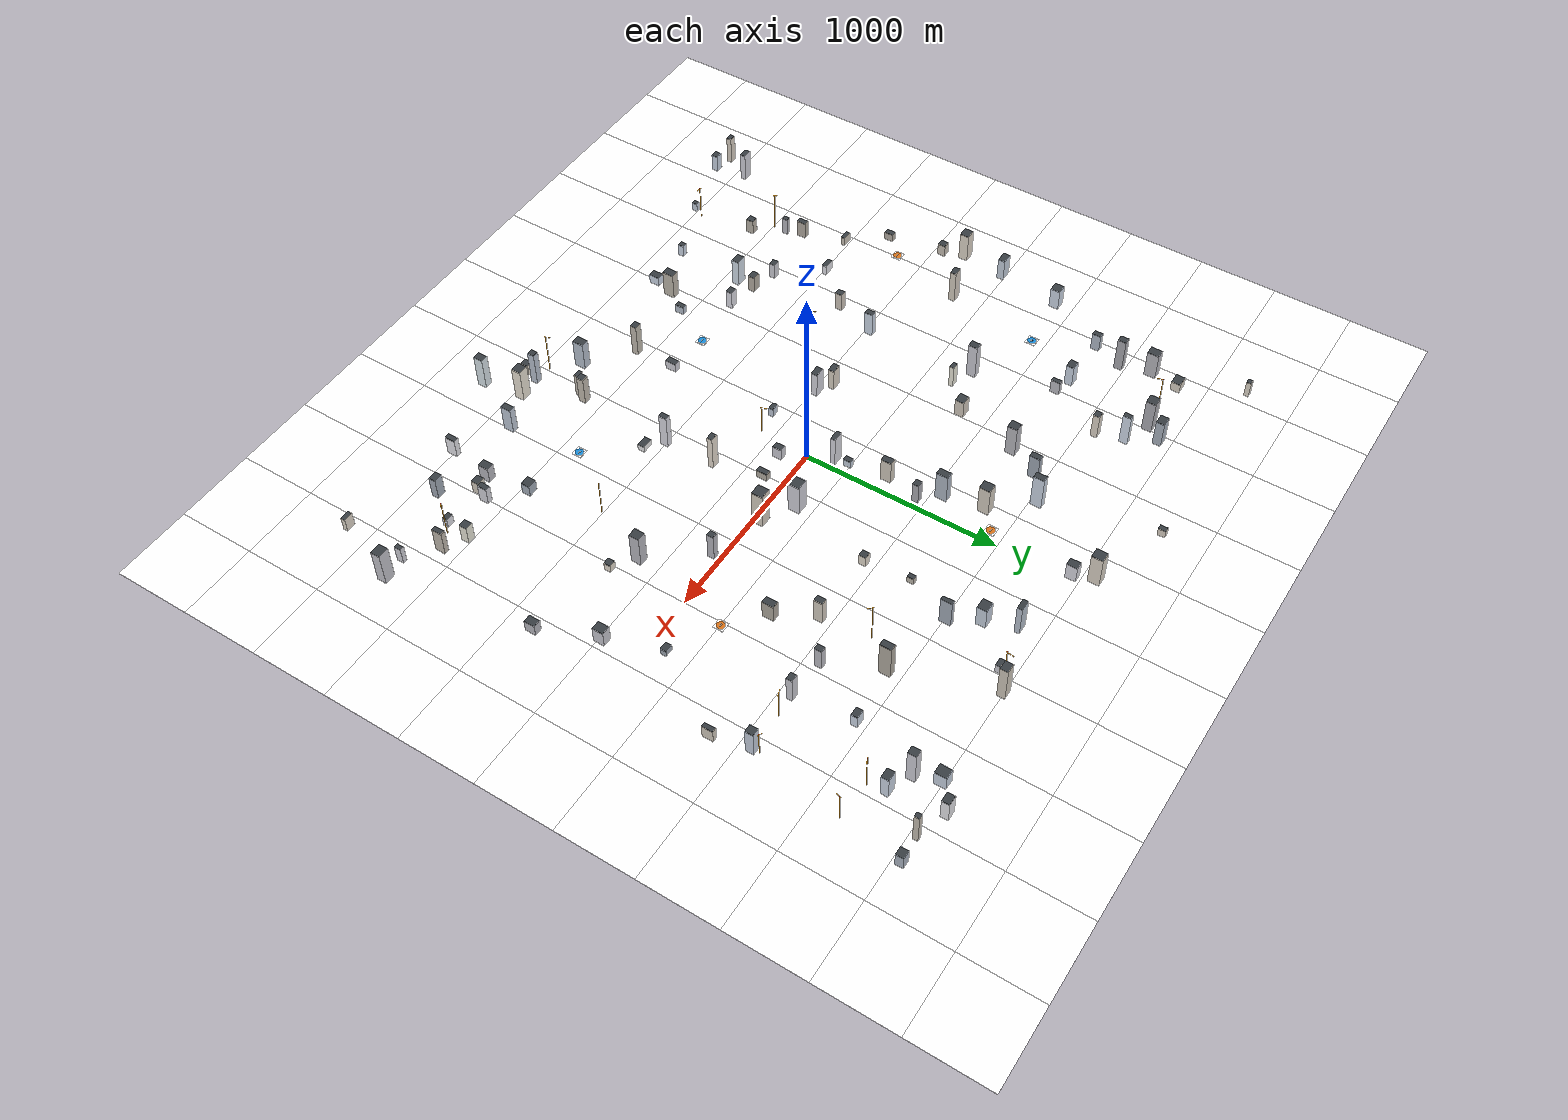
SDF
<?xml version='1.0'?>
<sdf version='1.9'>
<world name='urban'>
  <physics name='fast' type='ignored'>
    <max_step_size>0.005000</max_step_size>
    <real_time_factor>0</real_time_factor>
  </physics>
  <plugin filename='gz-sim-physics-system' name='gz::sim::systems::Physics'/>
  <plugin filename='gz-sim-user-commands-system'
          name='gz::sim::systems::UserCommands'/>
  <plugin filename='gz-sim-scene-broadcaster-system'
          name='gz::sim::systems::SceneBroadcaster'/>
  <plugin filename='gz-sim-sensors-system' name='gz::sim::systems::Sensors'>
    <render_engine>ogre2</render_engine>
  </plugin>
  <plugin filename='gz-sim-imu-system' name='gz::sim::systems::Imu'/>
  <plugin filename='PhyWamTraffic' name='phywam::PhyWamTraffic'>
    <seed>2</seed>
    <n_traffic>5</n_traffic>
    <n_suas>6</n_suas>
    <extent>1600.0</extent>
    <corridor_alt>120.0</corridor_alt>
    <namespace>phywam</namespace>
    <p_conflict>0.55</p_conflict>
    <buildings>1459.3,1433.0,12.1,12.6,172.0 755.1,543.1,16.9,22.5,133.2 259.9,-1093.2,19.2,18.5,152.9 1583.4,1438.1,21.3,19.5,75.6 -1485.0,-1512.2,19.8,17.1,94.6 1253.7,82.4,21.6,15.5,34.1 -559.5,-1162.6,20.7,30.0,144.7 -1018.1,1259.4,26.1,25.0,184.1 841.2,927.2,17.7,29.6,193.5 -1084.2,812.8,24.6,19.8,120.2 -32.0,1359.5,20.5,26.8,90.2 1225.1,1279.0,19.8,21.8,186.5 716.1,-42.9,15.2,17.2,148.9 1463.6,659.9,20.6,20.8,140.7 281.4,-602.1,14.9,20.7,188.8 394.4,-1358.8,26.6,24.8,184.3 -987.5,783.3,12.1,23.4,76.4 -874.8,1201.6,13.0,20.9,175.2 -816.5,-926.5,27.7,19.0,151.9 -1498.0,-440.5,14.3,23.8,44.1 1454.6,-1518.9,24.9,11.4,73.5 1002.7,-1097.2,14.5,24.1,95.5 -1461.9,1568.0,13.9,11.7,88.5 368.8,775.9,13.1,17.4,35.2 -164.3,851.1,25.1,28.1,158.5 1159.8,657.1,20.0,15.3,142.3 -587.8,-1273.4,19.5,27.6,51.7 271.9,-342.6,20.8,13.7,193.2 -770.9,339.4,19.0,11.3,124.9 -1150.2,-1418.3,11.6,14.1,46.3 432.2,26.4,29.7,28.7,199.1 -856.1,-177.0,15.8,22.2,136.1 960.7,670.4,15.9,19.0,119.5 -1584.6,-1486.4,18.8,13.1,153.0 -829.2,-1280.7,14.5,15.4,67.0 66.4,-113.9,16.9,23.2,66.1 1301.0,1482.0,24.8,19.2,117.0 259.4,-1436.0,18.9,21.0,60.8 -1299.9,968.5,18.0,20.9,186.6 353.6,-673.3,29.7,18.1,33.2 593.0,-1276.3,16.8,27.0,144.3 -1549.7,-155.4,18.8,20.2,65.4 284.0,-1363.9,16.4,18.1,189.0 -1355.0,815.9,14.7,21.9,96.6 -1342.4,1120.2,23.2,29.2,147.8 -1521.1,509.3,25.8,24.7,114.7 -455.7,-137.5,26.2,16.1,119.5 -71.8,1455.0,26.3,28.7,172.1 -650.4,-858.8,20.3,15.9,102.7 573.2,1339.5,22.1,26.5,46.3 -460.6,1592.8,13.8,18.9,41.4 -1324.3,1265.6,29.8,23.3,51.8 76.8,-1241.4,21.3,29.0,158.5 -1292.3,52.8,24.6,15.9,182.1 -125.0,650.3,18.7,29.9,163.1 235.0,-1136.8,19.4,11.6,131.2 1221.8,-1022.6,20.7,20.2,98.8 673.5,1397.3,24.4,20.0,193.5 -541.7,786.0,23.5,25.5,174.9 -880.0,388.0,18.7,23.7,196.1 431.5,-1562.9,19.8,24.5,180.1 480.3,1011.4,11.3,28.9,154.0 340.6,1297.0,27.8,12.9,168.7 854.4,-961.5,25.1,22.1,62.6 973.4,-1158.8,22.6,19.3,73.1 211.5,-105.3,14.9,29.4,42.4 -1590.3,-46.6,26.9,23.5,158.3 -48.0,559.4,17.4,16.1,115.5 -1511.9,-1344.6,25.3,14.3,157.5 910.0,-305.6,23.8,26.0,176.9 -1168.4,-1079.8,18.3,19.8,80.1 -1566.7,183.7,29.4,18.0,121.5 -376.5,-183.0,27.5,16.9,140.3 -51.9,123.4,28.4,12.5,170.1 -626.7,468.2,26.1,23.4,96.8 1090.3,-1302.6,23.0,18.4,120.2 1123.0,953.2,22.9,16.9,69.6 -135.9,-857.2,16.3,29.2,49.0 1019.6,-386.5,17.9,17.0,43.2 -136.4,-1067.2,19.4,16.5,182.1 1349.6,-185.6,23.2,28.7,85.5 -1281.4,-838.9,14.6,23.9,93.5 -460.5,944.3,15.4,26.4,137.6 -319.2,1035.3,17.5,27.7,187.4 1181.8,1393.8,25.3,29.6,79.6 392.0,546.1,18.0,18.5,59.7 1464.7,-467.2,20.1,28.0,61.7 1474.1,-1193.4,11.5,17.7,91.1 1336.5,1226.2,25.5,19.3,122.3 -842.3,1067.3,18.4,16.4,138.4 -1118.1,-587.7,28.6,12.8,54.2 -946.1,-796.9,19.0,15.8,88.3 -811.3,-831.7,22.6,17.4,93.4 857.0,-1402.6,13.7,27.2,103.1 892.2,-1175.1,20.9,27.1,87.5 858.2,353.2,18.5,29.9,96.7 -83.9,382.4,17.0,26.9,131.6 281.6,123.5,29.7,29.8,172.9 -145.4,-282.3,21.0,11.9,48.4 1584.8,-1189.7,28.8,23.9,185.6 -1352.5,-621.4,26.2,11.2,48.0 -477.9,-1046.0,13.8,23.7,45.6 1508.8,478.0,11.9,28.1,71.1 -59.3,188.1,13.6,20.5,40.3 -961.3,1339.4,26.6,20.9,145.9 1201.6,-1152.1,20.3,13.5,49.8 -1253.6,-922.3,12.0,15.1,94.5 392.6,1147.5,28.2,24.6,116.2 1334.4,-1078.4,13.0,26.5,136.6 -927.0,-392.6,16.7,19.2,102.7</buildings>
  </plugin>

  <gravity>0 0 -9.80665</gravity>
  <scene>
    <ambient>0.38 0.40 0.44 1</ambient>
    <background>0.46 0.60 0.78 1</background>
    <grid>false</grid><sky></sky>
  </scene>
  <light type='directional' name='sun'>
    <cast_shadows>true</cast_shadows>
    <pose>0 0 400 0 0 0</pose>
    <diffuse>0.88 0.86 0.80 1</diffuse><specular>0.18 0.18 0.18 1</specular>
    <direction>-0.42 0.38 -0.82</direction>
  </light>
  <model name='ground'><static>true</static>
    <link name='l'>
      <collision name='c'><geometry><plane><normal>0 0 1</normal>
      <size>9000 9000</size></plane></geometry></collision>
<visual name='g_0_0'><pose>-2000.0 -2000.0 -0.2 0 0 0</pose><geometry><box><size>400.0 400.0 0.4</size></box></geometry><material><ambient>0.5 0.5 0.5 1</ambient><diffuse>1.000 1.000 1.000 1</diffuse><specular>0.06 0.06 0.06 1</specular><pbr><metal><albedo_map>/home/glaze/Desktop/github_projects/Phy_WAM/sim/materials/textures/ground.png</albedo_map><metalness>0.0</metalness><roughness>0.95</roughness></metal></pbr></material></visual><visual name='g_1_0'><pose>-1600.0 -2000.0 -0.2 0 0 0</pose><geometry><box><size>400.0 400.0 0.4</size></box></geometry><material><ambient>0.5 0.5 0.5 1</ambient><diffuse>1.000 1.000 1.000 1</diffuse><specular>0.06 0.06 0.06 1</specular><pbr><metal><albedo_map>/home/glaze/Desktop/github_projects/Phy_WAM/sim/materials/textures/ground.png</albedo_map><metalness>0.0</metalness><roughness>0.95</roughness></metal></pbr></material></visual><visual name='g_2_0'><pose>-1200.0 -2000.0 -0.2 0 0 0</pose><geometry><box><size>400.0 400.0 0.4</size></box></geometry><material><ambient>0.5 0.5 0.5 1</ambient><diffuse>1.000 1.000 1.000 1</diffuse><specular>0.06 0.06 0.06 1</specular><pbr><metal><albedo_map>/home/glaze/Desktop/github_projects/Phy_WAM/sim/materials/textures/ground.png</albedo_map><metalness>0.0</metalness><roughness>0.95</roughness></metal></pbr></material></visual><visual name='g_3_0'><pose>-800.0 -2000.0 -0.2 0 0 0</pose><geometry><box><size>400.0 400.0 0.4</size></box></geometry><material><ambient>0.5 0.5 0.5 1</ambient><diffuse>1.000 1.000 1.000 1</diffuse><specular>0.06 0.06 0.06 1</specular><pbr><metal><albedo_map>/home/glaze/Desktop/github_projects/Phy_WAM/sim/materials/textures/ground.png</albedo_map><metalness>0.0</metalness><roughness>0.95</roughness></metal></pbr></material></visual><visual name='g_4_0'><pose>-400.0 -2000.0 -0.2 0 0 0</pose><geometry><box><size>400.0 400.0 0.4</size></box></geometry><material><ambient>0.5 0.5 0.5 1</ambient><diffuse>1.000 1.000 1.000 1</diffuse><specular>0.06 0.06 0.06 1</specular><pbr><metal><albedo_map>/home/glaze/Desktop/github_projects/Phy_WAM/sim/materials/textures/ground.png</albedo_map><metalness>0.0</metalness><roughness>0.95</roughness></metal></pbr></material></visual><visual name='g_5_0'><pose>0.0 -2000.0 -0.2 0 0 0</pose><geometry><box><size>400.0 400.0 0.4</size></box></geometry><material><ambient>0.5 0.5 0.5 1</ambient><diffuse>1.000 1.000 1.000 1</diffuse><specular>0.06 0.06 0.06 1</specular><pbr><metal><albedo_map>/home/glaze/Desktop/github_projects/Phy_WAM/sim/materials/textures/ground.png</albedo_map><metalness>0.0</metalness><roughness>0.95</roughness></metal></pbr></material></visual><visual name='g_6_0'><pose>400.0 -2000.0 -0.2 0 0 0</pose><geometry><box><size>400.0 400.0 0.4</size></box></geometry><material><ambient>0.5 0.5 0.5 1</ambient><diffuse>1.000 1.000 1.000 1</diffuse><specular>0.06 0.06 0.06 1</specular><pbr><metal><albedo_map>/home/glaze/Desktop/github_projects/Phy_WAM/sim/materials/textures/ground.png</albedo_map><metalness>0.0</metalness><roughness>0.95</roughness></metal></pbr></material></visual><visual name='g_7_0'><pose>800.0 -2000.0 -0.2 0 0 0</pose><geometry><box><size>400.0 400.0 0.4</size></box></geometry><material><ambient>0.5 0.5 0.5 1</ambient><diffuse>1.000 1.000 1.000 1</diffuse><specular>0.06 0.06 0.06 1</specular><pbr><metal><albedo_map>/home/glaze/Desktop/github_projects/Phy_WAM/sim/materials/textures/ground.png</albedo_map><metalness>0.0</metalness><roughness>0.95</roughness></metal></pbr></material></visual><visual name='g_8_0'><pose>1200.0 -2000.0 -0.2 0 0 0</pose><geometry><box><size>400.0 400.0 0.4</size></box></geometry><material><ambient>0.5 0.5 0.5 1</ambient><diffuse>1.000 1.000 1.000 1</diffuse><specular>0.06 0.06 0.06 1</specular><pbr><metal><albedo_map>/home/glaze/Desktop/github_projects/Phy_WAM/sim/materials/textures/ground.png</albedo_map><metalness>0.0</metalness><roughness>0.95</roughness></metal></pbr></material></visual><visual name='g_9_0'><pose>1600.0 -2000.0 -0.2 0 0 0</pose><geometry><box><size>400.0 400.0 0.4</size></box></geometry><material><ambient>0.5 0.5 0.5 1</ambient><diffuse>1.000 1.000 1.000 1</diffuse><specular>0.06 0.06 0.06 1</specular><pbr><metal><albedo_map>/home/glaze/Desktop/github_projects/Phy_WAM/sim/materials/textures/ground.png</albedo_map><metalness>0.0</metalness><roughness>0.95</roughness></metal></pbr></material></visual><visual name='g_10_0'><pose>2000.0 -2000.0 -0.2 0 0 0</pose><geometry><box><size>400.0 400.0 0.4</size></box></geometry><material><ambient>0.5 0.5 0.5 1</ambient><diffuse>1.000 1.000 1.000 1</diffuse><specular>0.06 0.06 0.06 1</specular><pbr><metal><albedo_map>/home/glaze/Desktop/github_projects/Phy_WAM/sim/materials/textures/ground.png</albedo_map><metalness>0.0</metalness><roughness>0.95</roughness></metal></pbr></material></visual><visual name='g_0_1'><pose>-2000.0 -1600.0 -0.2 0 0 0</pose><geometry><box><size>400.0 400.0 0.4</size></box></geometry><material><ambient>0.5 0.5 0.5 1</ambient><diffuse>1.000 1.000 1.000 1</diffuse><specular>0.06 0.06 0.06 1</specular><pbr><metal><albedo_map>/home/glaze/Desktop/github_projects/Phy_WAM/sim/materials/textures/ground.png</albedo_map><metalness>0.0</metalness><roughness>0.95</roughness></metal></pbr></material></visual><visual name='g_1_1'><pose>-1600.0 -1600.0 -0.2 0 0 0</pose><geometry><box><size>400.0 400.0 0.4</size></box></geometry><material><ambient>0.5 0.5 0.5 1</ambient><diffuse>1.000 1.000 1.000 1</diffuse><specular>0.06 0.06 0.06 1</specular><pbr><metal><albedo_map>/home/glaze/Desktop/github_projects/Phy_WAM/sim/materials/textures/ground.png</albedo_map><metalness>0.0</metalness><roughness>0.95</roughness></metal></pbr></material></visual><visual name='g_2_1'><pose>-1200.0 -1600.0 -0.2 0 0 0</pose><geometry><box><size>400.0 400.0 0.4</size></box></geometry><material><ambient>0.5 0.5 0.5 1</ambient><diffuse>1.000 1.000 1.000 1</diffuse><specular>0.06 0.06 0.06 1</specular><pbr><metal><albedo_map>/home/glaze/Desktop/github_projects/Phy_WAM/sim/materials/textures/ground.png</albedo_map><metalness>0.0</metalness><roughness>0.95</roughness></metal></pbr></material></visual><visual name='g_3_1'><pose>-800.0 -1600.0 -0.2 0 0 0</pose><geometry><box><size>400.0 400.0 0.4</size></box></geometry><material><ambient>0.5 0.5 0.5 1</ambient><diffuse>1.000 1.000 1.000 1</diffuse><specular>0.06 0.06 0.06 1</specular><pbr><metal><albedo_map>/home/glaze/Desktop/github_projects/Phy_WAM/sim/materials/textures/ground.png</albedo_map><metalness>0.0</metalness><roughness>0.95</roughness></metal></pbr></material></visual><visual name='g_4_1'><pose>-400.0 -1600.0 -0.2 0 0 0</pose><geometry><box><size>400.0 400.0 0.4</size></box></geometry><material><ambient>0.5 0.5 0.5 1</ambient><diffuse>1.000 1.000 1.000 1</diffuse><specular>0.06 0.06 0.06 1</specular><pbr><metal><albedo_map>/home/glaze/Desktop/github_projects/Phy_WAM/sim/materials/textures/ground.png</albedo_map><metalness>0.0</metalness><roughness>0.95</roughness></metal></pbr></material></visual><visual name='g_5_1'><pose>0.0 -1600.0 -0.2 0 0 0</pose><geometry><box><size>400.0 400.0 0.4</size></box></geometry><material><ambient>0.5 0.5 0.5 1</ambient><diffuse>1.000 1.000 1.000 1</diffuse><specular>0.06 0.06 0.06 1</specular><pbr><metal><albedo_map>/home/glaze/Desktop/github_projects/Phy_WAM/sim/materials/textures/ground.png</albedo_map><metalness>0.0</metalness><roughness>0.95</roughness></metal></pbr></material></visual><visual name='g_6_1'><pose>400.0 -1600.0 -0.2 0 0 0</pose><geometry><box><size>400.0 400.0 0.4</size></box></geometry><material><ambient>0.5 0.5 0.5 1</ambient><diffuse>1.000 1.000 1.000 1</diffuse><specular>0.06 0.06 0.06 1</specular><pbr><metal><albedo_map>/home/glaze/Desktop/github_projects/Phy_WAM/sim/materials/textures/ground.png</albedo_map><metalness>0.0</metalness><roughness>0.95</roughness></metal></pbr></material></visual><visual name='g_7_1'><pose>800.0 -1600.0 -0.2 0 0 0</pose><geometry><box><size>400.0 400.0 0.4</size></box></geometry><material><ambient>0.5 0.5 0.5 1</ambient><diffuse>1.000 1.000 1.000 1</diffuse><specular>0.06 0.06 0.06 1</specular><pbr><metal><albedo_map>/home/glaze/Desktop/github_projects/Phy_WAM/sim/materials/textures/ground.png</albedo_map><metalness>0.0</metalness><roughness>0.95</roughness></metal></pbr></material></visual><visual name='g_8_1'><pose>1200.0 -1600.0 -0.2 0 0 0</pose><geometry><box><size>400.0 400.0 0.4</size></box></geometry><material><ambient>0.5 0.5 0.5 1</ambient><diffuse>1.000 1.000 1.000 1</diffuse><specular>0.06 0.06 0.06 1</specular><pbr><metal><albedo_map>/home/glaze/Desktop/github_projects/Phy_WAM/sim/materials/textures/ground.png</albedo_map><metalness>0.0</metalness><roughness>0.95</roughness></metal></pbr></material></visual><visual name='g_9_1'><pose>1600.0 -1600.0 -0.2 0 0 0</pose><geometry><box><size>400.0 400.0 0.4</size></box></geometry><material><ambient>0.5 0.5 0.5 1</ambient><diffuse>1.000 1.000 1.000 1</diffuse><specular>0.06 0.06 0.06 1</specular><pbr><metal><albedo_map>/home/glaze/Desktop/github_projects/Phy_WAM/sim/materials/textures/ground.png</albedo_map><metalness>0.0</metalness><roughness>0.95</roughness></metal></pbr></material></visual><visual name='g_10_1'><pose>2000.0 -1600.0 -0.2 0 0 0</pose><geometry><box><size>400.0 400.0 0.4</size></box></geometry><material><ambient>0.5 0.5 0.5 1</ambient><diffuse>1.000 1.000 1.000 1</diffuse><specular>0.06 0.06 0.06 1</specular><pbr><metal><albedo_map>/home/glaze/Desktop/github_projects/Phy_WAM/sim/materials/textures/ground.png</albedo_map><metalness>0.0</metalness><roughness>0.95</roughness></metal></pbr></material></visual><visual name='g_0_2'><pose>-2000.0 -1200.0 -0.2 0 0 0</pose><geometry><box><size>400.0 400.0 0.4</size></box></geometry><material><ambient>0.5 0.5 0.5 1</ambient><diffuse>1.000 1.000 1.000 1</diffuse><specular>0.06 0.06 0.06 1</specular><pbr><metal><albedo_map>/home/glaze/Desktop/github_projects/Phy_WAM/sim/materials/textures/ground.png</albedo_map><metalness>0.0</metalness><roughness>0.95</roughness></metal></pbr></material></visual><visual name='g_1_2'><pose>-1600.0 -1200.0 -0.2 0 0 0</pose><geometry><box><size>400.0 400.0 0.4</size></box></geometry><material><ambient>0.5 0.5 0.5 1</ambient><diffuse>1.000 1.000 1.000 1</diffuse><specular>0.06 0.06 0.06 1</specular><pbr><metal><albedo_map>/home/glaze/Desktop/github_projects/Phy_WAM/sim/materials/textures/ground.png</albedo_map><metalness>0.0</metalness><roughness>0.95</roughness></metal></pbr></material></visual><visual name='g_2_2'><pose>-1200.0 -1200.0 -0.2 0 0 0</pose><geometry><box><size>400.0 400.0 0.4</size></box></geometry><material><ambient>0.5 0.5 0.5 1</ambient><diffuse>1.000 1.000 1.000 1</diffuse><specular>0.06 0.06 0.06 1</specular><pbr><metal><albedo_map>/home/glaze/Desktop/github_projects/Phy_WAM/sim/materials/textures/ground.png</albedo_map><metalness>0.0</metalness><roughness>0.95</roughness></metal></pbr></material></visual><visual name='g_3_2'><pose>-800.0 -1200.0 -0.2 0 0 0</pose><geometry><box><size>400.0 400.0 0.4</size></box></geometry><material><ambient>0.5 0.5 0.5 1</ambient><diffuse>1.000 1.000 1.000 1</diffuse><specular>0.06 0.06 0.06 1</specular><pbr><metal><albedo_map>/home/glaze/Desktop/github_projects/Phy_WAM/sim/materials/textures/ground.png</albedo_map><metalness>0.0</metalness><roughness>0.95</roughness></metal></pbr></material></visual><visual name='g_4_2'><pose>-400.0 -1200.0 -0.2 0 0 0</pose><geometry><box><size>400.0 400.0 0.4</size></box></geometry><material><ambient>0.5 0.5 0.5 1</ambient><diffuse>1.000 1.000 1.000 1</diffuse><specular>0.06 0.06 0.06 1</specular><pbr><metal><albedo_map>/home/glaze/Desktop/github_projects/Phy_WAM/sim/materials/textures/ground.png</albedo_map><metalness>0.0</metalness><roughness>0.95</roughness></metal></pbr></material></visual><visual name='g_5_2'><pose>0.0 -1200.0 -0.2 0 0 0</pose><geometry><box><size>400.0 400.0 0.4</size></box></geometry><material><ambient>0.5 0.5 0.5 1</ambient><diffuse>1.000 1.000 1.000 1</diffuse><specular>0.06 0.06 0.06 1</specular><pbr><metal><albedo_map>/home/glaze/Desktop/github_projects/Phy_WAM/sim/materials/textures/ground.png</albedo_map><metalness>0.0</metalness><roughness>0.95</roughness></metal></pbr></material></visual><visual name='g_6_2'><pose>400.0 -1200.0 -0.2 0 0 0</pose><geometry><box><size>400.0 400.0 0.4</size></box></geometry><material><ambient>0.5 0.5 0.5 1</ambient><diffuse>1.000 1.000 1.000 1</diffuse><specular>0.06 0.06 0.06 1</specular><pbr><metal><albedo_map>/home/glaze/Desktop/github_projects/Phy_WAM/sim/materials/textures/ground.png</albedo_map><metalness>0.0</metalness><roughness>0.95</roughness></metal></pbr></material></visual><visual name='g_7_2'><pose>800.0 -1200.0 -0.2 0 0 0</pose><geometry><box><size>400.0 400.0 0.4</size></box></geometry><material><ambient>0.5 0.5 0.5 1</ambient><diffuse>1.000 1.000 1.000 1</diffuse><specular>0.06 0.06 0.06 1</specular><pbr><metal><albedo_map>/home/glaze/Desktop/github_projects/Phy_WAM/sim/materials/textures/ground.png</albedo_map><metalness>0.0</metalness><roughness>0.95</roughness></metal></pbr></material></visual><visual name='g_8_2'><pose>1200.0 -1200.0 -0.2 0 0 0</pose><geometry><box><size>400.0 400.0 0.4</size></box></geometry><material><ambient>0.5 0.5 0.5 1</ambient><diffuse>1.000 1.000 1.000 1</diffuse><specular>0.06 0.06 0.06 1</specular><pbr><metal><albedo_map>/home/glaze/Desktop/github_projects/Phy_WAM/sim/materials/textures/ground.png</albedo_map><metalness>0.0</metalness><roughness>0.95</roughness></metal></pbr></material></visual><visual name='g_9_2'><pose>1600.0 -1200.0 -0.2 0 0 0</pose><geometry><box><size>400.0 400.0 0.4</size></box></geometry><material><ambient>0.5 0.5 0.5 1</ambient><diffuse>1.000 1.000 1.000 1</diffuse><specular>0.06 0.06 0.06 1</specular><pbr><metal><albedo_map>/home/glaze/Desktop/github_projects/Phy_WAM/sim/materials/textures/ground.png</albedo_map><metalness>0.0</metalness><roughness>0.95</roughness></metal></pbr></material></visual><visual name='g_10_2'><pose>2000.0 -1200.0 -0.2 0 0 0</pose><geometry><box><size>400.0 400.0 0.4</size></box></geometry><material><ambient>0.5 0.5 0.5 1</ambient><diffuse>1.000 1.000 1.000 1</diffuse><specular>0.06 0.06 0.06 1</specular><pbr><metal><albedo_map>/home/glaze/Desktop/github_projects/Phy_WAM/sim/materials/textures/ground.png</albedo_map><metalness>0.0</metalness><roughness>0.95</roughness></metal></pbr></material></visual><visual name='g_0_3'><pose>-2000.0 -800.0 -0.2 0 0 0</pose><geometry><box><size>400.0 400.0 0.4</size></box></geometry><material><ambient>0.5 0.5 0.5 1</ambient><diffuse>1.000 1.000 1.000 1</diffuse><specular>0.06 0.06 0.06 1</specular><pbr><metal><albedo_map>/home/glaze/Desktop/github_projects/Phy_WAM/sim/materials/textures/ground.png</albedo_map><metalness>0.0</metalness><roughness>0.95</roughness></metal></pbr></material></visual><visual name='g_1_3'><pose>-1600.0 -800.0 -0.2 0 0 0</pose><geometry><box><size>400.0 400.0 0.4</size></box></geometry><material><ambient>0.5 0.5 0.5 1</ambient><diffuse>1.000 1.000 1.000 1</diffuse><specular>0.06 0.06 0.06 1</specular><pbr><metal><albedo_map>/home/glaze/Desktop/github_projects/Phy_WAM/sim/materials/textures/ground.png</albedo_map><metalness>0.0</metalness><roughness>0.95</roughness></metal></pbr></material></visual><visual name='g_2_3'><pose>-1200.0 -800.0 -0.2 0 0 0</pose><geometry><box><size>400.0 400.0 0.4</size></box></geometry><material><ambient>0.5 0.5 0.5 1</ambient><diffuse>1.000 1.000 1.000 1</diffuse><specular>0.06 0.06 0.06 1</specular><pbr><metal><albedo_map>/home/glaze/Desktop/github_projects/Phy_WAM/sim/materials/textures/ground.png</albedo_map><metalness>0.0</metalness><roughness>0.95</roughness></metal></pbr></material></visual><visual name='g_3_3'><pose>-800.0 -800.0 -0.2 0 0 0</pose><geometry><box><size>400.0 400.0 0.4</size></box></geometry><material><ambient>0.5 0.5 0.5 1</ambient><diffuse>1.000 1.000 1.000 1</diffuse><specular>0.06 0.06 0.06 1</specular><pbr><metal><albedo_map>/home/glaze/Desktop/github_projects/Phy_WAM/sim/materials/textures/ground.png</albedo_map><metalness>0.0</metalness><roughness>0.95</roughness></metal></pbr></material></visual><visual name='g_4_3'><pose>-400.0 -800.0 -0.2 0 0 0</pose><geometry><box><size>400.0 400.0 0.4</size></box></geometry><material><ambient>0.5 0.5 0.5 1</ambient><diffuse>1.000 1.000 1.000 1</diffuse><specular>0.06 0.06 0.06 1</specular><pbr><metal><albedo_map>/home/glaze/Desktop/github_projects/Phy_WAM/sim/materials/textures/ground.png</albedo_map><metalness>0.0</metalness><roughness>0.95</roughness></metal></pbr></material></visual><visual name='g_5_3'><pose>0.0 -800.0 -0.2 0 0 0</pose><geometry><box><size>400.0 400.0 0.4</size></box></geometry><material><ambient>0.5 0.5 0.5 1</ambient><diffuse>1.000 1.000 1.000 1</diffuse><specular>0.06 0.06 0.06 1</specular><pbr><metal><albedo_map>/home/glaze/Desktop/github_projects/Phy_WAM/sim/materials/textures/ground.png</albedo_map><metalness>0.0</metalness><roughness>0.95</roughness></metal></pbr></material></visual><visual name='g_6_3'><pose>400.0 -800.0 -0.2 0 0 0</pose><geometry><box><size>400.0 400.0 0.4</size></box></geometry><material><ambient>0.5 0.5 0.5 1</ambient><diffuse>1.000 1.000 1.000 1</diffuse><specular>0.06 0.06 0.06 1</specular><pbr><metal><albedo_map>/home/glaze/Desktop/github_projects/Phy_WAM/sim/materials/textures/ground.png</albedo_map><metalness>0.0</metalness><roughness>0.95</roughness></metal></pbr></material></visual><visual name='g_7_3'><pose>800.0 -800.0 -0.2 0 0 0</pose><geometry><box><size>400.0 400.0 0.4</size></box></geometry><material><ambient>0.5 0.5 0.5 1</ambient><diffuse>1.000 1.000 1.000 1</diffuse><specular>0.06 0.06 0.06 1</specular><pbr><metal><albedo_map>/home/glaze/Desktop/github_projects/Phy_WAM/sim/materials/textures/ground.png</albedo_map><metalness>0.0</metalness><roughness>0.95</roughness></metal></pbr></material></visual><visual name='g_8_3'><pose>1200.0 -800.0 -0.2 0 0 0</pose><geometry><box><size>400.0 400.0 0.4</size></box></geometry><material><ambient>0.5 0.5 0.5 1</ambient><diffuse>1.000 1.000 1.000 1</diffuse><specular>0.06 0.06 0.06 1</specular><pbr><metal><albedo_map>/home/glaze/Desktop/github_projects/Phy_WAM/sim/materials/textures/ground.png</albedo_map><metalness>0.0</metalness><roughness>0.95</roughness></metal></pbr></material></visual><visual name='g_9_3'><pose>1600.0 -800.0 -0.2 0 0 0</pose><geometry><box><size>400.0 400.0 0.4</size></box></geometry><material><ambient>0.5 0.5 0.5 1</ambient><diffuse>1.000 1.000 1.000 1</diffuse><specular>0.06 0.06 0.06 1</specular><pbr><metal><albedo_map>/home/glaze/Desktop/github_projects/Phy_WAM/sim/materials/textures/ground.png</albedo_map><metalness>0.0</metalness><roughness>0.95</roughness></metal></pbr></material></visual><visual name='g_10_3'><pose>2000.0 -800.0 -0.2 0 0 0</pose><geometry><box><size>400.0 400.0 0.4</size></box></geometry><material><ambient>0.5 0.5 0.5 1</ambient><diffuse>1.000 1.000 1.000 1</diffuse><specular>0.06 0.06 0.06 1</specular><pbr><metal><albedo_map>/home/glaze/Desktop/github_projects/Phy_WAM/sim/materials/textures/ground.png</albedo_map><metalness>0.0</metalness><roughness>0.95</roughness></metal></pbr></material></visual><visual name='g_0_4'><pose>-2000.0 -400.0 -0.2 0 0 0</pose><geometry><box><size>400.0 400.0 0.4</size></box></geometry><material><ambient>0.5 0.5 0.5 1</ambient><diffuse>1.000 1.000 1.000 1</diffuse><specular>0.06 0.06 0.06 1</specular><pbr><metal><albedo_map>/home/glaze/Desktop/github_projects/Phy_WAM/sim/materials/textures/ground.png</albedo_map><metalness>0.0</metalness><roughness>0.95</roughness></metal></pbr></material></visual><visual name='g_1_4'><pose>-1600.0 -400.0 -0.2 0 0 0</pose><geometry><box><size>400.0 400.0 0.4</size></box></geometry><material><ambient>0.5 0.5 0.5 1</ambient><diffuse>1.000 1.000 1.000 1</diffuse><specular>0.06 0.06 0.06 1</specular><pbr><metal><albedo_map>/home/glaze/Desktop/github_projects/Phy_WAM/sim/materials/textures/ground.png</albedo_map><metalness>0.0</metalness><roughness>0.95</roughness></metal></pbr></material></visual><visual name='g_2_4'><pose>-1200.0 -400.0 -0.2 0 0 0</pose><geometry><box><size>400.0 400.0 0.4</size></box></geometry><material><ambient>0.5 0.5 0.5 1</ambient><diffuse>1.000 1.000 1.000 1</diffuse><specular>0.06 0.06 0.06 1</specular><pbr><metal><albedo_map>/home/glaze/Desktop/github_projects/Phy_WAM/sim/materials/textures/ground.png</albedo_map><metalness>0.0</metalness><roughness>0.95</roughness></metal></pbr></material></visual><visual name='g_3_4'><pose>-800.0 -400.0 -0.2 0 0 0</pose><geometry><box><size>400.0 400.0 0.4</size></box></geometry><material><ambient>0.5 0.5 0.5 1</ambient><diffuse>1.000 1.000 1.000 1</diffuse><specular>0.06 0.06 0.06 1</specular><pbr><metal><albedo_map>/home/glaze/Desktop/github_projects/Phy_WAM/sim/materials/textures/ground.png</albedo_map><metalness>0.0</metalness><roughness>0.95</roughness></metal></pbr></material></visual><visual name='g_4_4'><pose>-400.0 -400.0 -0.2 0 0 0</pose><geometry><box><size>400.0 400.0 0.4</size></box></geometry><material><ambient>0.5 0.5 0.5 1</ambient><diffuse>1.000 1.000 1.000 1</diffuse><specular>0.06 0.06 0.06 1</specular><pbr><metal><albedo_map>/home/glaze/Desktop/github_projects/Phy_WAM/sim/materials/textures/ground.png</albedo_map><metalness>0.0</metalness><roughness>0.95</roughness></metal></pbr></material></visual><visual name='g_5_4'><pose>0.0 -400.0 -0.2 0 0 0</pose><geometry><box><size>400.0 400.0 0.4</size></box></geometry><material><ambient>0.5 0.5 0.5 1</ambient><diffuse>1.000 1.000 1.000 1</diffuse><specular>0.06 0.06 0.06 1</specular><pbr><metal><albedo_map>/home/glaze/Desktop/github_projects/Phy_WAM/sim/materials/textures/ground.png</albedo_map><metalness>0.0</metalness><roughness>0.95</roughness></metal></pbr></material></visual><visual name='g_6_4'><pose>400.0 -400.0 -0.2 0 0 0</pose><geometry><box><size>400.0 400.0 0.4</size></box></geometry><material><ambient>0.5 0.5 0.5 1</ambient><diffuse>1.000 1.000 1.000 1</diffuse><specular>0.06 0.06 0.06 1</specular><pbr><metal><albedo_map>/home/glaze/Desktop/github_projects/Phy_WAM/sim/materials/textures/ground.png</albedo_map><metalness>0.0</metalness><roughness>0.95</roughness></metal></pbr></material></visual><visual name='g_7_4'><pose>800.0 -400.0 -0.2 0 0 0</pose><geometry><box><size>400.0 400.0 0.4</size></box></geometry><material><ambient>0.5 0.5 0.5 1</ambient><diffuse>1.000 1.000 1.000 1</diffuse><specular>0.06 0.06 0.06 1</specular><pbr><metal><albedo_map>/home/glaze/Desktop/github_projects/Phy_WAM/sim/materials/textures/ground.png</albedo_map><metalness>0.0</metalness><roughness>0.95</roughness></metal></pbr></material></visual><visual name='g_8_4'><pose>1200.0 -400.0 -0.2 0 0 0</pose><geometry><box><size>400.0 400.0 0.4</size></box></geometry><material><ambient>0.5 0.5 0.5 1</ambient><diffuse>1.000 1.000 1.000 1</diffuse><specular>0.06 0.06 0.06 1</specular><pbr><metal><albedo_map>/home/glaze/Desktop/github_projects/Phy_WAM/sim/materials/textures/ground.png</albedo_map><metalness>0.0</metalness><roughness>0.95</roughness></metal></pbr></material></visual><visual name='g_9_4'><pose>1600.0 -400.0 -0.2 0 0 0</pose><geometry><box><size>400.0 400.0 0.4</size></box></geometry><material><ambient>0.5 0.5 0.5 1</ambient><diffuse>1.000 1.000 1.000 1</diffuse><specular>0.06 0.06 0.06 1</specular><pbr><metal><albedo_map>/home/glaze/Desktop/github_projects/Phy_WAM/sim/materials/textures/ground.png</albedo_map><metalness>0.0</metalness><roughness>0.95</roughness></metal></pbr></material></visual><visual name='g_10_4'><pose>2000.0 -400.0 -0.2 0 0 0</pose><geometry><box><size>400.0 400.0 0.4</size></box></geometry><material><ambient>0.5 0.5 0.5 1</ambient><diffuse>1.000 1.000 1.000 1</diffuse><specular>0.06 0.06 0.06 1</specular><pbr><metal><albedo_map>/home/glaze/Desktop/github_projects/Phy_WAM/sim/materials/textures/ground.png</albedo_map><metalness>0.0</metalness><roughness>0.95</roughness></metal></pbr></material></visual><visual name='g_0_5'><pose>-2000.0 0.0 -0.2 0 0 0</pose><geometry><box><size>400.0 400.0 0.4</size></box></geometry><material><ambient>0.5 0.5 0.5 1</ambient><diffuse>1.000 1.000 1.000 1</diffuse><specular>0.06 0.06 0.06 1</specular><pbr><metal><albedo_map>/home/glaze/Desktop/github_projects/Phy_WAM/sim/materials/textures/ground.png</albedo_map><metalness>0.0</metalness><roughness>0.95</roughness></metal></pbr></material></visual><visual name='g_1_5'><pose>-1600.0 0.0 -0.2 0 0 0</pose><geometry><box><size>400.0 400.0 0.4</size></box></geometry><material><ambient>0.5 0.5 0.5 1</ambient><diffuse>1.000 1.000 1.000 1</diffuse><specular>0.06 0.06 0.06 1</specular><pbr><metal><albedo_map>/home/glaze/Desktop/github_projects/Phy_WAM/sim/materials/textures/ground.png</albedo_map><metalness>0.0</metalness><roughness>0.95</roughness></metal></pbr></material></visual><visual name='g_2_5'><pose>-1200.0 0.0 -0.2 0 0 0</pose><geometry><box><size>400.0 400.0 0.4</size></box></geometry><material><ambient>0.5 0.5 0.5 1</ambient><diffuse>1.000 1.000 1.000 1</diffuse><specular>0.06 0.06 0.06 1</specular><pbr><metal><albedo_map>/home/glaze/Desktop/github_projects/Phy_WAM/sim/materials/textures/ground.png</albedo_map><metalness>0.0</metalness><roughness>0.95</roughness></metal></pbr></material></visual><visual name='g_3_5'><pose>-800.0 0.0 -0.2 0 0 0</pose><geometry><box><size>400.0 400.0 0.4</size></box></geometry><material><ambient>0.5 0.5 0.5 1</ambient><diffuse>1.000 1.000 1.000 1</diffuse><specular>0.06 0.06 0.06 1</specular><pbr><metal><albedo_map>/home/glaze/Desktop/github_projects/Phy_WAM/sim/materials/textures/ground.png</albedo_map><metalness>0.0</metalness><roughness>0.95</roughness></metal></pbr></material></visual><visual name='g_4_5'><pose>-400.0 0.0 -0.2 0 0 0</pose><geometry><box><size>400.0 400.0 0.4</size></box></geometry><material><ambient>0.5 0.5 0.5 1</ambient><diffuse>1.000 1.000 1.000 1</diffuse><specular>0.06 0.06 0.06 1</specular><pbr><metal><albedo_map>/home/glaze/Desktop/github_projects/Phy_WAM/sim/materials/textures/ground.png</albedo_map><metalness>0.0</metalness><roughness>0.95</roughness></metal></pbr></material></visual><visual name='g_5_5'><pose>0.0 0.0 -0.2 0 0 0</pose><geometry><box><size>400.0 400.0 0.4</size></box></geometry><material><ambient>0.5 0.5 0.5 1</ambient><diffuse>1.000 1.000 1.000 1</diffuse><specular>0.06 0.06 0.06 1</specular><pbr><metal><albedo_map>/home/glaze/Desktop/github_projects/Phy_WAM/sim/materials/textures/ground.png</albedo_map><metalness>0.0</metalness><roughness>0.95</roughness></metal></pbr></material></visual><visual name='g_6_5'><pose>400.0 0.0 -0.2 0 0 0</pose><geometry><box><size>400.0 400.0 0.4</size></box></geometry><material><ambient>0.5 0.5 0.5 1</ambient><diffuse>1.000 1.000 1.000 1</diffuse><specular>0.06 0.06 0.06 1</specular><pbr><metal><albedo_map>/home/glaze/Desktop/github_projects/Phy_WAM/sim/materials/textures/ground.png</albedo_map><metalness>0.0</metalness><roughness>0.95</roughness></metal></pbr></material></visual><visual name='g_7_5'><pose>800.0 0.0 -0.2 0 0 0</pose><geometry><box><size>400.0 400.0 0.4</size></box></geometry><material><ambient>0.5 0.5 0.5 1</ambient><diffuse>1.000 1.000 1.000 1</diffuse><specular>0.06 0.06 0.06 1</specular><pbr><metal><albedo_map>/home/glaze/Desktop/github_projects/Phy_WAM/sim/materials/textures/ground.png</albedo_map><metalness>0.0</metalness><roughness>0.95</roughness></metal></pbr></material></visual><visual name='g_8_5'><pose>1200.0 0.0 -0.2 0 0 0</pose><geometry><box><size>400.0 400.0 0.4</size></box></geometry><material><ambient>0.5 0.5 0.5 1</ambient><diffuse>1.000 1.000 1.000 1</diffuse><specular>0.06 0.06 0.06 1</specular><pbr><metal><albedo_map>/home/glaze/Desktop/github_projects/Phy_WAM/sim/materials/textures/ground.png</albedo_map><metalness>0.0</metalness><roughness>0.95</roughness></metal></pbr></material></visual><visual name='g_9_5'><pose>1600.0 0.0 -0.2 0 0 0</pose><geometry><box><size>400.0 400.0 0.4</size></box></geometry><material><ambient>0.5 0.5 0.5 1</ambient><diffuse>1.000 1.000 1.000 1</diffuse><specular>0.06 0.06 0.06 1</specular><pbr><metal><albedo_map>/home/glaze/Desktop/github_projects/Phy_WAM/sim/materials/textures/ground.png</albedo_map><metalness>0.0</metalness><roughness>0.95</roughness></metal></pbr></material></visual><visual name='g_10_5'><pose>2000.0 0.0 -0.2 0 0 0</pose><geometry><box><size>400.0 400.0 0.4</size></box></geometry><material><ambient>0.5 0.5 0.5 1</ambient><diffuse>1.000 1.000 1.000 1</diffuse><specular>0.06 0.06 0.06 1</specular><pbr><metal><albedo_map>/home/glaze/Desktop/github_projects/Phy_WAM/sim/materials/textures/ground.png</albedo_map><metalness>0.0</metalness><roughness>0.95</roughness></metal></pbr></material></visual><visual name='g_0_6'><pose>-2000.0 400.0 -0.2 0 0 0</pose><geometry><box><size>400.0 400.0 0.4</size></box></geometry><material><ambient>0.5 0.5 0.5 1</ambient><diffuse>1.000 1.000 1.000 1</diffuse><specular>0.06 0.06 0.06 1</specular><pbr><metal><albedo_map>/home/glaze/Desktop/github_projects/Phy_WAM/sim/materials/textures/ground.png</albedo_map><metalness>0.0</metalness><roughness>0.95</roughness></metal></pbr></material></visual><visual name='g_1_6'><pose>-1600.0 400.0 -0.2 0 0 0</pose><geometry><box><size>400.0 400.0 0.4</size></box></geometry><material><ambient>0.5 0.5 0.5 1</ambient><diffuse>1.000 1.000 1.000 1</diffuse><specular>0.06 0.06 0.06 1</specular><pbr><metal><albedo_map>/home/glaze/Desktop/github_projects/Phy_WAM/sim/materials/textures/ground.png</albedo_map><metalness>0.0</metalness><roughness>0.95</roughness></metal></pbr></material></visual><visual name='g_2_6'><pose>-1200.0 400.0 -0.2 0 0 0</pose><geometry><box><size>400.0 400.0 0.4</size></box></geometry><material><ambient>0.5 0.5 0.5 1</ambient><diffuse>1.000 1.000 1.000 1</diffuse><specular>0.06 0.06 0.06 1</specular><pbr><metal><albedo_map>/home/glaze/Desktop/github_projects/Phy_WAM/sim/materials/textures/ground.png</albedo_map><metalness>0.0</metalness><roughness>0.95</roughness></metal></pbr></material></visual><visual name='g_3_6'><pose>-800.0 400.0 -0.2 0 0 0</pose><geometry><box><size>400.0 400.0 0.4</size></box></geometry><material><ambient>0.5 0.5 0.5 1</ambient><diffuse>1.000 1.000 1.000 1</diffuse><specular>0.06 0.06 0.06 1</specular><pbr><metal><albedo_map>/home/glaze/Desktop/github_projects/Phy_WAM/sim/materials/textures/ground.png</albedo_map><metalness>0.0</metalness><roughness>0.95</roughness></metal></pbr></material></visual><visual name='g_4_6'><pose>-400.0 400.0 -0.2 0 0 0</pose><geometry><box><size>400.0 400.0 0.4</size></box></geometry><material><ambient>0.5 0.5 0.5 1</ambient><diffuse>1.000 1.000 1.000 1</diffuse><specular>0.06 0.06 0.06 1</specular><pbr><metal><albedo_map>/home/glaze/Desktop/github_projects/Phy_WAM/sim/materials/textures/ground.png</albedo_map><metalness>0.0</metalness><roughness>0.95</roughness></metal></pbr></material></visual><visual name='g_5_6'><pose>0.0 400.0 -0.2 0 0 0</pose><geometry><box><size>400.0 400.0 0.4</size></box></geometry><material><ambient>0.5 0.5 0.5 1</ambient><diffuse>1.000 1.000 1.000 1</diffuse><specular>0.06 0.06 0.06 1</specular><pbr><metal><albedo_map>/home/glaze/Desktop/github_projects/Phy_WAM/sim/materials/textures/ground.png</albedo_map><metalness>0.0</metalness><roughness>0.95</roughness></metal></pbr></material></visual><visual name='g_6_6'><pose>400.0 400.0 -0.2 0 0 0</pose><geometry><box><size>400.0 400.0 0.4</size></box></geometry><material><ambient>0.5 0.5 0.5 1</ambient><diffuse>1.000 1.000 1.000 1</diffuse><specular>0.06 0.06 0.06 1</specular><pbr><metal><albedo_map>/home/glaze/Desktop/github_projects/Phy_WAM/sim/materials/textures/ground.png</albedo_map><metalness>0.0</metalness><roughness>0.95</roughness></metal></pbr></material></visual><visual name='g_7_6'><pose>800.0 400.0 -0.2 0 0 0</pose><geometry><box><size>400.0 400.0 0.4</size></box></geometry><material><ambient>0.5 0.5 0.5 1</ambient><diffuse>1.000 1.000 1.000 1</diffuse><specular>0.06 0.06 0.06 1</specular><pbr><metal><albedo_map>/home/glaze/Desktop/github_projects/Phy_WAM/sim/materials/textures/ground.png</albedo_map><metalness>0.0</metalness><roughness>0.95</roughness></metal></pbr></material></visual><visual name='g_8_6'><pose>1200.0 400.0 -0.2 0 0 0</pose><geometry><box><size>400.0 400.0 0.4</size></box></geometry><material><ambient>0.5 0.5 0.5 1</ambient><diffuse>1.000 1.000 1.000 1</diffuse><specular>0.06 0.06 0.06 1</specular><pbr><metal><albedo_map>/home/glaze/Desktop/github_projects/Phy_WAM/sim/materials/textures/ground.png</albedo_map><metalness>0.0</metalness><roughness>0.95</roughness></metal></pbr></material></visual><visual name='g_9_6'><pose>1600.0 400.0 -0.2 0 0 0</pose><geometry><box><size>400.0 400.0 0.4</size></box></geometry><material><ambient>0.5 0.5 0.5 1</ambient><diffuse>1.000 1.000 1.000 1</diffuse><specular>0.06 0.06 0.06 1</specular><pbr><metal><albedo_map>/home/glaze/Desktop/github_projects/Phy_WAM/sim/materials/textures/ground.png</albedo_map><metalness>0.0</metalness><roughness>0.95</roughness></metal></pbr></material></visual><visual name='g_10_6'><pose>2000.0 400.0 -0.2 0 0 0</pose><geometry><box><size>400.0 400.0 0.4</size></box></geometry><material><ambient>0.5 0.5 0.5 1</ambient><diffuse>1.000 1.000 1.000 1</diffuse><specular>0.06 0.06 0.06 1</specular><pbr><metal><albedo_map>/home/glaze/Desktop/github_projects/Phy_WAM/sim/materials/textures/ground.png</albedo_map><metalness>0.0</metalness><roughness>0.95</roughness></metal></pbr></material></visual><visual name='g_0_7'><pose>-2000.0 800.0 -0.2 0 0 0</pose><geometry><box><size>400.0 400.0 0.4</size></box></geometry><material><ambient>0.5 0.5 0.5 1</ambient><diffuse>1.000 1.000 1.000 1</diffuse><specular>0.06 0.06 0.06 1</specular><pbr><metal><albedo_map>/home/glaze/Desktop/github_projects/Phy_WAM/sim/materials/textures/ground.png</albedo_map><metalness>0.0</metalness><roughness>0.95</roughness></metal></pbr></material></visual><visual name='g_1_7'><pose>-1600.0 800.0 -0.2 0 0 0</pose><geometry><box><size>400.0 400.0 0.4</size></box></geometry><material><ambient>0.5 0.5 0.5 1</ambient><diffuse>1.000 1.000 1.000 1</diffuse><specular>0.06 0.06 0.06 1</specular><pbr><metal><albedo_map>/home/glaze/Desktop/github_projects/Phy_WAM/sim/materials/textures/ground.png</albedo_map><metalness>0.0</metalness><roughness>0.95</roughness></metal></pbr></material></visual><visual name='g_2_7'><pose>-1200.0 800.0 -0.2 0 0 0</pose><geometry><box><size>400.0 400.0 0.4</size></box></geometry><material><ambient>0.5 0.5 0.5 1</ambient><diffuse>1.000 1.000 1.000 1</diffuse><specular>0.06 0.06 0.06 1</specular><pbr><metal><albedo_map>/home/glaze/Desktop/github_projects/Phy_WAM/sim/materials/textures/ground.png</albedo_map><metalness>0.0</metalness><roughness>0.95</roughness></metal></pbr></material></visual><visual name='g_3_7'><pose>-800.0 800.0 -0.2 0 0 0</pose><geometry><box><size>400.0 400.0 0.4</size></box></geometry><material><ambient>0.5 0.5 0.5 1</ambient><diffuse>1.000 1.000 1.000 1</diffuse><specular>0.06 0.06 0.06 1</specular><pbr><metal><albedo_map>/home/glaze/Desktop/github_projects/Phy_WAM/sim/materials/textures/ground.png</albedo_map><metalness>0.0</metalness><roughness>0.95</roughness></metal></pbr></material></visual><visual name='g_4_7'><pose>-400.0 800.0 -0.2 0 0 0</pose><geometry><box><size>400.0 400.0 0.4</size></box></geometry><material><ambient>0.5 0.5 0.5 1</ambient><diffuse>1.000 1.000 1.000 1</diffuse><specular>0.06 0.06 0.06 1</specular><pbr><metal><albedo_map>/home/glaze/Desktop/github_projects/Phy_WAM/sim/materials/textures/ground.png</albedo_map><metalness>0.0</metalness><roughness>0.95</roughness></metal></pbr></material></visual><visual name='g_5_7'><pose>0.0 800.0 -0.2 0 0 0</pose><geometry><box><size>400.0 400.0 0.4</size></box></geometry><material><ambient>0.5 0.5 0.5 1</ambient><diffuse>1.000 1.000 1.000 1</diffuse><specular>0.06 0.06 0.06 1</specular><pbr><metal><albedo_map>/home/glaze/Desktop/github_projects/Phy_WAM/sim/materials/textures/ground.png</albedo_map><metalness>0.0</metalness><roughness>0.95</roughness></metal></pbr></material></visual><visual name='g_6_7'><pose>400.0 800.0 -0.2 0 0 0</pose><geometry><box><size>400.0 400.0 0.4</size></box></geometry><material><ambient>0.5 0.5 0.5 1</ambient><diffuse>1.000 1.000 1.000 1</diffuse><specular>0.06 0.06 0.06 1</specular><pbr><metal><albedo_map>/home/glaze/Desktop/github_projects/Phy_WAM/sim/materials/textures/ground.png</albedo_map><metalness>0.0</metalness><roughness>0.95</roughness></metal></pbr></material></visual><visual name='g_7_7'><pose>800.0 800.0 -0.2 0 0 0</pose><geometry><box><size>400.0 400.0 0.4</size></box></geometry><material><ambient>0.5 0.5 0.5 1</ambient><diffuse>1.000 1.000 1.000 1</diffuse><specular>0.06 0.06 0.06 1</specular><pbr><metal><albedo_map>/home/glaze/Desktop/github_projects/Phy_WAM/sim/materials/textures/ground.png</albedo_map><metalness>0.0</metalness><roughness>0.95</roughness></metal></pbr></material></visual><visual name='g_8_7'><pose>1200.0 800.0 -0.2 0 0 0</pose><geometry><box><size>400.0 400.0 0.4</size></box></geometry><material><ambient>0.5 0.5 0.5 1</ambient><diffuse>1.000 1.000 1.000 1</diffuse><specular>0.06 0.06 0.06 1</specular><pbr><metal><albedo_map>/home/glaze/Desktop/github_projects/Phy_WAM/sim/materials/textures/ground.png</albedo_map><metalness>0.0</metalness><roughness>0.95</roughness></metal></pbr></material></visual><visual name='g_9_7'><pose>1600.0 800.0 -0.2 0 0 0</pose><geometry><box><size>400.0 400.0 0.4</size></box></geometry><material><ambient>0.5 0.5 0.5 1</ambient><diffuse>1.000 1.000 1.000 1</diffuse><specular>0.06 0.06 0.06 1</specular><pbr><metal><albedo_map>/home/glaze/Desktop/github_projects/Phy_WAM/sim/materials/textures/ground.png</albedo_map><metalness>0.0</metalness><roughness>0.95</roughness></metal></pbr></material></visual><visual name='g_10_7'><pose>2000.0 800.0 -0.2 0 0 0</pose><geometry><box><size>400.0 400.0 0.4</size></box></geometry><material><ambient>0.5 0.5 0.5 1</ambient><diffuse>1.000 1.000 1.000 1</diffuse><specular>0.06 0.06 0.06 1</specular><pbr><metal><albedo_map>/home/glaze/Desktop/github_projects/Phy_WAM/sim/materials/textures/ground.png</albedo_map><metalness>0.0</metalness><roughness>0.95</roughness></metal></pbr></material></visual><visual name='g_0_8'><pose>-2000.0 1200.0 -0.2 0 0 0</pose><geometry><box><size>400.0 400.0 0.4</size></box></geometry><material><ambient>0.5 0.5 0.5 1</ambient><diffuse>1.000 1.000 1.000 1</diffuse><specular>0.06 0.06 0.06 1</specular><pbr><metal><albedo_map>/home/glaze/Desktop/github_projects/Phy_WAM/sim/materials/textures/ground.png</albedo_map><metalness>0.0</metalness><roughness>0.95</roughness></metal></pbr></material></visual><visual name='g_1_8'><pose>-1600.0 1200.0 -0.2 0 0 0</pose><geometry><box><size>400.0 400.0 0.4</size></box></geometry><material><ambient>0.5 0.5 0.5 1</ambient><diffuse>1.000 1.000 1.000 1</diffuse><specular>0.06 0.06 0.06 1</specular><pbr><metal><albedo_map>/home/glaze/Desktop/github_projects/Phy_WAM/sim/materials/textures/ground.png</albedo_map><metalness>0.0</metalness><roughness>0.95</roughness></metal></pbr></material></visual><visual name='g_2_8'><pose>-1200.0 1200.0 -0.2 0 0 0</pose><geometry><box><size>400.0 400.0 0.4</size></box></geometry><material><ambient>0.5 0.5 0.5 1</ambient><diffuse>1.000 1.000 1.000 1</diffuse><specular>0.06 0.06 0.06 1</specular><pbr><metal><albedo_map>/home/glaze/Desktop/github_projects/Phy_WAM/sim/materials/textures/ground.png</albedo_map><metalness>0.0</metalness><roughness>0.95</roughness></metal></pbr></material></visual><visual name='g_3_8'><pose>-800.0 1200.0 -0.2 0 0 0</pose><geometry><box><size>400.0 400.0 0.4</size></box></geometry><material><ambient>0.5 0.5 0.5 1</ambient><diffuse>1.000 1.000 1.000 1</diffuse><specular>0.06 0.06 0.06 1</specular><pbr><metal><albedo_map>/home/glaze/Desktop/github_projects/Phy_WAM/sim/materials/textures/ground.png</albedo_map><metalness>0.0</metalness><roughness>0.95</roughness></metal></pbr></material></visual><visual name='g_4_8'><pose>-400.0 1200.0 -0.2 0 0 0</pose><geometry><box><size>400.0 400.0 0.4</size></box></geometry><material><ambient>0.5 0.5 0.5 1</ambient><diffuse>1.000 1.000 1.000 1</diffuse><specular>0.06 0.06 0.06 1</specular><pbr><metal><albedo_map>/home/glaze/Desktop/github_projects/Phy_WAM/sim/materials/textures/ground.png</albedo_map><metalness>0.0</metalness><roughness>0.95</roughness></metal></pbr></material></visual><visual name='g_5_8'><pose>0.0 1200.0 -0.2 0 0 0</pose><geometry><box><size>400.0 400.0 0.4</size></box></geometry><material><ambient>0.5 0.5 0.5 1</ambient><diffuse>1.000 1.000 1.000 1</diffuse><specular>0.06 0.06 0.06 1</specular><pbr><metal><albedo_map>/home/glaze/Desktop/github_projects/Phy_WAM/sim/materials/textures/ground.png</albedo_map><metalness>0.0</metalness><roughness>0.95</roughness></metal></pbr></material></visual><visual name='g_6_8'><pose>400.0 1200.0 -0.2 0 0 0</pose><geometry><box><size>400.0 400.0 0.4</size></box></geometry><material><ambient>0.5 0.5 0.5 1</ambient><diffuse>1.000 1.000 1.000 1</diffuse><specular>0.06 0.06 0.06 1</specular><pbr><metal><albedo_map>/home/glaze/Desktop/github_projects/Phy_WAM/sim/materials/textures/ground.png</albedo_map><metalness>0.0</metalness><roughness>0.95</roughness></metal></pbr></material></visual><visual name='g_7_8'><pose>800.0 1200.0 -0.2 0 0 0</pose><geometry><box><size>400.0 400.0 0.4</size></box></geometry><material><ambient>0.5 0.5 0.5 1</ambient><diffuse>1.000 1.000 1.000 1</diffuse><specular>0.06 0.06 0.06 1</specular><pbr><metal><albedo_map>/home/glaze/Desktop/github_projects/Phy_WAM/sim/materials/textures/ground.png</albedo_map><metalness>0.0</metalness><roughness>0.95</roughness></metal></pbr></material></visual><visual name='g_8_8'><pose>1200.0 1200.0 -0.2 0 0 0</pose><geometry><box><size>400.0 400.0 0.4</size></box></geometry><material><ambient>0.5 0.5 0.5 1</ambient><diffuse>1.000 1.000 1.000 1</diffuse><specular>0.06 0.06 0.06 1</specular><pbr><metal><albedo_map>/home/glaze/Desktop/github_projects/Phy_WAM/sim/materials/textures/ground.png</albedo_map><metalness>0.0</metalness><roughness>0.95</roughness></metal></pbr></material></visual><visual name='g_9_8'><pose>1600.0 1200.0 -0.2 0 0 0</pose><geometry><box><size>400.0 400.0 0.4</size></box></geometry><material><ambient>0.5 0.5 0.5 1</ambient><diffuse>1.000 1.000 1.000 1</diffuse><specular>0.06 0.06 0.06 1</specular><pbr><metal><albedo_map>/home/glaze/Desktop/github_projects/Phy_WAM/sim/materials/textures/ground.png</albedo_map><metalness>0.0</metalness><roughness>0.95</roughness></metal></pbr></material></visual><visual name='g_10_8'><pose>2000.0 1200.0 -0.2 0 0 0</pose><geometry><box><size>400.0 400.0 0.4</size></box></geometry><material><ambient>0.5 0.5 0.5 1</ambient><diffuse>1.000 1.000 1.000 1</diffuse><specular>0.06 0.06 0.06 1</specular><pbr><metal><albedo_map>/home/glaze/Desktop/github_projects/Phy_WAM/sim/materials/textures/ground.png</albedo_map><metalness>0.0</metalness><roughness>0.95</roughness></metal></pbr></material></visual><visual name='g_0_9'><pose>-2000.0 1600.0 -0.2 0 0 0</pose><geometry><box><size>400.0 400.0 0.4</size></box></geometry><material><ambient>0.5 0.5 0.5 1</ambient><diffuse>1.000 1.000 1.000 1</diffuse><specular>0.06 0.06 0.06 1</specular><pbr><metal><albedo_map>/home/glaze/Desktop/github_projects/Phy_WAM/sim/materials/textures/ground.png</albedo_map><metalness>0.0</metalness><roughness>0.95</roughness></metal></pbr></material></visual><visual name='g_1_9'><pose>-1600.0 1600.0 -0.2 0 0 0</pose><geometry><box><size>400.0 400.0 0.4</size></box></geometry><material><ambient>0.5 0.5 0.5 1</ambient><diffuse>1.000 1.000 1.000 1</diffuse><specular>0.06 0.06 0.06 1</specular><pbr><metal><albedo_map>/home/glaze/Desktop/github_projects/Phy_WAM/sim/materials/textures/ground.png</albedo_map><metalness>0.0</metalness><roughness>0.95</roughness></metal></pbr></material></visual><visual name='g_2_9'><pose>-1200.0 1600.0 -0.2 0 0 0</pose><geometry><box><size>400.0 400.0 0.4</size></box></geometry><material><ambient>0.5 0.5 0.5 1</ambient><diffuse>1.000 1.000 1.000 1</diffuse><specular>0.06 0.06 0.06 1</specular><pbr><metal><albedo_map>/home/glaze/Desktop/github_projects/Phy_WAM/sim/materials/textures/ground.png</albedo_map><metalness>0.0</metalness><roughness>0.95</roughness></metal></pbr></material></visual><visual name='g_3_9'><pose>-800.0 1600.0 -0.2 0 0 0</pose><geometry><box><size>400.0 400.0 0.4</size></box></geometry><material><ambient>0.5 0.5 0.5 1</ambient><diffuse>1.000 1.000 1.000 1</diffuse><specular>0.06 0.06 0.06 1</specular><pbr><metal><albedo_map>/home/glaze/Desktop/github_projects/Phy_WAM/sim/materials/textures/ground.png</albedo_map><metalness>0.0</metalness><roughness>0.95</roughness></metal></pbr></material></visual><visual name='g_4_9'><pose>-400.0 1600.0 -0.2 0 0 0</pose><geometry><box><size>400.0 400.0 0.4</size></box></geometry><material><ambient>0.5 0.5 0.5 1</ambient><diffuse>1.000 1.000 1.000 1</diffuse><specular>0.06 0.06 0.06 1</specular><pbr><metal><albedo_map>/home/glaze/Desktop/github_projects/Phy_WAM/sim/materials/textures/ground.png</albedo_map><metalness>0.0</metalness><roughness>0.95</roughness></metal></pbr></material></visual><visual name='g_5_9'><pose>0.0 1600.0 -0.2 0 0 0</pose><geometry><box><size>400.0 400.0 0.4</size></box></geometry><material><ambient>0.5 0.5 0.5 1</ambient><diffuse>1.000 1.000 1.000 1</diffuse><specular>0.06 0.06 0.06 1</specular><pbr><metal><albedo_map>/home/glaze/Desktop/github_projects/Phy_WAM/sim/materials/textures/ground.png</albedo_map><metalness>0.0</metalness><roughness>0.95</roughness></metal></pbr></material></visual><visual name='g_6_9'><pose>400.0 1600.0 -0.2 0 0 0</pose><geometry><box><size>400.0 400.0 0.4</size></box></geometry><material><ambient>0.5 0.5 0.5 1</ambient><diffuse>1.000 1.000 1.000 1</diffuse><specular>0.06 0.06 0.06 1</specular><pbr><metal><albedo_map>/home/glaze/Desktop/github_projects/Phy_WAM/sim/materials/textures/ground.png</albedo_map><metalness>0.0</metalness><roughness>0.95</roughness></metal></pbr></material></visual><visual name='g_7_9'><pose>800.0 1600.0 -0.2 0 0 0</pose><geometry><box><size>400.0 400.0 0.4</size></box></geometry><material><ambient>0.5 0.5 0.5 1</ambient><diffuse>1.000 1.000 1.000 1</diffuse><specular>0.06 0.06 0.06 1</specular><pbr><metal><albedo_map>/home/glaze/Desktop/github_projects/Phy_WAM/sim/materials/textures/ground.png</albedo_map><metalness>0.0</metalness><roughness>0.95</roughness></metal></pbr></material></visual><visual name='g_8_9'><pose>1200.0 1600.0 -0.2 0 0 0</pose><geometry><box><size>400.0 400.0 0.4</size></box></geometry><material><ambient>0.5 0.5 0.5 1</ambient><diffuse>1.000 1.000 1.000 1</diffuse><specular>0.06 0.06 0.06 1</specular><pbr><metal><albedo_map>/home/glaze/Desktop/github_projects/Phy_WAM/sim/materials/textures/ground.png</albedo_map><metalness>0.0</metalness><roughness>0.95</roughness></metal></pbr></material></visual><visual name='g_9_9'><pose>1600.0 1600.0 -0.2 0 0 0</pose><geometry><box><size>400.0 400.0 0.4</size></box></geometry><material><ambient>0.5 0.5 0.5 1</ambient><diffuse>1.000 1.000 1.000 1</diffuse><specular>0.06 0.06 0.06 1</specular><pbr><metal><albedo_map>/home/glaze/Desktop/github_projects/Phy_WAM/sim/materials/textures/ground.png</albedo_map><metalness>0.0</metalness><roughness>0.95</roughness></metal></pbr></material></visual><visual name='g_10_9'><pose>2000.0 1600.0 -0.2 0 0 0</pose><geometry><box><size>400.0 400.0 0.4</size></box></geometry><material><ambient>0.5 0.5 0.5 1</ambient><diffuse>1.000 1.000 1.000 1</diffuse><specular>0.06 0.06 0.06 1</specular><pbr><metal><albedo_map>/home/glaze/Desktop/github_projects/Phy_WAM/sim/materials/textures/ground.png</albedo_map><metalness>0.0</metalness><roughness>0.95</roughness></metal></pbr></material></visual><visual name='g_0_10'><pose>-2000.0 2000.0 -0.2 0 0 0</pose><geometry><box><size>400.0 400.0 0.4</size></box></geometry><material><ambient>0.5 0.5 0.5 1</ambient><diffuse>1.000 1.000 1.000 1</diffuse><specular>0.06 0.06 0.06 1</specular><pbr><metal><albedo_map>/home/glaze/Desktop/github_projects/Phy_WAM/sim/materials/textures/ground.png</albedo_map><metalness>0.0</metalness><roughness>0.95</roughness></metal></pbr></material></visual><visual name='g_1_10'><pose>-1600.0 2000.0 -0.2 0 0 0</pose><geometry><box><size>400.0 400.0 0.4</size></box></geometry><material><ambient>0.5 0.5 0.5 1</ambient><diffuse>1.000 1.000 1.000 1</diffuse><specular>0.06 0.06 0.06 1</specular><pbr><metal><albedo_map>/home/glaze/Desktop/github_projects/Phy_WAM/sim/materials/textures/ground.png</albedo_map><metalness>0.0</metalness><roughness>0.95</roughness></metal></pbr></material></visual><visual name='g_2_10'><pose>-1200.0 2000.0 -0.2 0 0 0</pose><geometry><box><size>400.0 400.0 0.4</size></box></geometry><material><ambient>0.5 0.5 0.5 1</ambient><diffuse>1.000 1.000 1.000 1</diffuse><specular>0.06 0.06 0.06 1</specular><pbr><metal><albedo_map>/home/glaze/Desktop/github_projects/Phy_WAM/sim/materials/textures/ground.png</albedo_map><metalness>0.0</metalness><roughness>0.95</roughness></metal></pbr></material></visual><visual name='g_3_10'><pose>-800.0 2000.0 -0.2 0 0 0</pose><geometry><box><size>400.0 400.0 0.4</size></box></geometry><material><ambient>0.5 0.5 0.5 1</ambient><diffuse>1.000 1.000 1.000 1</diffuse><specular>0.06 0.06 0.06 1</specular><pbr><metal><albedo_map>/home/glaze/Desktop/github_projects/Phy_WAM/sim/materials/textures/ground.png</albedo_map><metalness>0.0</metalness><roughness>0.95</roughness></metal></pbr></material></visual><visual name='g_4_10'><pose>-400.0 2000.0 -0.2 0 0 0</pose><geometry><box><size>400.0 400.0 0.4</size></box></geometry><material><ambient>0.5 0.5 0.5 1</ambient><diffuse>1.000 1.000 1.000 1</diffuse><specular>0.06 0.06 0.06 1</specular><pbr><metal><albedo_map>/home/glaze/Desktop/github_projects/Phy_WAM/sim/materials/textures/ground.png</albedo_map><metalness>0.0</metalness><roughness>0.95</roughness></metal></pbr></material></visual><visual name='g_5_10'><pose>0.0 2000.0 -0.2 0 0 0</pose><geometry><box><size>400.0 400.0 0.4</size></box></geometry><material><ambient>0.5 0.5 0.5 1</ambient><diffuse>1.000 1.000 1.000 1</diffuse><specular>0.06 0.06 0.06 1</specular><pbr><metal><albedo_map>/home/glaze/Desktop/github_projects/Phy_WAM/sim/materials/textures/ground.png</albedo_map><metalness>0.0</metalness><roughness>0.95</roughness></metal></pbr></material></visual><visual name='g_6_10'><pose>400.0 2000.0 -0.2 0 0 0</pose><geometry><box><size>400.0 400.0 0.4</size></box></geometry><material><ambient>0.5 0.5 0.5 1</ambient><diffuse>1.000 1.000 1.000 1</diffuse><specular>0.06 0.06 0.06 1</specular><pbr><metal><albedo_map>/home/glaze/Desktop/github_projects/Phy_WAM/sim/materials/textures/ground.png</albedo_map><metalness>0.0</metalness><roughness>0.95</roughness></metal></pbr></material></visual><visual name='g_7_10'><pose>800.0 2000.0 -0.2 0 0 0</pose><geometry><box><size>400.0 400.0 0.4</size></box></geometry><material><ambient>0.5 0.5 0.5 1</ambient><diffuse>1.000 1.000 1.000 1</diffuse><specular>0.06 0.06 0.06 1</specular><pbr><metal><albedo_map>/home/glaze/Desktop/github_projects/Phy_WAM/sim/materials/textures/ground.png</albedo_map><metalness>0.0</metalness><roughness>0.95</roughness></metal></pbr></material></visual><visual name='g_8_10'><pose>1200.0 2000.0 -0.2 0 0 0</pose><geometry><box><size>400.0 400.0 0.4</size></box></geometry><material><ambient>0.5 0.5 0.5 1</ambient><diffuse>1.000 1.000 1.000 1</diffuse><specular>0.06 0.06 0.06 1</specular><pbr><metal><albedo_map>/home/glaze/Desktop/github_projects/Phy_WAM/sim/materials/textures/ground.png</albedo_map><metalness>0.0</metalness><roughness>0.95</roughness></metal></pbr></material></visual><visual name='g_9_10'><pose>1600.0 2000.0 -0.2 0 0 0</pose><geometry><box><size>400.0 400.0 0.4</size></box></geometry><material><ambient>0.5 0.5 0.5 1</ambient><diffuse>1.000 1.000 1.000 1</diffuse><specular>0.06 0.06 0.06 1</specular><pbr><metal><albedo_map>/home/glaze/Desktop/github_projects/Phy_WAM/sim/materials/textures/ground.png</albedo_map><metalness>0.0</metalness><roughness>0.95</roughness></metal></pbr></material></visual><visual name='g_10_10'><pose>2000.0 2000.0 -0.2 0 0 0</pose><geometry><box><size>400.0 400.0 0.4</size></box></geometry><material><ambient>0.5 0.5 0.5 1</ambient><diffuse>1.000 1.000 1.000 1</diffuse><specular>0.06 0.06 0.06 1</specular><pbr><metal><albedo_map>/home/glaze/Desktop/github_projects/Phy_WAM/sim/materials/textures/ground.png</albedo_map><metalness>0.0</metalness><roughness>0.95</roughness></metal></pbr></material></visual>
    </link></model>

  <model name='bld_0'><static>true</static>
    <pose>1459.31 1433.05 86.02 0 0 0</pose>
    <link name='l'>
      <collision name='c'><geometry><box><size>24.15 25.23 172.03</size>
      </box></geometry></collision>
      <visual name='v'><geometry><box><size>24.15 25.23 172.03</size>
      </box></geometry><material><ambient>0.5 0.5 0.5 1</ambient><diffuse>0.840 0.808 0.759 1</diffuse><specular>0.06 0.06 0.06 1</specular><pbr><metal><albedo_map>/home/glaze/Desktop/github_projects/Phy_WAM/sim/materials/textures/facade1.png</albedo_map><metalness>0.0</metalness><roughness>0.85</roughness></metal></pbr></material></visual>
      <visual name='roof'><pose>0 0 86.32 0 0 0</pose><geometry>
      <box><size>23.42 24.47 0.6</size></box></geometry>
      <material><ambient>0.088 0.096 0.104 1.0</ambient><diffuse>0.220 0.240 0.260 1.0</diffuse><specular>0.12 0.12 0.12 1</specular></material></visual>
    </link></model>
  <model name='bld_1'><static>true</static>
    <pose>755.10 543.14 66.58 0 0 0</pose>
    <link name='l'>
      <collision name='c'><geometry><box><size>33.71 45.03 133.16</size>
      </box></geometry></collision>
      <visual name='v'><geometry><box><size>33.71 45.03 133.16</size>
      </box></geometry><material><ambient>0.5 0.5 0.5 1</ambient><diffuse>0.913 0.877 0.825 1</diffuse><specular>0.06 0.06 0.06 1</specular><pbr><metal><albedo_map>/home/glaze/Desktop/github_projects/Phy_WAM/sim/materials/textures/facade0.png</albedo_map><metalness>0.0</metalness><roughness>0.85</roughness></metal></pbr></material></visual>
      <visual name='roof'><pose>0 0 66.88 0 0 0</pose><geometry>
      <box><size>32.70 43.68 0.6</size></box></geometry>
      <material><ambient>0.088 0.096 0.104 1.0</ambient><diffuse>0.220 0.240 0.260 1.0</diffuse><specular>0.12 0.12 0.12 1</specular></material></visual>
    </link></model>
  <model name='bld_2'><static>true</static>
    <pose>259.85 -1093.17 76.46 0 0 0</pose>
    <link name='l'>
      <collision name='c'><geometry><box><size>38.37 36.95 152.91</size>
      </box></geometry></collision>
      <visual name='v'><geometry><box><size>38.37 36.95 152.91</size>
      </box></geometry><material><ambient>0.5 0.5 0.5 1</ambient><diffuse>0.832 0.800 0.752 1</diffuse><specular>0.06 0.06 0.06 1</specular><pbr><metal><albedo_map>/home/glaze/Desktop/github_projects/Phy_WAM/sim/materials/textures/facade1.png</albedo_map><metalness>0.0</metalness><roughness>0.85</roughness></metal></pbr></material></visual>
      <visual name='roof'><pose>0 0 76.76 0 0 0</pose><geometry>
      <box><size>37.21 35.85 0.6</size></box></geometry>
      <material><ambient>0.088 0.096 0.104 1.0</ambient><diffuse>0.220 0.240 0.260 1.0</diffuse><specular>0.12 0.12 0.12 1</specular></material></visual>
    </link></model>
  <model name='bld_3'><static>true</static>
    <pose>1583.42 1438.07 37.80 0 0 0</pose>
    <link name='l'>
      <collision name='c'><geometry><box><size>42.68 38.90 75.60</size>
      </box></geometry></collision>
      <visual name='v'><geometry><box><size>42.68 38.90 75.60</size>
      </box></geometry><material><ambient>0.5 0.5 0.5 1</ambient><diffuse>0.737 0.776 0.831 1</diffuse><specular>0.06 0.06 0.06 1</specular><pbr><metal><albedo_map>/home/glaze/Desktop/github_projects/Phy_WAM/sim/materials/textures/facade1.png</albedo_map><metalness>0.0</metalness><roughness>0.85</roughness></metal></pbr></material></visual>
      <visual name='roof'><pose>0 0 38.10 0 0 0</pose><geometry>
      <box><size>41.40 37.74 0.6</size></box></geometry>
      <material><ambient>0.088 0.096 0.104 1.0</ambient><diffuse>0.220 0.240 0.260 1.0</diffuse><specular>0.12 0.12 0.12 1</specular></material></visual>
    </link></model>
  <model name='bld_4'><static>true</static>
    <pose>-1485.04 -1512.18 47.30 0 0 0</pose>
    <link name='l'>
      <collision name='c'><geometry><box><size>39.67 34.10 94.60</size>
      </box></geometry></collision>
      <visual name='v'><geometry><box><size>39.67 34.10 94.60</size>
      </box></geometry><material><ambient>0.5 0.5 0.5 1</ambient><diffuse>0.861 0.907 0.971 1</diffuse><specular>0.06 0.06 0.06 1</specular><pbr><metal><albedo_map>/home/glaze/Desktop/github_projects/Phy_WAM/sim/materials/textures/facade0.png</albedo_map><metalness>0.0</metalness><roughness>0.85</roughness></metal></pbr></material></visual>
      <visual name='roof'><pose>0 0 47.60 0 0 0</pose><geometry>
      <box><size>38.48 33.08 0.6</size></box></geometry>
      <material><ambient>0.088 0.096 0.104 1.0</ambient><diffuse>0.220 0.240 0.260 1.0</diffuse><specular>0.12 0.12 0.12 1</specular></material></visual>
    </link></model>
  <model name='bld_5'><static>true</static>
    <pose>1253.73 82.41 17.03 0 0 0</pose>
    <link name='l'>
      <collision name='c'><geometry><box><size>43.30 30.97 34.06</size>
      </box></geometry></collision>
      <visual name='v'><geometry><box><size>43.30 30.97 34.06</size>
      </box></geometry><material><ambient>0.5 0.5 0.5 1</ambient><diffuse>0.685 0.721 0.772 1</diffuse><specular>0.06 0.06 0.06 1</specular><pbr><metal><albedo_map>/home/glaze/Desktop/github_projects/Phy_WAM/sim/materials/textures/facade0.png</albedo_map><metalness>0.0</metalness><roughness>0.85</roughness></metal></pbr></material></visual>
      <visual name='roof'><pose>0 0 17.33 0 0 0</pose><geometry>
      <box><size>42.00 30.04 0.6</size></box></geometry>
      <material><ambient>0.088 0.096 0.104 1.0</ambient><diffuse>0.220 0.240 0.260 1.0</diffuse><specular>0.12 0.12 0.12 1</specular></material></visual>
    </link></model>
  <model name='bld_6'><static>true</static>
    <pose>-559.54 -1162.57 72.33 0 0 0</pose>
    <link name='l'>
      <collision name='c'><geometry><box><size>41.39 59.95 144.66</size>
      </box></geometry></collision>
      <visual name='v'><geometry><box><size>41.39 59.95 144.66</size>
      </box></geometry><material><ambient>0.5 0.5 0.5 1</ambient><diffuse>0.811 0.779 0.733 1</diffuse><specular>0.06 0.06 0.06 1</specular><pbr><metal><albedo_map>/home/glaze/Desktop/github_projects/Phy_WAM/sim/materials/textures/facade0.png</albedo_map><metalness>0.0</metalness><roughness>0.85</roughness></metal></pbr></material></visual>
      <visual name='roof'><pose>0 0 72.63 0 0 0</pose><geometry>
      <box><size>40.15 58.15 0.6</size></box></geometry>
      <material><ambient>0.088 0.096 0.104 1.0</ambient><diffuse>0.220 0.240 0.260 1.0</diffuse><specular>0.12 0.12 0.12 1</specular></material></visual>
    </link></model>
  <model name='bld_7'><static>true</static>
    <pose>-1018.10 1259.43 92.06 0 0 0</pose>
    <link name='l'>
      <collision name='c'><geometry><box><size>52.28 49.91 184.12</size>
      </box></geometry></collision>
      <visual name='v'><geometry><box><size>52.28 49.91 184.12</size>
      </box></geometry><material><ambient>0.5 0.5 0.5 1</ambient><diffuse>0.731 0.731 0.760 1</diffuse><specular>0.06 0.06 0.06 1</specular><pbr><metal><albedo_map>/home/glaze/Desktop/github_projects/Phy_WAM/sim/materials/textures/facade2.png</albedo_map><metalness>0.0</metalness><roughness>0.85</roughness></metal></pbr></material></visual>
      <visual name='roof'><pose>0 0 92.36 0 0 0</pose><geometry>
      <box><size>50.71 48.41 0.6</size></box></geometry>
      <material><ambient>0.088 0.096 0.104 1.0</ambient><diffuse>0.220 0.240 0.260 1.0</diffuse><specular>0.12 0.12 0.12 1</specular></material></visual>
    </link></model>
  <model name='bld_8'><static>true</static>
    <pose>841.23 927.19 96.76 0 0 0</pose>
    <link name='l'>
      <collision name='c'><geometry><box><size>35.44 59.28 193.52</size>
      </box></geometry></collision>
      <visual name='v'><geometry><box><size>35.44 59.28 193.52</size>
      </box></geometry><material><ambient>0.5 0.5 0.5 1</ambient><diffuse>0.756 0.727 0.683 1</diffuse><specular>0.06 0.06 0.06 1</specular><pbr><metal><albedo_map>/home/glaze/Desktop/github_projects/Phy_WAM/sim/materials/textures/facade2.png</albedo_map><metalness>0.0</metalness><roughness>0.85</roughness></metal></pbr></material></visual>
      <visual name='roof'><pose>0 0 97.06 0 0 0</pose><geometry>
      <box><size>34.38 57.50 0.6</size></box></geometry>
      <material><ambient>0.088 0.096 0.104 1.0</ambient><diffuse>0.220 0.240 0.260 1.0</diffuse><specular>0.12 0.12 0.12 1</specular></material></visual>
    </link></model>
  <model name='bld_9'><static>true</static>
    <pose>-1084.21 812.81 60.08 0 0 0</pose>
    <link name='l'>
      <collision name='c'><geometry><box><size>49.18 39.53 120.16</size>
      </box></geometry></collision>
      <visual name='v'><geometry><box><size>49.18 39.53 120.16</size>
      </box></geometry><material><ambient>0.5 0.5 0.5 1</ambient><diffuse>0.867 0.913 0.977 1</diffuse><specular>0.06 0.06 0.06 1</specular><pbr><metal><albedo_map>/home/glaze/Desktop/github_projects/Phy_WAM/sim/materials/textures/facade2.png</albedo_map><metalness>0.0</metalness><roughness>0.85</roughness></metal></pbr></material></visual>
      <visual name='roof'><pose>0 0 60.38 0 0 0</pose><geometry>
      <box><size>47.70 38.35 0.6</size></box></geometry>
      <material><ambient>0.088 0.096 0.104 1.0</ambient><diffuse>0.220 0.240 0.260 1.0</diffuse><specular>0.12 0.12 0.12 1</specular></material></visual>
    </link></model>
  <model name='bld_10'><static>true</static>
    <pose>-31.96 1359.46 45.08 0 0 0</pose>
    <link name='l'>
      <collision name='c'><geometry><box><size>41.03 53.60 90.17</size>
      </box></geometry></collision>
      <visual name='v'><geometry><box><size>41.03 53.60 90.17</size>
      </box></geometry><material><ambient>0.5 0.5 0.5 1</ambient><diffuse>0.926 0.926 0.963 1</diffuse><specular>0.06 0.06 0.06 1</specular><pbr><metal><albedo_map>/home/glaze/Desktop/github_projects/Phy_WAM/sim/materials/textures/facade0.png</albedo_map><metalness>0.0</metalness><roughness>0.85</roughness></metal></pbr></material></visual>
      <visual name='roof'><pose>0 0 45.38 0 0 0</pose><geometry>
      <box><size>39.80 51.99 0.6</size></box></geometry>
      <material><ambient>0.088 0.096 0.104 1.0</ambient><diffuse>0.220 0.240 0.260 1.0</diffuse><specular>0.12 0.12 0.12 1</specular></material></visual>
    </link></model>
  <model name='bld_11'><static>true</static>
    <pose>1225.12 1279.04 93.23 0 0 0</pose>
    <link name='l'>
      <collision name='c'><geometry><box><size>39.52 43.57 186.46</size>
      </box></geometry></collision>
      <visual name='v'><geometry><box><size>39.52 43.57 186.46</size>
      </box></geometry><material><ambient>0.5 0.5 0.5 1</ambient><diffuse>0.887 0.887 0.923 1</diffuse><specular>0.06 0.06 0.06 1</specular><pbr><metal><albedo_map>/home/glaze/Desktop/github_projects/Phy_WAM/sim/materials/textures/facade0.png</albedo_map><metalness>0.0</metalness><roughness>0.85</roughness></metal></pbr></material></visual>
      <visual name='roof'><pose>0 0 93.53 0 0 0</pose><geometry>
      <box><size>38.33 42.27 0.6</size></box></geometry>
      <material><ambient>0.088 0.096 0.104 1.0</ambient><diffuse>0.220 0.240 0.260 1.0</diffuse><specular>0.12 0.12 0.12 1</specular></material></visual>
    </link></model>
  <model name='bld_12'><static>true</static>
    <pose>716.07 -42.85 74.46 0 0 0</pose>
    <link name='l'>
      <collision name='c'><geometry><box><size>30.43 34.34 148.93</size>
      </box></geometry></collision>
      <visual name='v'><geometry><box><size>30.43 34.34 148.93</size>
      </box></geometry><material><ambient>0.5 0.5 0.5 1</ambient><diffuse>0.775 0.775 0.806 1</diffuse><specular>0.06 0.06 0.06 1</specular><pbr><metal><albedo_map>/home/glaze/Desktop/github_projects/Phy_WAM/sim/materials/textures/facade2.png</albedo_map><metalness>0.0</metalness><roughness>0.85</roughness></metal></pbr></material></visual>
      <visual name='roof'><pose>0 0 74.76 0 0 0</pose><geometry>
      <box><size>29.52 33.31 0.6</size></box></geometry>
      <material><ambient>0.088 0.096 0.104 1.0</ambient><diffuse>0.220 0.240 0.260 1.0</diffuse><specular>0.12 0.12 0.12 1</specular></material></visual>
    </link></model>
  <model name='bld_13'><static>true</static>
    <pose>1463.56 659.86 70.37 0 0 0</pose>
    <link name='l'>
      <collision name='c'><geometry><box><size>41.16 41.67 140.74</size>
      </box></geometry></collision>
      <visual name='v'><geometry><box><size>41.16 41.67 140.74</size>
      </box></geometry><material><ambient>0.5 0.5 0.5 1</ambient><diffuse>0.844 0.889 0.952 1</diffuse><specular>0.06 0.06 0.06 1</specular><pbr><metal><albedo_map>/home/glaze/Desktop/github_projects/Phy_WAM/sim/materials/textures/facade0.png</albedo_map><metalness>0.0</metalness><roughness>0.85</roughness></metal></pbr></material></visual>
      <visual name='roof'><pose>0 0 70.67 0 0 0</pose><geometry>
      <box><size>39.93 40.42 0.6</size></box></geometry>
      <material><ambient>0.088 0.096 0.104 1.0</ambient><diffuse>0.220 0.240 0.260 1.0</diffuse><specular>0.12 0.12 0.12 1</specular></material></visual>
    </link></model>
  <model name='bld_14'><static>true</static>
    <pose>281.42 -602.10 94.40 0 0 0</pose>
    <link name='l'>
      <collision name='c'><geometry><box><size>29.90 41.45 188.81</size>
      </box></geometry></collision>
      <visual name='v'><geometry><box><size>29.90 41.45 188.81</size>
      </box></geometry><material><ambient>0.5 0.5 0.5 1</ambient><diffuse>0.934 0.934 0.971 1</diffuse><specular>0.06 0.06 0.06 1</specular><pbr><metal><albedo_map>/home/glaze/Desktop/github_projects/Phy_WAM/sim/materials/textures/facade0.png</albedo_map><metalness>0.0</metalness><roughness>0.85</roughness></metal></pbr></material></visual>
      <visual name='roof'><pose>0 0 94.70 0 0 0</pose><geometry>
      <box><size>29.00 40.21 0.6</size></box></geometry>
      <material><ambient>0.088 0.096 0.104 1.0</ambient><diffuse>0.220 0.240 0.260 1.0</diffuse><specular>0.12 0.12 0.12 1</specular></material></visual>
    </link></model>
  <model name='bld_15'><static>true</static>
    <pose>394.45 -1358.80 92.15 0 0 0</pose>
    <link name='l'>
      <collision name='c'><geometry><box><size>53.18 49.59 184.30</size>
      </box></geometry></collision>
      <visual name='v'><geometry><box><size>53.18 49.59 184.30</size>
      </box></geometry><material><ambient>0.5 0.5 0.5 1</ambient><diffuse>1.000 0.972 0.913 1</diffuse><specular>0.06 0.06 0.06 1</specular><pbr><metal><albedo_map>/home/glaze/Desktop/github_projects/Phy_WAM/sim/materials/textures/facade2.png</albedo_map><metalness>0.0</metalness><roughness>0.85</roughness></metal></pbr></material></visual>
      <visual name='roof'><pose>0 0 92.45 0 0 0</pose><geometry>
      <box><size>51.58 48.10 0.6</size></box></geometry>
      <material><ambient>0.088 0.096 0.104 1.0</ambient><diffuse>0.220 0.240 0.260 1.0</diffuse><specular>0.12 0.12 0.12 1</specular></material></visual>
    </link></model>
  <model name='bld_16'><static>true</static>
    <pose>-987.51 783.30 38.21 0 0 0</pose>
    <link name='l'>
      <collision name='c'><geometry><box><size>24.23 46.81 76.43</size>
      </box></geometry></collision>
      <visual name='v'><geometry><box><size>24.23 46.81 76.43</size>
      </box></geometry><material><ambient>0.5 0.5 0.5 1</ambient><diffuse>0.802 0.802 0.834 1</diffuse><specular>0.06 0.06 0.06 1</specular><pbr><metal><albedo_map>/home/glaze/Desktop/github_projects/Phy_WAM/sim/materials/textures/facade2.png</albedo_map><metalness>0.0</metalness><roughness>0.85</roughness></metal></pbr></material></visual>
      <visual name='roof'><pose>0 0 38.51 0 0 0</pose><geometry>
      <box><size>23.51 45.41 0.6</size></box></geometry>
      <material><ambient>0.088 0.096 0.104 1.0</ambient><diffuse>0.220 0.240 0.260 1.0</diffuse><specular>0.12 0.12 0.12 1</specular></material></visual>
    </link></model>
  <model name='bld_17'><static>true</static>
    <pose>-874.83 1201.57 87.59 0 0 0</pose>
    <link name='l'>
      <collision name='c'><geometry><box><size>26.04 41.85 175.17</size>
      </box></geometry></collision>
      <visual name='v'><geometry><box><size>26.04 41.85 175.17</size>
      </box></geometry><material><ambient>0.5 0.5 0.5 1</ambient><diffuse>0.894 0.941 1.000 1</diffuse><specular>0.06 0.06 0.06 1</specular><pbr><metal><albedo_map>/home/glaze/Desktop/github_projects/Phy_WAM/sim/materials/textures/facade0.png</albedo_map><metalness>0.0</metalness><roughness>0.85</roughness></metal></pbr></material></visual>
      <visual name='roof'><pose>0 0 87.89 0 0 0</pose><geometry>
      <box><size>25.26 40.59 0.6</size></box></geometry>
      <material><ambient>0.088 0.096 0.104 1.0</ambient><diffuse>0.220 0.240 0.260 1.0</diffuse><specular>0.12 0.12 0.12 1</specular></material></visual>
    </link></model>
  <model name='bld_18'><static>true</static>
    <pose>-816.54 -926.47 75.94 0 0 0</pose>
    <link name='l'>
      <collision name='c'><geometry><box><size>55.46 38.07 151.88</size>
      </box></geometry></collision>
      <visual name='v'><geometry><box><size>55.46 38.07 151.88</size>
      </box></geometry><material><ambient>0.5 0.5 0.5 1</ambient><diffuse>0.900 0.948 1.000 1</diffuse><specular>0.06 0.06 0.06 1</specular><pbr><metal><albedo_map>/home/glaze/Desktop/github_projects/Phy_WAM/sim/materials/textures/facade1.png</albedo_map><metalness>0.0</metalness><roughness>0.85</roughness></metal></pbr></material></visual>
      <visual name='roof'><pose>0 0 76.24 0 0 0</pose><geometry>
      <box><size>53.80 36.93 0.6</size></box></geometry>
      <material><ambient>0.088 0.096 0.104 1.0</ambient><diffuse>0.220 0.240 0.260 1.0</diffuse><specular>0.12 0.12 0.12 1</specular></material></visual>
    </link></model>
  <model name='bld_19'><static>true</static>
    <pose>-1498.01 -440.46 22.05 0 0 0</pose>
    <link name='l'>
      <collision name='c'><geometry><box><size>28.53 47.57 44.09</size>
      </box></geometry></collision>
      <visual name='v'><geometry><box><size>28.53 47.57 44.09</size>
      </box></geometry><material><ambient>0.5 0.5 0.5 1</ambient><diffuse>0.768 0.739 0.695 1</diffuse><specular>0.06 0.06 0.06 1</specular><pbr><metal><albedo_map>/home/glaze/Desktop/github_projects/Phy_WAM/sim/materials/textures/facade2.png</albedo_map><metalness>0.0</metalness><roughness>0.85</roughness></metal></pbr></material></visual>
      <visual name='roof'><pose>0 0 22.35 0 0 0</pose><geometry>
      <box><size>27.68 46.14 0.6</size></box></geometry>
      <material><ambient>0.088 0.096 0.104 1.0</ambient><diffuse>0.220 0.240 0.260 1.0</diffuse><specular>0.12 0.12 0.12 1</specular></material></visual>
    </link></model>
  <model name='bld_20'><static>true</static>
    <pose>1454.60 -1518.90 36.73 0 0 0</pose>
    <link name='l'>
      <collision name='c'><geometry><box><size>49.72 22.80 73.47</size>
      </box></geometry></collision>
      <visual name='v'><geometry><box><size>49.72 22.80 73.47</size>
      </box></geometry><material><ambient>0.5 0.5 0.5 1</ambient><diffuse>0.959 0.922 0.866 1</diffuse><specular>0.06 0.06 0.06 1</specular><pbr><metal><albedo_map>/home/glaze/Desktop/github_projects/Phy_WAM/sim/materials/textures/facade2.png</albedo_map><metalness>0.0</metalness><roughness>0.85</roughness></metal></pbr></material></visual>
      <visual name='roof'><pose>0 0 37.03 0 0 0</pose><geometry>
      <box><size>48.23 22.12 0.6</size></box></geometry>
      <material><ambient>0.088 0.096 0.104 1.0</ambient><diffuse>0.220 0.240 0.260 1.0</diffuse><specular>0.12 0.12 0.12 1</specular></material></visual>
    </link></model>
  <model name='bld_21'><static>true</static>
    <pose>1002.73 -1097.22 47.77 0 0 0</pose>
    <link name='l'>
      <collision name='c'><geometry><box><size>28.98 48.28 95.55</size>
      </box></geometry></collision>
      <visual name='v'><geometry><box><size>28.98 48.28 95.55</size>
      </box></geometry><material><ambient>0.5 0.5 0.5 1</ambient><diffuse>0.905 0.905 0.941 1</diffuse><specular>0.06 0.06 0.06 1</specular><pbr><metal><albedo_map>/home/glaze/Desktop/github_projects/Phy_WAM/sim/materials/textures/facade1.png</albedo_map><metalness>0.0</metalness><roughness>0.85</roughness></metal></pbr></material></visual>
      <visual name='roof'><pose>0 0 48.07 0 0 0</pose><geometry>
      <box><size>28.11 46.83 0.6</size></box></geometry>
      <material><ambient>0.088 0.096 0.104 1.0</ambient><diffuse>0.220 0.240 0.260 1.0</diffuse><specular>0.12 0.12 0.12 1</specular></material></visual>
    </link></model>
  <model name='bld_22'><static>true</static>
    <pose>-1461.88 1568.00 44.26 0 0 0</pose>
    <link name='l'>
      <collision name='c'><geometry><box><size>27.75 23.38 88.51</size>
      </box></geometry></collision>
      <visual name='v'><geometry><box><size>27.75 23.38 88.51</size>
      </box></geometry><material><ambient>0.5 0.5 0.5 1</ambient><diffuse>0.953 0.917 0.862 1</diffuse><specular>0.06 0.06 0.06 1</specular><pbr><metal><albedo_map>/home/glaze/Desktop/github_projects/Phy_WAM/sim/materials/textures/facade2.png</albedo_map><metalness>0.0</metalness><roughness>0.85</roughness></metal></pbr></material></visual>
      <visual name='roof'><pose>0 0 44.56 0 0 0</pose><geometry>
      <box><size>26.92 22.68 0.6</size></box></geometry>
      <material><ambient>0.088 0.096 0.104 1.0</ambient><diffuse>0.220 0.240 0.260 1.0</diffuse><specular>0.12 0.12 0.12 1</specular></material></visual>
    </link></model>
  <model name='bld_23'><static>true</static>
    <pose>368.77 775.87 17.62 0 0 0</pose>
    <link name='l'>
      <collision name='c'><geometry><box><size>26.30 34.81 35.24</size>
      </box></geometry></collision>
      <visual name='v'><geometry><box><size>26.30 34.81 35.24</size>
      </box></geometry><material><ambient>0.5 0.5 0.5 1</ambient><diffuse>0.811 0.780 0.733 1</diffuse><specular>0.06 0.06 0.06 1</specular><pbr><metal><albedo_map>/home/glaze/Desktop/github_projects/Phy_WAM/sim/materials/textures/facade0.png</albedo_map><metalness>0.0</metalness><roughness>0.85</roughness></metal></pbr></material></visual>
      <visual name='roof'><pose>0 0 17.92 0 0 0</pose><geometry>
      <box><size>25.51 33.77 0.6</size></box></geometry>
      <material><ambient>0.088 0.096 0.104 1.0</ambient><diffuse>0.220 0.240 0.260 1.0</diffuse><specular>0.12 0.12 0.12 1</specular></material></visual>
    </link></model>
  <model name='bld_24'><static>true</static>
    <pose>-164.31 851.10 79.23 0 0 0</pose>
    <link name='l'>
      <collision name='c'><geometry><box><size>50.12 56.28 158.46</size>
      </box></geometry></collision>
      <visual name='v'><geometry><box><size>50.12 56.28 158.46</size>
      </box></geometry><material><ambient>0.5 0.5 0.5 1</ambient><diffuse>0.905 0.871 0.818 1</diffuse><specular>0.06 0.06 0.06 1</specular><pbr><metal><albedo_map>/home/glaze/Desktop/github_projects/Phy_WAM/sim/materials/textures/facade1.png</albedo_map><metalness>0.0</metalness><roughness>0.85</roughness></metal></pbr></material></visual>
      <visual name='roof'><pose>0 0 79.53 0 0 0</pose><geometry>
      <box><size>48.61 54.59 0.6</size></box></geometry>
      <material><ambient>0.088 0.096 0.104 1.0</ambient><diffuse>0.220 0.240 0.260 1.0</diffuse><specular>0.12 0.12 0.12 1</specular></material></visual>
    </link></model>
  <model name='bld_25'><static>true</static>
    <pose>1159.83 657.10 71.17 0 0 0</pose>
    <link name='l'>
      <collision name='c'><geometry><box><size>39.97 30.57 142.34</size>
      </box></geometry></collision>
      <visual name='v'><geometry><box><size>39.97 30.57 142.34</size>
      </box></geometry><material><ambient>0.5 0.5 0.5 1</ambient><diffuse>0.867 0.867 0.902 1</diffuse><specular>0.06 0.06 0.06 1</specular><pbr><metal><albedo_map>/home/glaze/Desktop/github_projects/Phy_WAM/sim/materials/textures/facade2.png</albedo_map><metalness>0.0</metalness><roughness>0.85</roughness></metal></pbr></material></visual>
      <visual name='roof'><pose>0 0 71.47 0 0 0</pose><geometry>
      <box><size>38.77 29.65 0.6</size></box></geometry>
      <material><ambient>0.088 0.096 0.104 1.0</ambient><diffuse>0.220 0.240 0.260 1.0</diffuse><specular>0.12 0.12 0.12 1</specular></material></visual>
    </link></model>
  <model name='bld_26'><static>true</static>
    <pose>-587.82 -1273.44 25.84 0 0 0</pose>
    <link name='l'>
      <collision name='c'><geometry><box><size>39.02 55.24 51.68</size>
      </box></geometry></collision>
      <visual name='v'><geometry><box><size>39.02 55.24 51.68</size>
      </box></geometry><material><ambient>0.5 0.5 0.5 1</ambient><diffuse>0.880 0.927 0.992 1</diffuse><specular>0.06 0.06 0.06 1</specular><pbr><metal><albedo_map>/home/glaze/Desktop/github_projects/Phy_WAM/sim/materials/textures/facade1.png</albedo_map><metalness>0.0</metalness><roughness>0.85</roughness></metal></pbr></material></visual>
      <visual name='roof'><pose>0 0 26.14 0 0 0</pose><geometry>
      <box><size>37.85 53.58 0.6</size></box></geometry>
      <material><ambient>0.088 0.096 0.104 1.0</ambient><diffuse>0.220 0.240 0.260 1.0</diffuse><specular>0.12 0.12 0.12 1</specular></material></visual>
    </link></model>
  <model name='bld_27'><static>true</static>
    <pose>271.86 -342.55 96.58 0 0 0</pose>
    <link name='l'>
      <collision name='c'><geometry><box><size>41.56 27.47 193.15</size>
      </box></geometry></collision>
      <visual name='v'><geometry><box><size>41.56 27.47 193.15</size>
      </box></geometry><material><ambient>0.5 0.5 0.5 1</ambient><diffuse>0.978 0.940 0.884 1</diffuse><specular>0.06 0.06 0.06 1</specular><pbr><metal><albedo_map>/home/glaze/Desktop/github_projects/Phy_WAM/sim/materials/textures/facade0.png</albedo_map><metalness>0.0</metalness><roughness>0.85</roughness></metal></pbr></material></visual>
      <visual name='roof'><pose>0 0 96.88 0 0 0</pose><geometry>
      <box><size>40.32 26.64 0.6</size></box></geometry>
      <material><ambient>0.088 0.096 0.104 1.0</ambient><diffuse>0.220 0.240 0.260 1.0</diffuse><specular>0.12 0.12 0.12 1</specular></material></visual>
    </link></model>
  <model name='bld_28'><static>true</static>
    <pose>-770.89 339.45 62.43 0 0 0</pose>
    <link name='l'>
      <collision name='c'><geometry><box><size>37.95 22.69 124.85</size>
      </box></geometry></collision>
      <visual name='v'><geometry><box><size>37.95 22.69 124.85</size>
      </box></geometry><material><ambient>0.5 0.5 0.5 1</ambient><diffuse>1.000 0.992 0.932 1</diffuse><specular>0.06 0.06 0.06 1</specular><pbr><metal><albedo_map>/home/glaze/Desktop/github_projects/Phy_WAM/sim/materials/textures/facade1.png</albedo_map><metalness>0.0</metalness><roughness>0.85</roughness></metal></pbr></material></visual>
      <visual name='roof'><pose>0 0 62.73 0 0 0</pose><geometry>
      <box><size>36.81 22.00 0.6</size></box></geometry>
      <material><ambient>0.088 0.096 0.104 1.0</ambient><diffuse>0.220 0.240 0.260 1.0</diffuse><specular>0.12 0.12 0.12 1</specular></material></visual>
    </link></model>
  <model name='bld_29'><static>true</static>
    <pose>-1150.18 -1418.30 23.15 0 0 0</pose>
    <link name='l'>
      <collision name='c'><geometry><box><size>23.28 28.12 46.30</size>
      </box></geometry></collision>
      <visual name='v'><geometry><box><size>23.28 28.12 46.30</size>
      </box></geometry><material><ambient>0.5 0.5 0.5 1</ambient><diffuse>0.838 0.883 0.945 1</diffuse><specular>0.06 0.06 0.06 1</specular><pbr><metal><albedo_map>/home/glaze/Desktop/github_projects/Phy_WAM/sim/materials/textures/facade1.png</albedo_map><metalness>0.0</metalness><roughness>0.85</roughness></metal></pbr></material></visual>
      <visual name='roof'><pose>0 0 23.45 0 0 0</pose><geometry>
      <box><size>22.58 27.28 0.6</size></box></geometry>
      <material><ambient>0.088 0.096 0.104 1.0</ambient><diffuse>0.220 0.240 0.260 1.0</diffuse><specular>0.12 0.12 0.12 1</specular></material></visual>
    </link></model>
  <model name='bld_30'><static>true</static>
    <pose>432.24 26.43 99.53 0 0 0</pose>
    <link name='l'>
      <collision name='c'><geometry><box><size>59.37 57.50 199.07</size>
      </box></geometry></collision>
      <visual name='v'><geometry><box><size>59.37 57.50 199.07</size>
      </box></geometry><material><ambient>0.5 0.5 0.5 1</ambient><diffuse>0.918 0.883 0.830 1</diffuse><specular>0.06 0.06 0.06 1</specular><pbr><metal><albedo_map>/home/glaze/Desktop/github_projects/Phy_WAM/sim/materials/textures/facade0.png</albedo_map><metalness>0.0</metalness><roughness>0.85</roughness></metal></pbr></material></visual>
      <visual name='roof'><pose>0 0 99.83 0 0 0</pose><geometry>
      <box><size>57.59 55.77 0.6</size></box></geometry>
      <material><ambient>0.088 0.096 0.104 1.0</ambient><diffuse>0.220 0.240 0.260 1.0</diffuse><specular>0.12 0.12 0.12 1</specular></material></visual>
    </link></model>
  <model name='bld_31'><static>true</static>
    <pose>-856.08 -176.97 68.05 0 0 0</pose>
    <link name='l'>
      <collision name='c'><geometry><box><size>31.53 44.47 136.11</size>
      </box></geometry></collision>
      <visual name='v'><geometry><box><size>31.53 44.47 136.11</size>
      </box></geometry><material><ambient>0.5 0.5 0.5 1</ambient><diffuse>0.876 0.922 0.987 1</diffuse><specular>0.06 0.06 0.06 1</specular><pbr><metal><albedo_map>/home/glaze/Desktop/github_projects/Phy_WAM/sim/materials/textures/facade0.png</albedo_map><metalness>0.0</metalness><roughness>0.85</roughness></metal></pbr></material></visual>
      <visual name='roof'><pose>0 0 68.35 0 0 0</pose><geometry>
      <box><size>30.58 43.13 0.6</size></box></geometry>
      <material><ambient>0.088 0.096 0.104 1.0</ambient><diffuse>0.220 0.240 0.260 1.0</diffuse><specular>0.12 0.12 0.12 1</specular></material></visual>
    </link></model>
  <model name='bld_32'><static>true</static>
    <pose>960.66 670.39 59.73 0 0 0</pose>
    <link name='l'>
      <collision name='c'><geometry><box><size>31.75 38.07 119.45</size>
      </box></geometry></collision>
      <visual name='v'><geometry><box><size>31.75 38.07 119.45</size>
      </box></geometry><material><ambient>0.5 0.5 0.5 1</ambient><diffuse>0.807 0.807 0.839 1</diffuse><specular>0.06 0.06 0.06 1</specular><pbr><metal><albedo_map>/home/glaze/Desktop/github_projects/Phy_WAM/sim/materials/textures/facade1.png</albedo_map><metalness>0.0</metalness><roughness>0.85</roughness></metal></pbr></material></visual>
      <visual name='roof'><pose>0 0 60.03 0 0 0</pose><geometry>
      <box><size>30.80 36.93 0.6</size></box></geometry>
      <material><ambient>0.088 0.096 0.104 1.0</ambient><diffuse>0.220 0.240 0.260 1.0</diffuse><specular>0.12 0.12 0.12 1</specular></material></visual>
    </link></model>
  <model name='bld_33'><static>true</static>
    <pose>-1584.56 -1486.40 76.52 0 0 0</pose>
    <link name='l'>
      <collision name='c'><geometry><box><size>37.53 26.22 153.04</size>
      </box></geometry></collision>
      <visual name='v'><geometry><box><size>37.53 26.22 153.04</size>
      </box></geometry><material><ambient>0.5 0.5 0.5 1</ambient><diffuse>0.925 0.889 0.836 1</diffuse><specular>0.06 0.06 0.06 1</specular><pbr><metal><albedo_map>/home/glaze/Desktop/github_projects/Phy_WAM/sim/materials/textures/facade1.png</albedo_map><metalness>0.0</metalness><roughness>0.85</roughness></metal></pbr></material></visual>
      <visual name='roof'><pose>0 0 76.82 0 0 0</pose><geometry>
      <box><size>36.41 25.44 0.6</size></box></geometry>
      <material><ambient>0.088 0.096 0.104 1.0</ambient><diffuse>0.220 0.240 0.260 1.0</diffuse><specular>0.12 0.12 0.12 1</specular></material></visual>
    </link></model>
  <model name='bld_34'><static>true</static>
    <pose>-829.23 -1280.73 33.48 0 0 0</pose>
    <link name='l'>
      <collision name='c'><geometry><box><size>28.91 30.80 66.95</size>
      </box></geometry></collision>
      <visual name='v'><geometry><box><size>28.91 30.80 66.95</size>
      </box></geometry><material><ambient>0.5 0.5 0.5 1</ambient><diffuse>0.879 0.926 0.991 1</diffuse><specular>0.06 0.06 0.06 1</specular><pbr><metal><albedo_map>/home/glaze/Desktop/github_projects/Phy_WAM/sim/materials/textures/facade0.png</albedo_map><metalness>0.0</metalness><roughness>0.85</roughness></metal></pbr></material></visual>
      <visual name='roof'><pose>0 0 33.78 0 0 0</pose><geometry>
      <box><size>28.04 29.87 0.6</size></box></geometry>
      <material><ambient>0.088 0.096 0.104 1.0</ambient><diffuse>0.220 0.240 0.260 1.0</diffuse><specular>0.12 0.12 0.12 1</specular></material></visual>
    </link></model>
  <model name='bld_35'><static>true</static>
    <pose>66.36 -113.91 33.06 0 0 0</pose>
    <link name='l'>
      <collision name='c'><geometry><box><size>33.77 46.39 66.12</size>
      </box></geometry></collision>
      <visual name='v'><geometry><box><size>33.77 46.39 66.12</size>
      </box></geometry><material><ambient>0.5 0.5 0.5 1</ambient><diffuse>0.882 0.882 0.917 1</diffuse><specular>0.06 0.06 0.06 1</specular><pbr><metal><albedo_map>/home/glaze/Desktop/github_projects/Phy_WAM/sim/materials/textures/facade2.png</albedo_map><metalness>0.0</metalness><roughness>0.85</roughness></metal></pbr></material></visual>
      <visual name='roof'><pose>0 0 33.36 0 0 0</pose><geometry>
      <box><size>32.76 45.00 0.6</size></box></geometry>
      <material><ambient>0.088 0.096 0.104 1.0</ambient><diffuse>0.220 0.240 0.260 1.0</diffuse><specular>0.12 0.12 0.12 1</specular></material></visual>
    </link></model>
  <model name='bld_36'><static>true</static>
    <pose>1301.00 1481.97 58.48 0 0 0</pose>
    <link name='l'>
      <collision name='c'><geometry><box><size>49.70 38.48 116.96</size>
      </box></geometry></collision>
      <visual name='v'><geometry><box><size>49.70 38.48 116.96</size>
      </box></geometry><material><ambient>0.5 0.5 0.5 1</ambient><diffuse>0.982 0.982 1.000 1</diffuse><specular>0.06 0.06 0.06 1</specular><pbr><metal><albedo_map>/home/glaze/Desktop/github_projects/Phy_WAM/sim/materials/textures/facade2.png</albedo_map><metalness>0.0</metalness><roughness>0.85</roughness></metal></pbr></material></visual>
      <visual name='roof'><pose>0 0 58.78 0 0 0</pose><geometry>
      <box><size>48.21 37.33 0.6</size></box></geometry>
      <material><ambient>0.088 0.096 0.104 1.0</ambient><diffuse>0.220 0.240 0.260 1.0</diffuse><specular>0.12 0.12 0.12 1</specular></material></visual>
    </link></model>
  <model name='bld_37'><static>true</static>
    <pose>259.44 -1436.05 30.40 0 0 0</pose>
    <link name='l'>
      <collision name='c'><geometry><box><size>37.88 41.95 60.81</size>
      </box></geometry></collision>
      <visual name='v'><geometry><box><size>37.88 41.95 60.81</size>
      </box></geometry><material><ambient>0.5 0.5 0.5 1</ambient><diffuse>0.992 0.954 0.897 1</diffuse><specular>0.06 0.06 0.06 1</specular><pbr><metal><albedo_map>/home/glaze/Desktop/github_projects/Phy_WAM/sim/materials/textures/facade2.png</albedo_map><metalness>0.0</metalness><roughness>0.85</roughness></metal></pbr></material></visual>
      <visual name='roof'><pose>0 0 30.70 0 0 0</pose><geometry>
      <box><size>36.75 40.69 0.6</size></box></geometry>
      <material><ambient>0.088 0.096 0.104 1.0</ambient><diffuse>0.220 0.240 0.260 1.0</diffuse><specular>0.12 0.12 0.12 1</specular></material></visual>
    </link></model>
  <model name='bld_38'><static>true</static>
    <pose>-1299.88 968.50 93.32 0 0 0</pose>
    <link name='l'>
      <collision name='c'><geometry><box><size>35.91 41.73 186.65</size>
      </box></geometry></collision>
      <visual name='v'><geometry><box><size>35.91 41.73 186.65</size>
      </box></geometry><material><ambient>0.5 0.5 0.5 1</ambient><diffuse>0.724 0.724 0.752 1</diffuse><specular>0.06 0.06 0.06 1</specular><pbr><metal><albedo_map>/home/glaze/Desktop/github_projects/Phy_WAM/sim/materials/textures/facade0.png</albedo_map><metalness>0.0</metalness><roughness>0.85</roughness></metal></pbr></material></visual>
      <visual name='roof'><pose>0 0 93.62 0 0 0</pose><geometry>
      <box><size>34.84 40.48 0.6</size></box></geometry>
      <material><ambient>0.088 0.096 0.104 1.0</ambient><diffuse>0.220 0.240 0.260 1.0</diffuse><specular>0.12 0.12 0.12 1</specular></material></visual>
    </link></model>
  <model name='bld_39'><static>true</static>
    <pose>353.63 -673.34 16.62 0 0 0</pose>
    <link name='l'>
      <collision name='c'><geometry><box><size>59.37 36.14 33.24</size>
      </box></geometry></collision>
      <visual name='v'><geometry><box><size>59.37 36.14 33.24</size>
      </box></geometry><material><ambient>0.5 0.5 0.5 1</ambient><diffuse>0.998 0.998 1.000 1</diffuse><specular>0.06 0.06 0.06 1</specular><pbr><metal><albedo_map>/home/glaze/Desktop/github_projects/Phy_WAM/sim/materials/textures/facade0.png</albedo_map><metalness>0.0</metalness><roughness>0.85</roughness></metal></pbr></material></visual>
      <visual name='roof'><pose>0 0 16.92 0 0 0</pose><geometry>
      <box><size>57.59 35.06 0.6</size></box></geometry>
      <material><ambient>0.088 0.096 0.104 1.0</ambient><diffuse>0.220 0.240 0.260 1.0</diffuse><specular>0.12 0.12 0.12 1</specular></material></visual>
    </link></model>
  <model name='bld_40'><static>true</static>
    <pose>592.99 -1276.28 72.17 0 0 0</pose>
    <link name='l'>
      <collision name='c'><geometry><box><size>33.63 53.94 144.34</size>
      </box></geometry></collision>
      <visual name='v'><geometry><box><size>33.63 53.94 144.34</size>
      </box></geometry><material><ambient>0.5 0.5 0.5 1</ambient><diffuse>0.817 0.861 0.922 1</diffuse><specular>0.06 0.06 0.06 1</specular><pbr><metal><albedo_map>/home/glaze/Desktop/github_projects/Phy_WAM/sim/materials/textures/facade1.png</albedo_map><metalness>0.0</metalness><roughness>0.85</roughness></metal></pbr></material></visual>
      <visual name='roof'><pose>0 0 72.47 0 0 0</pose><geometry>
      <box><size>32.62 52.32 0.6</size></box></geometry>
      <material><ambient>0.088 0.096 0.104 1.0</ambient><diffuse>0.220 0.240 0.260 1.0</diffuse><specular>0.12 0.12 0.12 1</specular></material></visual>
    </link></model>
  <model name='bld_41'><static>true</static>
    <pose>-1549.69 -155.44 32.70 0 0 0</pose>
    <link name='l'>
      <collision name='c'><geometry><box><size>37.61 40.46 65.40</size>
      </box></geometry></collision>
      <visual name='v'><geometry><box><size>37.61 40.46 65.40</size>
      </box></geometry><material><ambient>0.5 0.5 0.5 1</ambient><diffuse>0.849 0.816 0.767 1</diffuse><specular>0.06 0.06 0.06 1</specular><pbr><metal><albedo_map>/home/glaze/Desktop/github_projects/Phy_WAM/sim/materials/textures/facade2.png</albedo_map><metalness>0.0</metalness><roughness>0.85</roughness></metal></pbr></material></visual>
      <visual name='roof'><pose>0 0 33.00 0 0 0</pose><geometry>
      <box><size>36.48 39.25 0.6</size></box></geometry>
      <material><ambient>0.088 0.096 0.104 1.0</ambient><diffuse>0.220 0.240 0.260 1.0</diffuse><specular>0.12 0.12 0.12 1</specular></material></visual>
    </link></model>
  <model name='bld_42'><static>true</static>
    <pose>283.98 -1363.87 94.50 0 0 0</pose>
    <link name='l'>
      <collision name='c'><geometry><box><size>32.81 36.17 189.00</size>
      </box></geometry></collision>
      <visual name='v'><geometry><box><size>32.81 36.17 189.00</size>
      </box></geometry><material><ambient>0.5 0.5 0.5 1</ambient><diffuse>0.787 0.829 0.888 1</diffuse><specular>0.06 0.06 0.06 1</specular><pbr><metal><albedo_map>/home/glaze/Desktop/github_projects/Phy_WAM/sim/materials/textures/facade0.png</albedo_map><metalness>0.0</metalness><roughness>0.85</roughness></metal></pbr></material></visual>
      <visual name='roof'><pose>0 0 94.80 0 0 0</pose><geometry>
      <box><size>31.82 35.09 0.6</size></box></geometry>
      <material><ambient>0.088 0.096 0.104 1.0</ambient><diffuse>0.220 0.240 0.260 1.0</diffuse><specular>0.12 0.12 0.12 1</specular></material></visual>
    </link></model>
  <model name='bld_43'><static>true</static>
    <pose>-1355.05 815.95 48.30 0 0 0</pose>
    <link name='l'>
      <collision name='c'><geometry><box><size>29.31 43.72 96.60</size>
      </box></geometry></collision>
      <visual name='v'><geometry><box><size>29.31 43.72 96.60</size>
      </box></geometry><material><ambient>0.5 0.5 0.5 1</ambient><diffuse>0.751 0.791 0.847 1</diffuse><specular>0.06 0.06 0.06 1</specular><pbr><metal><albedo_map>/home/glaze/Desktop/github_projects/Phy_WAM/sim/materials/textures/facade0.png</albedo_map><metalness>0.0</metalness><roughness>0.85</roughness></metal></pbr></material></visual>
      <visual name='roof'><pose>0 0 48.60 0 0 0</pose><geometry>
      <box><size>28.43 42.41 0.6</size></box></geometry>
      <material><ambient>0.088 0.096 0.104 1.0</ambient><diffuse>0.220 0.240 0.260 1.0</diffuse><specular>0.12 0.12 0.12 1</specular></material></visual>
    </link></model>
  <model name='bld_44'><static>true</static>
    <pose>-1342.37 1120.23 73.88 0 0 0</pose>
    <link name='l'>
      <collision name='c'><geometry><box><size>46.36 58.47 147.75</size>
      </box></geometry></collision>
      <visual name='v'><geometry><box><size>46.36 58.47 147.75</size>
      </box></geometry><material><ambient>0.5 0.5 0.5 1</ambient><diffuse>0.779 0.779 0.811 1</diffuse><specular>0.06 0.06 0.06 1</specular><pbr><metal><albedo_map>/home/glaze/Desktop/github_projects/Phy_WAM/sim/materials/textures/facade0.png</albedo_map><metalness>0.0</metalness><roughness>0.85</roughness></metal></pbr></material></visual>
      <visual name='roof'><pose>0 0 74.18 0 0 0</pose><geometry>
      <box><size>44.97 56.71 0.6</size></box></geometry>
      <material><ambient>0.088 0.096 0.104 1.0</ambient><diffuse>0.220 0.240 0.260 1.0</diffuse><specular>0.12 0.12 0.12 1</specular></material></visual>
    </link></model>
  <model name='bld_45'><static>true</static>
    <pose>-1521.06 509.31 57.33 0 0 0</pose>
    <link name='l'>
      <collision name='c'><geometry><box><size>51.53 49.49 114.65</size>
      </box></geometry></collision>
      <visual name='v'><geometry><box><size>51.53 49.49 114.65</size>
      </box></geometry><material><ambient>0.5 0.5 0.5 1</ambient><diffuse>0.880 0.927 0.992 1</diffuse><specular>0.06 0.06 0.06 1</specular><pbr><metal><albedo_map>/home/glaze/Desktop/github_projects/Phy_WAM/sim/materials/textures/facade2.png</albedo_map><metalness>0.0</metalness><roughness>0.85</roughness></metal></pbr></material></visual>
      <visual name='roof'><pose>0 0 57.63 0 0 0</pose><geometry>
      <box><size>49.99 48.01 0.6</size></box></geometry>
      <material><ambient>0.088 0.096 0.104 1.0</ambient><diffuse>0.220 0.240 0.260 1.0</diffuse><specular>0.12 0.12 0.12 1</specular></material></visual>
    </link></model>
  <model name='bld_46'><static>true</static>
    <pose>-455.73 -137.49 59.74 0 0 0</pose>
    <link name='l'>
      <collision name='c'><geometry><box><size>52.35 32.22 119.47</size>
      </box></geometry></collision>
      <visual name='v'><geometry><box><size>52.35 32.22 119.47</size>
      </box></geometry><material><ambient>0.5 0.5 0.5 1</ambient><diffuse>0.933 0.897 0.843 1</diffuse><specular>0.06 0.06 0.06 1</specular><pbr><metal><albedo_map>/home/glaze/Desktop/github_projects/Phy_WAM/sim/materials/textures/facade0.png</albedo_map><metalness>0.0</metalness><roughness>0.85</roughness></metal></pbr></material></visual>
      <visual name='roof'><pose>0 0 60.04 0 0 0</pose><geometry>
      <box><size>50.78 31.25 0.6</size></box></geometry>
      <material><ambient>0.088 0.096 0.104 1.0</ambient><diffuse>0.220 0.240 0.260 1.0</diffuse><specular>0.12 0.12 0.12 1</specular></material></visual>
    </link></model>
  <model name='bld_47'><static>true</static>
    <pose>-71.81 1455.03 86.06 0 0 0</pose>
    <link name='l'>
      <collision name='c'><geometry><box><size>52.57 57.42 172.12</size>
      </box></geometry></collision>
      <visual name='v'><geometry><box><size>52.57 57.42 172.12</size>
      </box></geometry><material><ambient>0.5 0.5 0.5 1</ambient><diffuse>0.937 0.901 0.847 1</diffuse><specular>0.06 0.06 0.06 1</specular><pbr><metal><albedo_map>/home/glaze/Desktop/github_projects/Phy_WAM/sim/materials/textures/facade1.png</albedo_map><metalness>0.0</metalness><roughness>0.85</roughness></metal></pbr></material></visual>
      <visual name='roof'><pose>0 0 86.36 0 0 0</pose><geometry>
      <box><size>50.99 55.70 0.6</size></box></geometry>
      <material><ambient>0.088 0.096 0.104 1.0</ambient><diffuse>0.220 0.240 0.260 1.0</diffuse><specular>0.12 0.12 0.12 1</specular></material></visual>
    </link></model>
  <model name='bld_48'><static>true</static>
    <pose>-650.36 -858.79 51.35 0 0 0</pose>
    <link name='l'>
      <collision name='c'><geometry><box><size>40.57 31.86 102.70</size>
      </box></geometry></collision>
      <visual name='v'><geometry><box><size>40.57 31.86 102.70</size>
      </box></geometry><material><ambient>0.5 0.5 0.5 1</ambient><diffuse>0.944 0.944 0.982 1</diffuse><specular>0.06 0.06 0.06 1</specular><pbr><metal><albedo_map>/home/glaze/Desktop/github_projects/Phy_WAM/sim/materials/textures/facade1.png</albedo_map><metalness>0.0</metalness><roughness>0.85</roughness></metal></pbr></material></visual>
      <visual name='roof'><pose>0 0 51.65 0 0 0</pose><geometry>
      <box><size>39.36 30.90 0.6</size></box></geometry>
      <material><ambient>0.088 0.096 0.104 1.0</ambient><diffuse>0.220 0.240 0.260 1.0</diffuse><specular>0.12 0.12 0.12 1</specular></material></visual>
    </link></model>
  <model name='bld_49'><static>true</static>
    <pose>573.25 1339.46 23.16 0 0 0</pose>
    <link name='l'>
      <collision name='c'><geometry><box><size>44.26 53.08 46.31</size>
      </box></geometry></collision>
      <visual name='v'><geometry><box><size>44.26 53.08 46.31</size>
      </box></geometry><material><ambient>0.5 0.5 0.5 1</ambient><diffuse>0.878 0.878 0.913 1</diffuse><specular>0.06 0.06 0.06 1</specular><pbr><metal><albedo_map>/home/glaze/Desktop/github_projects/Phy_WAM/sim/materials/textures/facade0.png</albedo_map><metalness>0.0</metalness><roughness>0.85</roughness></metal></pbr></material></visual>
      <visual name='roof'><pose>0 0 23.46 0 0 0</pose><geometry>
      <box><size>42.94 51.49 0.6</size></box></geometry>
      <material><ambient>0.088 0.096 0.104 1.0</ambient><diffuse>0.220 0.240 0.260 1.0</diffuse><specular>0.12 0.12 0.12 1</specular></material></visual>
    </link></model>
  <model name='bld_50'><static>true</static>
    <pose>-460.62 1592.79 20.68 0 0 0</pose>
    <link name='l'>
      <collision name='c'><geometry><box><size>27.57 37.84 41.36</size>
      </box></geometry></collision>
      <visual name='v'><geometry><box><size>27.57 37.84 41.36</size>
      </box></geometry><material><ambient>0.5 0.5 0.5 1</ambient><diffuse>0.929 0.893 0.840 1</diffuse><specular>0.06 0.06 0.06 1</specular><pbr><metal><albedo_map>/home/glaze/Desktop/github_projects/Phy_WAM/sim/materials/textures/facade0.png</albedo_map><metalness>0.0</metalness><roughness>0.85</roughness></metal></pbr></material></visual>
      <visual name='roof'><pose>0 0 20.98 0 0 0</pose><geometry>
      <box><size>26.74 36.70 0.6</size></box></geometry>
      <material><ambient>0.088 0.096 0.104 1.0</ambient><diffuse>0.220 0.240 0.260 1.0</diffuse><specular>0.12 0.12 0.12 1</specular></material></visual>
    </link></model>
  <model name='bld_51'><static>true</static>
    <pose>-1324.32 1265.60 25.92 0 0 0</pose>
    <link name='l'>
      <collision name='c'><geometry><box><size>59.57 46.63 51.85</size>
      </box></geometry></collision>
      <visual name='v'><geometry><box><size>59.57 46.63 51.85</size>
      </box></geometry><material><ambient>0.5 0.5 0.5 1</ambient><diffuse>0.928 0.892 0.839 1</diffuse><specular>0.06 0.06 0.06 1</specular><pbr><metal><albedo_map>/home/glaze/Desktop/github_projects/Phy_WAM/sim/materials/textures/facade2.png</albedo_map><metalness>0.0</metalness><roughness>0.85</roughness></metal></pbr></material></visual>
      <visual name='roof'><pose>0 0 26.22 0 0 0</pose><geometry>
      <box><size>57.78 45.23 0.6</size></box></geometry>
      <material><ambient>0.088 0.096 0.104 1.0</ambient><diffuse>0.220 0.240 0.260 1.0</diffuse><specular>0.12 0.12 0.12 1</specular></material></visual>
    </link></model>
  <model name='bld_52'><static>true</static>
    <pose>76.78 -1241.38 79.24 0 0 0</pose>
    <link name='l'>
      <collision name='c'><geometry><box><size>42.55 58.10 158.48</size>
      </box></geometry></collision>
      <visual name='v'><geometry><box><size>42.55 58.10 158.48</size>
      </box></geometry><material><ambient>0.5 0.5 0.5 1</ambient><diffuse>0.784 0.826 0.884 1</diffuse><specular>0.06 0.06 0.06 1</specular><pbr><metal><albedo_map>/home/glaze/Desktop/github_projects/Phy_WAM/sim/materials/textures/facade2.png</albedo_map><metalness>0.0</metalness><roughness>0.85</roughness></metal></pbr></material></visual>
      <visual name='roof'><pose>0 0 79.54 0 0 0</pose><geometry>
      <box><size>41.28 56.35 0.6</size></box></geometry>
      <material><ambient>0.088 0.096 0.104 1.0</ambient><diffuse>0.220 0.240 0.260 1.0</diffuse><specular>0.12 0.12 0.12 1</specular></material></visual>
    </link></model>
  <model name='bld_53'><static>true</static>
    <pose>-1292.31 52.80 91.07 0 0 0</pose>
    <link name='l'>
      <collision name='c'><geometry><box><size>49.18 31.78 182.13</size>
      </box></geometry></collision>
      <visual name='v'><geometry><box><size>49.18 31.78 182.13</size>
      </box></geometry><material><ambient>0.5 0.5 0.5 1</ambient><diffuse>0.912 0.877 0.824 1</diffuse><specular>0.06 0.06 0.06 1</specular><pbr><metal><albedo_map>/home/glaze/Desktop/github_projects/Phy_WAM/sim/materials/textures/facade0.png</albedo_map><metalness>0.0</metalness><roughness>0.85</roughness></metal></pbr></material></visual>
      <visual name='roof'><pose>0 0 91.37 0 0 0</pose><geometry>
      <box><size>47.71 30.82 0.6</size></box></geometry>
      <material><ambient>0.088 0.096 0.104 1.0</ambient><diffuse>0.220 0.240 0.260 1.0</diffuse><specular>0.12 0.12 0.12 1</specular></material></visual>
    </link></model>
  <model name='bld_54'><static>true</static>
    <pose>-124.99 650.34 81.54 0 0 0</pose>
    <link name='l'>
      <collision name='c'><geometry><box><size>37.36 59.82 163.08</size>
      </box></geometry></collision>
      <visual name='v'><geometry><box><size>37.36 59.82 163.08</size>
      </box></geometry><material><ambient>0.5 0.5 0.5 1</ambient><diffuse>0.742 0.782 0.837 1</diffuse><specular>0.06 0.06 0.06 1</specular><pbr><metal><albedo_map>/home/glaze/Desktop/github_projects/Phy_WAM/sim/materials/textures/facade2.png</albedo_map><metalness>0.0</metalness><roughness>0.85</roughness></metal></pbr></material></visual>
      <visual name='roof'><pose>0 0 81.84 0 0 0</pose><geometry>
      <box><size>36.24 58.02 0.6</size></box></geometry>
      <material><ambient>0.088 0.096 0.104 1.0</ambient><diffuse>0.220 0.240 0.260 1.0</diffuse><specular>0.12 0.12 0.12 1</specular></material></visual>
    </link></model>
  <model name='bld_55'><static>true</static>
    <pose>235.01 -1136.75 65.59 0 0 0</pose>
    <link name='l'>
      <collision name='c'><geometry><box><size>38.76 23.12 131.18</size>
      </box></geometry></collision>
      <visual name='v'><geometry><box><size>38.76 23.12 131.18</size>
      </box></geometry><material><ambient>0.5 0.5 0.5 1</ambient><diffuse>0.863 0.830 0.780 1</diffuse><specular>0.06 0.06 0.06 1</specular><pbr><metal><albedo_map>/home/glaze/Desktop/github_projects/Phy_WAM/sim/materials/textures/facade2.png</albedo_map><metalness>0.0</metalness><roughness>0.85</roughness></metal></pbr></material></visual>
      <visual name='roof'><pose>0 0 65.89 0 0 0</pose><geometry>
      <box><size>37.60 22.42 0.6</size></box></geometry>
      <material><ambient>0.088 0.096 0.104 1.0</ambient><diffuse>0.220 0.240 0.260 1.0</diffuse><specular>0.12 0.12 0.12 1</specular></material></visual>
    </link></model>
  <model name='bld_56'><static>true</static>
    <pose>1221.82 -1022.64 49.42 0 0 0</pose>
    <link name='l'>
      <collision name='c'><geometry><box><size>41.39 40.33 98.84</size>
      </box></geometry></collision>
      <visual name='v'><geometry><box><size>41.39 40.33 98.84</size>
      </box></geometry><material><ambient>0.5 0.5 0.5 1</ambient><diffuse>1.000 0.992 0.932 1</diffuse><specular>0.06 0.06 0.06 1</specular><pbr><metal><albedo_map>/home/glaze/Desktop/github_projects/Phy_WAM/sim/materials/textures/facade0.png</albedo_map><metalness>0.0</metalness><roughness>0.85</roughness></metal></pbr></material></visual>
      <visual name='roof'><pose>0 0 49.72 0 0 0</pose><geometry>
      <box><size>40.14 39.12 0.6</size></box></geometry>
      <material><ambient>0.088 0.096 0.104 1.0</ambient><diffuse>0.220 0.240 0.260 1.0</diffuse><specular>0.12 0.12 0.12 1</specular></material></visual>
    </link></model>
  <model name='bld_57'><static>true</static>
    <pose>673.47 1397.34 96.77 0 0 0</pose>
    <link name='l'>
      <collision name='c'><geometry><box><size>48.80 39.95 193.54</size>
      </box></geometry></collision>
      <visual name='v'><geometry><box><size>48.80 39.95 193.54</size>
      </box></geometry><material><ambient>0.5 0.5 0.5 1</ambient><diffuse>0.887 0.853 0.802 1</diffuse><specular>0.06 0.06 0.06 1</specular><pbr><metal><albedo_map>/home/glaze/Desktop/github_projects/Phy_WAM/sim/materials/textures/facade1.png</albedo_map><metalness>0.0</metalness><roughness>0.85</roughness></metal></pbr></material></visual>
      <visual name='roof'><pose>0 0 97.07 0 0 0</pose><geometry>
      <box><size>47.34 38.76 0.6</size></box></geometry>
      <material><ambient>0.088 0.096 0.104 1.0</ambient><diffuse>0.220 0.240 0.260 1.0</diffuse><specular>0.12 0.12 0.12 1</specular></material></visual>
    </link></model>
  <model name='bld_58'><static>true</static>
    <pose>-541.67 785.96 87.43 0 0 0</pose>
    <link name='l'>
      <collision name='c'><geometry><box><size>47.02 50.94 174.85</size>
      </box></geometry></collision>
      <visual name='v'><geometry><box><size>47.02 50.94 174.85</size>
      </box></geometry><material><ambient>0.5 0.5 0.5 1</ambient><diffuse>0.780 0.780 0.811 1</diffuse><specular>0.06 0.06 0.06 1</specular><pbr><metal><albedo_map>/home/glaze/Desktop/github_projects/Phy_WAM/sim/materials/textures/facade1.png</albedo_map><metalness>0.0</metalness><roughness>0.85</roughness></metal></pbr></material></visual>
      <visual name='roof'><pose>0 0 87.73 0 0 0</pose><geometry>
      <box><size>45.61 49.41 0.6</size></box></geometry>
      <material><ambient>0.088 0.096 0.104 1.0</ambient><diffuse>0.220 0.240 0.260 1.0</diffuse><specular>0.12 0.12 0.12 1</specular></material></visual>
    </link></model>
  <model name='bld_59'><static>true</static>
    <pose>-880.00 388.00 98.06 0 0 0</pose>
    <link name='l'>
      <collision name='c'><geometry><box><size>37.30 47.34 196.13</size>
      </box></geometry></collision>
      <visual name='v'><geometry><box><size>37.30 47.34 196.13</size>
      </box></geometry><material><ambient>0.5 0.5 0.5 1</ambient><diffuse>0.869 0.869 0.904 1</diffuse><specular>0.06 0.06 0.06 1</specular><pbr><metal><albedo_map>/home/glaze/Desktop/github_projects/Phy_WAM/sim/materials/textures/facade0.png</albedo_map><metalness>0.0</metalness><roughness>0.85</roughness></metal></pbr></material></visual>
      <visual name='roof'><pose>0 0 98.36 0 0 0</pose><geometry>
      <box><size>36.18 45.92 0.6</size></box></geometry>
      <material><ambient>0.088 0.096 0.104 1.0</ambient><diffuse>0.220 0.240 0.260 1.0</diffuse><specular>0.12 0.12 0.12 1</specular></material></visual>
    </link></model>
  <model name='bld_60'><static>true</static>
    <pose>431.46 -1562.86 90.07 0 0 0</pose>
    <link name='l'>
      <collision name='c'><geometry><box><size>39.65 49.04 180.15</size>
      </box></geometry></collision>
      <visual name='v'><geometry><box><size>39.65 49.04 180.15</size>
      </box></geometry><material><ambient>0.5 0.5 0.5 1</ambient><diffuse>0.926 0.975 1.000 1</diffuse><specular>0.06 0.06 0.06 1</specular><pbr><metal><albedo_map>/home/glaze/Desktop/github_projects/Phy_WAM/sim/materials/textures/facade2.png</albedo_map><metalness>0.0</metalness><roughness>0.85</roughness></metal></pbr></material></visual>
      <visual name='roof'><pose>0 0 90.37 0 0 0</pose><geometry>
      <box><size>38.46 47.57 0.6</size></box></geometry>
      <material><ambient>0.088 0.096 0.104 1.0</ambient><diffuse>0.220 0.240 0.260 1.0</diffuse><specular>0.12 0.12 0.12 1</specular></material></visual>
    </link></model>
  <model name='bld_61'><static>true</static>
    <pose>480.27 1011.42 77.00 0 0 0</pose>
    <link name='l'>
      <collision name='c'><geometry><box><size>22.65 57.84 154.01</size>
      </box></geometry></collision>
      <visual name='v'><geometry><box><size>22.65 57.84 154.01</size>
      </box></geometry><material><ambient>0.5 0.5 0.5 1</ambient><diffuse>0.691 0.728 0.779 1</diffuse><specular>0.06 0.06 0.06 1</specular><pbr><metal><albedo_map>/home/glaze/Desktop/github_projects/Phy_WAM/sim/materials/textures/facade0.png</albedo_map><metalness>0.0</metalness><roughness>0.85</roughness></metal></pbr></material></visual>
      <visual name='roof'><pose>0 0 77.30 0 0 0</pose><geometry>
      <box><size>21.97 56.11 0.6</size></box></geometry>
      <material><ambient>0.088 0.096 0.104 1.0</ambient><diffuse>0.220 0.240 0.260 1.0</diffuse><specular>0.12 0.12 0.12 1</specular></material></visual>
    </link></model>
  <model name='bld_62'><static>true</static>
    <pose>340.62 1297.03 84.33 0 0 0</pose>
    <link name='l'>
      <collision name='c'><geometry><box><size>55.62 25.82 168.66</size>
      </box></geometry></collision>
      <visual name='v'><geometry><box><size>55.62 25.82 168.66</size>
      </box></geometry><material><ambient>0.5 0.5 0.5 1</ambient><diffuse>0.782 0.824 0.882 1</diffuse><specular>0.06 0.06 0.06 1</specular><pbr><metal><albedo_map>/home/glaze/Desktop/github_projects/Phy_WAM/sim/materials/textures/facade1.png</albedo_map><metalness>0.0</metalness><roughness>0.85</roughness></metal></pbr></material></visual>
      <visual name='roof'><pose>0 0 84.63 0 0 0</pose><geometry>
      <box><size>53.95 25.04 0.6</size></box></geometry>
      <material><ambient>0.088 0.096 0.104 1.0</ambient><diffuse>0.220 0.240 0.260 1.0</diffuse><specular>0.12 0.12 0.12 1</specular></material></visual>
    </link></model>
  <model name='bld_63'><static>true</static>
    <pose>854.40 -961.48 31.28 0 0 0</pose>
    <link name='l'>
      <collision name='c'><geometry><box><size>50.28 44.28 62.55</size>
      </box></geometry></collision>
      <visual name='v'><geometry><box><size>50.28 44.28 62.55</size>
      </box></geometry><material><ambient>0.5 0.5 0.5 1</ambient><diffuse>0.703 0.741 0.793 1</diffuse><specular>0.06 0.06 0.06 1</specular><pbr><metal><albedo_map>/home/glaze/Desktop/github_projects/Phy_WAM/sim/materials/textures/facade1.png</albedo_map><metalness>0.0</metalness><roughness>0.85</roughness></metal></pbr></material></visual>
      <visual name='roof'><pose>0 0 31.58 0 0 0</pose><geometry>
      <box><size>48.77 42.95 0.6</size></box></geometry>
      <material><ambient>0.088 0.096 0.104 1.0</ambient><diffuse>0.220 0.240 0.260 1.0</diffuse><specular>0.12 0.12 0.12 1</specular></material></visual>
    </link></model>
  <model name='bld_64'><static>true</static>
    <pose>973.41 -1158.81 36.56 0 0 0</pose>
    <link name='l'>
      <collision name='c'><geometry><box><size>45.27 38.51 73.13</size>
      </box></geometry></collision>
      <visual name='v'><geometry><box><size>45.27 38.51 73.13</size>
      </box></geometry><material><ambient>0.5 0.5 0.5 1</ambient><diffuse>0.900 0.866 0.814 1</diffuse><specular>0.06 0.06 0.06 1</specular><pbr><metal><albedo_map>/home/glaze/Desktop/github_projects/Phy_WAM/sim/materials/textures/facade1.png</albedo_map><metalness>0.0</metalness><roughness>0.85</roughness></metal></pbr></material></visual>
      <visual name='roof'><pose>0 0 36.86 0 0 0</pose><geometry>
      <box><size>43.91 37.35 0.6</size></box></geometry>
      <material><ambient>0.088 0.096 0.104 1.0</ambient><diffuse>0.220 0.240 0.260 1.0</diffuse><specular>0.12 0.12 0.12 1</specular></material></visual>
    </link></model>
  <model name='bld_65'><static>true</static>
    <pose>211.50 -105.32 21.19 0 0 0</pose>
    <link name='l'>
      <collision name='c'><geometry><box><size>29.79 58.74 42.38</size>
      </box></geometry></collision>
      <visual name='v'><geometry><box><size>29.79 58.74 42.38</size>
      </box></geometry><material><ambient>0.5 0.5 0.5 1</ambient><diffuse>0.769 0.740 0.695 1</diffuse><specular>0.06 0.06 0.06 1</specular><pbr><metal><albedo_map>/home/glaze/Desktop/github_projects/Phy_WAM/sim/materials/textures/facade2.png</albedo_map><metalness>0.0</metalness><roughness>0.85</roughness></metal></pbr></material></visual>
      <visual name='roof'><pose>0 0 21.49 0 0 0</pose><geometry>
      <box><size>28.90 56.98 0.6</size></box></geometry>
      <material><ambient>0.088 0.096 0.104 1.0</ambient><diffuse>0.220 0.240 0.260 1.0</diffuse><specular>0.12 0.12 0.12 1</specular></material></visual>
    </link></model>
  <model name='bld_66'><static>true</static>
    <pose>-1590.28 -46.65 79.15 0 0 0</pose>
    <link name='l'>
      <collision name='c'><geometry><box><size>53.81 47.02 158.29</size>
      </box></geometry></collision>
      <visual name='v'><geometry><box><size>53.81 47.02 158.29</size>
      </box></geometry><material><ambient>0.5 0.5 0.5 1</ambient><diffuse>0.953 0.917 0.862 1</diffuse><specular>0.06 0.06 0.06 1</specular><pbr><metal><albedo_map>/home/glaze/Desktop/github_projects/Phy_WAM/sim/materials/textures/facade2.png</albedo_map><metalness>0.0</metalness><roughness>0.85</roughness></metal></pbr></material></visual>
      <visual name='roof'><pose>0 0 79.45 0 0 0</pose><geometry>
      <box><size>52.20 45.61 0.6</size></box></geometry>
      <material><ambient>0.088 0.096 0.104 1.0</ambient><diffuse>0.220 0.240 0.260 1.0</diffuse><specular>0.12 0.12 0.12 1</specular></material></visual>
    </link></model>
  <model name='bld_67'><static>true</static>
    <pose>-48.00 559.37 57.75 0 0 0</pose>
    <link name='l'>
      <collision name='c'><geometry><box><size>34.73 32.14 115.49</size>
      </box></geometry></collision>
      <visual name='v'><geometry><box><size>34.73 32.14 115.49</size>
      </box></geometry><material><ambient>0.5 0.5 0.5 1</ambient><diffuse>0.728 0.728 0.757 1</diffuse><specular>0.06 0.06 0.06 1</specular><pbr><metal><albedo_map>/home/glaze/Desktop/github_projects/Phy_WAM/sim/materials/textures/facade0.png</albedo_map><metalness>0.0</metalness><roughness>0.85</roughness></metal></pbr></material></visual>
      <visual name='roof'><pose>0 0 58.05 0 0 0</pose><geometry>
      <box><size>33.68 31.18 0.6</size></box></geometry>
      <material><ambient>0.088 0.096 0.104 1.0</ambient><diffuse>0.220 0.240 0.260 1.0</diffuse><specular>0.12 0.12 0.12 1</specular></material></visual>
    </link></model>
  <model name='bld_68'><static>true</static>
    <pose>-1511.91 -1344.61 78.77 0 0 0</pose>
    <link name='l'>
      <collision name='c'><geometry><box><size>50.65 28.60 157.54</size>
      </box></geometry></collision>
      <visual name='v'><geometry><box><size>50.65 28.60 157.54</size>
      </box></geometry><material><ambient>0.5 0.5 0.5 1</ambient><diffuse>0.902 0.902 0.938 1</diffuse><specular>0.06 0.06 0.06 1</specular><pbr><metal><albedo_map>/home/glaze/Desktop/github_projects/Phy_WAM/sim/materials/textures/facade0.png</albedo_map><metalness>0.0</metalness><roughness>0.85</roughness></metal></pbr></material></visual>
      <visual name='roof'><pose>0 0 79.07 0 0 0</pose><geometry>
      <box><size>49.13 27.74 0.6</size></box></geometry>
      <material><ambient>0.088 0.096 0.104 1.0</ambient><diffuse>0.220 0.240 0.260 1.0</diffuse><specular>0.12 0.12 0.12 1</specular></material></visual>
    </link></model>
  <model name='bld_69'><static>true</static>
    <pose>910.00 -305.63 88.44 0 0 0</pose>
    <link name='l'>
      <collision name='c'><geometry><box><size>47.65 51.92 176.88</size>
      </box></geometry></collision>
      <visual name='v'><geometry><box><size>47.65 51.92 176.88</size>
      </box></geometry><material><ambient>0.5 0.5 0.5 1</ambient><diffuse>0.788 0.788 0.819 1</diffuse><specular>0.06 0.06 0.06 1</specular><pbr><metal><albedo_map>/home/glaze/Desktop/github_projects/Phy_WAM/sim/materials/textures/facade1.png</albedo_map><metalness>0.0</metalness><roughness>0.85</roughness></metal></pbr></material></visual>
      <visual name='roof'><pose>0 0 88.74 0 0 0</pose><geometry>
      <box><size>46.22 50.36 0.6</size></box></geometry>
      <material><ambient>0.088 0.096 0.104 1.0</ambient><diffuse>0.220 0.240 0.260 1.0</diffuse><specular>0.12 0.12 0.12 1</specular></material></visual>
    </link></model>
  <model name='bld_70'><static>true</static>
    <pose>-1168.42 -1079.78 40.06 0 0 0</pose>
    <link name='l'>
      <collision name='c'><geometry><box><size>36.50 39.66 80.12</size>
      </box></geometry></collision>
      <visual name='v'><geometry><box><size>36.50 39.66 80.12</size>
      </box></geometry><material><ambient>0.5 0.5 0.5 1</ambient><diffuse>0.791 0.761 0.715 1</diffuse><specular>0.06 0.06 0.06 1</specular><pbr><metal><albedo_map>/home/glaze/Desktop/github_projects/Phy_WAM/sim/materials/textures/facade2.png</albedo_map><metalness>0.0</metalness><roughness>0.85</roughness></metal></pbr></material></visual>
      <visual name='roof'><pose>0 0 40.36 0 0 0</pose><geometry>
      <box><size>35.41 38.47 0.6</size></box></geometry>
      <material><ambient>0.088 0.096 0.104 1.0</ambient><diffuse>0.220 0.240 0.260 1.0</diffuse><specular>0.12 0.12 0.12 1</specular></material></visual>
    </link></model>
  <model name='bld_71'><static>true</static>
    <pose>-1566.72 183.75 60.73 0 0 0</pose>
    <link name='l'>
      <collision name='c'><geometry><box><size>58.74 35.93 121.46</size>
      </box></geometry></collision>
      <visual name='v'><geometry><box><size>58.74 35.93 121.46</size>
      </box></geometry><material><ambient>0.5 0.5 0.5 1</ambient><diffuse>0.846 0.891 0.954 1</diffuse><specular>0.06 0.06 0.06 1</specular><pbr><metal><albedo_map>/home/glaze/Desktop/github_projects/Phy_WAM/sim/materials/textures/facade0.png</albedo_map><metalness>0.0</metalness><roughness>0.85</roughness></metal></pbr></material></visual>
      <visual name='roof'><pose>0 0 61.03 0 0 0</pose><geometry>
      <box><size>56.98 34.85 0.6</size></box></geometry>
      <material><ambient>0.088 0.096 0.104 1.0</ambient><diffuse>0.220 0.240 0.260 1.0</diffuse><specular>0.12 0.12 0.12 1</specular></material></visual>
    </link></model>
  <model name='bld_72'><static>true</static>
    <pose>-376.55 -183.04 70.17 0 0 0</pose>
    <link name='l'>
      <collision name='c'><geometry><box><size>55.08 33.72 140.34</size>
      </box></geometry></collision>
      <visual name='v'><geometry><box><size>55.08 33.72 140.34</size>
      </box></geometry><material><ambient>0.5 0.5 0.5 1</ambient><diffuse>0.910 0.910 0.946 1</diffuse><specular>0.06 0.06 0.06 1</specular><pbr><metal><albedo_map>/home/glaze/Desktop/github_projects/Phy_WAM/sim/materials/textures/facade0.png</albedo_map><metalness>0.0</metalness><roughness>0.85</roughness></metal></pbr></material></visual>
      <visual name='roof'><pose>0 0 70.47 0 0 0</pose><geometry>
      <box><size>53.43 32.71 0.6</size></box></geometry>
      <material><ambient>0.088 0.096 0.104 1.0</ambient><diffuse>0.220 0.240 0.260 1.0</diffuse><specular>0.12 0.12 0.12 1</specular></material></visual>
    </link></model>
  <model name='bld_73'><static>true</static>
    <pose>-51.88 123.42 85.07 0 0 0</pose>
    <link name='l'>
      <collision name='c'><geometry><box><size>56.76 24.92 170.14</size>
      </box></geometry></collision>
      <visual name='v'><geometry><box><size>56.76 24.92 170.14</size>
      </box></geometry><material><ambient>0.5 0.5 0.5 1</ambient><diffuse>0.918 0.918 0.955 1</diffuse><specular>0.06 0.06 0.06 1</specular><pbr><metal><albedo_map>/home/glaze/Desktop/github_projects/Phy_WAM/sim/materials/textures/facade1.png</albedo_map><metalness>0.0</metalness><roughness>0.85</roughness></metal></pbr></material></visual>
      <visual name='roof'><pose>0 0 85.37 0 0 0</pose><geometry>
      <box><size>55.06 24.17 0.6</size></box></geometry>
      <material><ambient>0.088 0.096 0.104 1.0</ambient><diffuse>0.220 0.240 0.260 1.0</diffuse><specular>0.12 0.12 0.12 1</specular></material></visual>
    </link></model>
  <model name='bld_74'><static>true</static>
    <pose>-626.66 468.19 48.40 0 0 0</pose>
    <link name='l'>
      <collision name='c'><geometry><box><size>52.24 46.83 96.80</size>
      </box></geometry></collision>
      <visual name='v'><geometry><box><size>52.24 46.83 96.80</size>
      </box></geometry><material><ambient>0.5 0.5 0.5 1</ambient><diffuse>0.898 0.863 0.811 1</diffuse><specular>0.06 0.06 0.06 1</specular><pbr><metal><albedo_map>/home/glaze/Desktop/github_projects/Phy_WAM/sim/materials/textures/facade1.png</albedo_map><metalness>0.0</metalness><roughness>0.85</roughness></metal></pbr></material></visual>
      <visual name='roof'><pose>0 0 48.70 0 0 0</pose><geometry>
      <box><size>50.67 45.42 0.6</size></box></geometry>
      <material><ambient>0.088 0.096 0.104 1.0</ambient><diffuse>0.220 0.240 0.260 1.0</diffuse><specular>0.12 0.12 0.12 1</specular></material></visual>
    </link></model>
  <model name='bld_75'><static>true</static>
    <pose>1090.26 -1302.56 60.09 0 0 0</pose>
    <link name='l'>
      <collision name='c'><geometry><box><size>46.07 36.86 120.18</size>
      </box></geometry></collision>
      <visual name='v'><geometry><box><size>46.07 36.86 120.18</size>
      </box></geometry><material><ambient>0.5 0.5 0.5 1</ambient><diffuse>0.689 0.726 0.777 1</diffuse><specular>0.06 0.06 0.06 1</specular><pbr><metal><albedo_map>/home/glaze/Desktop/github_projects/Phy_WAM/sim/materials/textures/facade1.png</albedo_map><metalness>0.0</metalness><roughness>0.85</roughness></metal></pbr></material></visual>
      <visual name='roof'><pose>0 0 60.39 0 0 0</pose><geometry>
      <box><size>44.68 35.76 0.6</size></box></geometry>
      <material><ambient>0.088 0.096 0.104 1.0</ambient><diffuse>0.220 0.240 0.260 1.0</diffuse><specular>0.12 0.12 0.12 1</specular></material></visual>
    </link></model>
  <model name='bld_76'><static>true</static>
    <pose>1123.01 953.17 34.80 0 0 0</pose>
    <link name='l'>
      <collision name='c'><geometry><box><size>45.90 33.71 69.60</size>
      </box></geometry></collision>
      <visual name='v'><geometry><box><size>45.90 33.71 69.60</size>
      </box></geometry><material><ambient>0.5 0.5 0.5 1</ambient><diffuse>0.878 0.925 0.990 1</diffuse><specular>0.06 0.06 0.06 1</specular><pbr><metal><albedo_map>/home/glaze/Desktop/github_projects/Phy_WAM/sim/materials/textures/facade1.png</albedo_map><metalness>0.0</metalness><roughness>0.85</roughness></metal></pbr></material></visual>
      <visual name='roof'><pose>0 0 35.10 0 0 0</pose><geometry>
      <box><size>44.52 32.70 0.6</size></box></geometry>
      <material><ambient>0.088 0.096 0.104 1.0</ambient><diffuse>0.220 0.240 0.260 1.0</diffuse><specular>0.12 0.12 0.12 1</specular></material></visual>
    </link></model>
  <model name='bld_77'><static>true</static>
    <pose>-135.88 -857.25 24.52 0 0 0</pose>
    <link name='l'>
      <collision name='c'><geometry><box><size>32.54 58.39 49.03</size>
      </box></geometry></collision>
      <visual name='v'><geometry><box><size>32.54 58.39 49.03</size>
      </box></geometry><material><ambient>0.5 0.5 0.5 1</ambient><diffuse>0.890 0.890 0.925 1</diffuse><specular>0.06 0.06 0.06 1</specular><pbr><metal><albedo_map>/home/glaze/Desktop/github_projects/Phy_WAM/sim/materials/textures/facade0.png</albedo_map><metalness>0.0</metalness><roughness>0.85</roughness></metal></pbr></material></visual>
      <visual name='roof'><pose>0 0 24.82 0 0 0</pose><geometry>
      <box><size>31.57 56.64 0.6</size></box></geometry>
      <material><ambient>0.088 0.096 0.104 1.0</ambient><diffuse>0.220 0.240 0.260 1.0</diffuse><specular>0.12 0.12 0.12 1</specular></material></visual>
    </link></model>
  <model name='bld_78'><static>true</static>
    <pose>1019.57 -386.51 21.58 0 0 0</pose>
    <link name='l'>
      <collision name='c'><geometry><box><size>35.85 34.10 43.16</size>
      </box></geometry></collision>
      <visual name='v'><geometry><box><size>35.85 34.10 43.16</size>
      </box></geometry><material><ambient>0.5 0.5 0.5 1</ambient><diffuse>0.977 0.940 0.883 1</diffuse><specular>0.06 0.06 0.06 1</specular><pbr><metal><albedo_map>/home/glaze/Desktop/github_projects/Phy_WAM/sim/materials/textures/facade2.png</albedo_map><metalness>0.0</metalness><roughness>0.85</roughness></metal></pbr></material></visual>
      <visual name='roof'><pose>0 0 21.88 0 0 0</pose><geometry>
      <box><size>34.78 33.08 0.6</size></box></geometry>
      <material><ambient>0.088 0.096 0.104 1.0</ambient><diffuse>0.220 0.240 0.260 1.0</diffuse><specular>0.12 0.12 0.12 1</specular></material></visual>
    </link></model>
  <model name='bld_79'><static>true</static>
    <pose>-136.38 -1067.21 91.04 0 0 0</pose>
    <link name='l'>
      <collision name='c'><geometry><box><size>38.80 33.10 182.08</size>
      </box></geometry></collision>
      <visual name='v'><geometry><box><size>38.80 33.10 182.08</size>
      </box></geometry><material><ambient>0.5 0.5 0.5 1</ambient><diffuse>0.829 0.797 0.749 1</diffuse><specular>0.06 0.06 0.06 1</specular><pbr><metal><albedo_map>/home/glaze/Desktop/github_projects/Phy_WAM/sim/materials/textures/facade2.png</albedo_map><metalness>0.0</metalness><roughness>0.85</roughness></metal></pbr></material></visual>
      <visual name='roof'><pose>0 0 91.34 0 0 0</pose><geometry>
      <box><size>37.63 32.10 0.6</size></box></geometry>
      <material><ambient>0.088 0.096 0.104 1.0</ambient><diffuse>0.220 0.240 0.260 1.0</diffuse><specular>0.12 0.12 0.12 1</specular></material></visual>
    </link></model>
  <model name='bld_80'><static>true</static>
    <pose>1349.58 -185.61 42.73 0 0 0</pose>
    <link name='l'>
      <collision name='c'><geometry><box><size>46.31 57.33 85.46</size>
      </box></geometry></collision>
      <visual name='v'><geometry><box><size>46.31 57.33 85.46</size>
      </box></geometry><material><ambient>0.5 0.5 0.5 1</ambient><diffuse>0.863 0.863 0.897 1</diffuse><specular>0.06 0.06 0.06 1</specular><pbr><metal><albedo_map>/home/glaze/Desktop/github_projects/Phy_WAM/sim/materials/textures/facade1.png</albedo_map><metalness>0.0</metalness><roughness>0.85</roughness></metal></pbr></material></visual>
      <visual name='roof'><pose>0 0 43.03 0 0 0</pose><geometry>
      <box><size>44.92 55.61 0.6</size></box></geometry>
      <material><ambient>0.088 0.096 0.104 1.0</ambient><diffuse>0.220 0.240 0.260 1.0</diffuse><specular>0.12 0.12 0.12 1</specular></material></visual>
    </link></model>
  <model name='bld_81'><static>true</static>
    <pose>-1281.43 -838.91 46.77 0 0 0</pose>
    <link name='l'>
      <collision name='c'><geometry><box><size>29.20 47.78 93.54</size>
      </box></geometry></collision>
      <visual name='v'><geometry><box><size>29.20 47.78 93.54</size>
      </box></geometry><material><ambient>0.5 0.5 0.5 1</ambient><diffuse>0.762 0.732 0.688 1</diffuse><specular>0.06 0.06 0.06 1</specular><pbr><metal><albedo_map>/home/glaze/Desktop/github_projects/Phy_WAM/sim/materials/textures/facade0.png</albedo_map><metalness>0.0</metalness><roughness>0.85</roughness></metal></pbr></material></visual>
      <visual name='roof'><pose>0 0 47.07 0 0 0</pose><geometry>
      <box><size>28.33 46.35 0.6</size></box></geometry>
      <material><ambient>0.088 0.096 0.104 1.0</ambient><diffuse>0.220 0.240 0.260 1.0</diffuse><specular>0.12 0.12 0.12 1</specular></material></visual>
    </link></model>
  <model name='bld_82'><static>true</static>
    <pose>-460.49 944.31 68.80 0 0 0</pose>
    <link name='l'>
      <collision name='c'><geometry><box><size>30.86 52.72 137.59</size>
      </box></geometry></collision>
      <visual name='v'><geometry><box><size>30.86 52.72 137.59</size>
      </box></geometry><material><ambient>0.5 0.5 0.5 1</ambient><diffuse>0.679 0.715 0.766 1</diffuse><specular>0.06 0.06 0.06 1</specular><pbr><metal><albedo_map>/home/glaze/Desktop/github_projects/Phy_WAM/sim/materials/textures/facade2.png</albedo_map><metalness>0.0</metalness><roughness>0.85</roughness></metal></pbr></material></visual>
      <visual name='roof'><pose>0 0 69.10 0 0 0</pose><geometry>
      <box><size>29.93 51.14 0.6</size></box></geometry>
      <material><ambient>0.088 0.096 0.104 1.0</ambient><diffuse>0.220 0.240 0.260 1.0</diffuse><specular>0.12 0.12 0.12 1</specular></material></visual>
    </link></model>
  <model name='bld_83'><static>true</static>
    <pose>-319.17 1035.26 93.70 0 0 0</pose>
    <link name='l'>
      <collision name='c'><geometry><box><size>35.01 55.39 187.41</size>
      </box></geometry></collision>
      <visual name='v'><geometry><box><size>35.01 55.39 187.41</size>
      </box></geometry><material><ambient>0.5 0.5 0.5 1</ambient><diffuse>0.865 0.911 0.976 1</diffuse><specular>0.06 0.06 0.06 1</specular><pbr><metal><albedo_map>/home/glaze/Desktop/github_projects/Phy_WAM/sim/materials/textures/facade2.png</albedo_map><metalness>0.0</metalness><roughness>0.85</roughness></metal></pbr></material></visual>
      <visual name='roof'><pose>0 0 94.00 0 0 0</pose><geometry>
      <box><size>33.96 53.72 0.6</size></box></geometry>
      <material><ambient>0.088 0.096 0.104 1.0</ambient><diffuse>0.220 0.240 0.260 1.0</diffuse><specular>0.12 0.12 0.12 1</specular></material></visual>
    </link></model>
  <model name='bld_84'><static>true</static>
    <pose>1181.79 1393.83 39.79 0 0 0</pose>
    <link name='l'>
      <collision name='c'><geometry><box><size>50.63 59.20 79.57</size>
      </box></geometry></collision>
      <visual name='v'><geometry><box><size>50.63 59.20 79.57</size>
      </box></geometry><material><ambient>0.5 0.5 0.5 1</ambient><diffuse>0.859 0.904 0.968 1</diffuse><specular>0.06 0.06 0.06 1</specular><pbr><metal><albedo_map>/home/glaze/Desktop/github_projects/Phy_WAM/sim/materials/textures/facade0.png</albedo_map><metalness>0.0</metalness><roughness>0.85</roughness></metal></pbr></material></visual>
      <visual name='roof'><pose>0 0 40.09 0 0 0</pose><geometry>
      <box><size>49.12 57.43 0.6</size></box></geometry>
      <material><ambient>0.088 0.096 0.104 1.0</ambient><diffuse>0.220 0.240 0.260 1.0</diffuse><specular>0.12 0.12 0.12 1</specular></material></visual>
    </link></model>
  <model name='bld_85'><static>true</static>
    <pose>391.96 546.11 29.86 0 0 0</pose>
    <link name='l'>
      <collision name='c'><geometry><box><size>35.96 37.02 59.71</size>
      </box></geometry></collision>
      <visual name='v'><geometry><box><size>35.96 37.02 59.71</size>
      </box></geometry><material><ambient>0.5 0.5 0.5 1</ambient><diffuse>0.973 0.936 0.879 1</diffuse><specular>0.06 0.06 0.06 1</specular><pbr><metal><albedo_map>/home/glaze/Desktop/github_projects/Phy_WAM/sim/materials/textures/facade2.png</albedo_map><metalness>0.0</metalness><roughness>0.85</roughness></metal></pbr></material></visual>
      <visual name='roof'><pose>0 0 30.16 0 0 0</pose><geometry>
      <box><size>34.88 35.91 0.6</size></box></geometry>
      <material><ambient>0.088 0.096 0.104 1.0</ambient><diffuse>0.220 0.240 0.260 1.0</diffuse><specular>0.12 0.12 0.12 1</specular></material></visual>
    </link></model>
  <model name='bld_86'><static>true</static>
    <pose>1464.68 -467.19 30.85 0 0 0</pose>
    <link name='l'>
      <collision name='c'><geometry><box><size>40.11 55.96 61.70</size>
      </box></geometry></collision>
      <visual name='v'><geometry><box><size>40.11 55.96 61.70</size>
      </box></geometry><material><ambient>0.5 0.5 0.5 1</ambient><diffuse>0.787 0.787 0.819 1</diffuse><specular>0.06 0.06 0.06 1</specular><pbr><metal><albedo_map>/home/glaze/Desktop/github_projects/Phy_WAM/sim/materials/textures/facade1.png</albedo_map><metalness>0.0</metalness><roughness>0.85</roughness></metal></pbr></material></visual>
      <visual name='roof'><pose>0 0 31.15 0 0 0</pose><geometry>
      <box><size>38.91 54.28 0.6</size></box></geometry>
      <material><ambient>0.088 0.096 0.104 1.0</ambient><diffuse>0.220 0.240 0.260 1.0</diffuse><specular>0.12 0.12 0.12 1</specular></material></visual>
    </link></model>
  <model name='bld_87'><static>true</static>
    <pose>1474.14 -1193.42 45.53 0 0 0</pose>
    <link name='l'>
      <collision name='c'><geometry><box><size>23.07 35.33 91.06</size>
      </box></geometry></collision>
      <visual name='v'><geometry><box><size>23.07 35.33 91.06</size>
      </box></geometry><material><ambient>0.5 0.5 0.5 1</ambient><diffuse>0.892 0.892 0.928 1</diffuse><specular>0.06 0.06 0.06 1</specular><pbr><metal><albedo_map>/home/glaze/Desktop/github_projects/Phy_WAM/sim/materials/textures/facade0.png</albedo_map><metalness>0.0</metalness><roughness>0.85</roughness></metal></pbr></material></visual>
      <visual name='roof'><pose>0 0 45.83 0 0 0</pose><geometry>
      <box><size>22.37 34.27 0.6</size></box></geometry>
      <material><ambient>0.088 0.096 0.104 1.0</ambient><diffuse>0.220 0.240 0.260 1.0</diffuse><specular>0.12 0.12 0.12 1</specular></material></visual>
    </link></model>
  <model name='bld_88'><static>true</static>
    <pose>1336.46 1226.22 61.13 0 0 0</pose>
    <link name='l'>
      <collision name='c'><geometry><box><size>50.94 38.58 122.26</size>
      </box></geometry></collision>
      <visual name='v'><geometry><box><size>50.94 38.58 122.26</size>
      </box></geometry><material><ambient>0.5 0.5 0.5 1</ambient><diffuse>0.877 0.923 0.989 1</diffuse><specular>0.06 0.06 0.06 1</specular><pbr><metal><albedo_map>/home/glaze/Desktop/github_projects/Phy_WAM/sim/materials/textures/facade2.png</albedo_map><metalness>0.0</metalness><roughness>0.85</roughness></metal></pbr></material></visual>
      <visual name='roof'><pose>0 0 61.43 0 0 0</pose><geometry>
      <box><size>49.41 37.43 0.6</size></box></geometry>
      <material><ambient>0.088 0.096 0.104 1.0</ambient><diffuse>0.220 0.240 0.260 1.0</diffuse><specular>0.12 0.12 0.12 1</specular></material></visual>
    </link></model>
  <model name='bld_89'><static>true</static>
    <pose>-842.34 1067.30 69.21 0 0 0</pose>
    <link name='l'>
      <collision name='c'><geometry><box><size>36.82 32.82 138.43</size>
      </box></geometry></collision>
      <visual name='v'><geometry><box><size>36.82 32.82 138.43</size>
      </box></geometry><material><ambient>0.5 0.5 0.5 1</ambient><diffuse>0.945 0.908 0.854 1</diffuse><specular>0.06 0.06 0.06 1</specular><pbr><metal><albedo_map>/home/glaze/Desktop/github_projects/Phy_WAM/sim/materials/textures/facade1.png</albedo_map><metalness>0.0</metalness><roughness>0.85</roughness></metal></pbr></material></visual>
      <visual name='roof'><pose>0 0 69.51 0 0 0</pose><geometry>
      <box><size>35.71 31.83 0.6</size></box></geometry>
      <material><ambient>0.088 0.096 0.104 1.0</ambient><diffuse>0.220 0.240 0.260 1.0</diffuse><specular>0.12 0.12 0.12 1</specular></material></visual>
    </link></model>
  <model name='bld_90'><static>true</static>
    <pose>-1118.15 -587.68 27.09 0 0 0</pose>
    <link name='l'>
      <collision name='c'><geometry><box><size>57.19 25.61 54.17</size>
      </box></geometry></collision>
      <visual name='v'><geometry><box><size>57.19 25.61 54.17</size>
      </box></geometry><material><ambient>0.5 0.5 0.5 1</ambient><diffuse>0.973 0.973 1.000 1</diffuse><specular>0.06 0.06 0.06 1</specular><pbr><metal><albedo_map>/home/glaze/Desktop/github_projects/Phy_WAM/sim/materials/textures/facade0.png</albedo_map><metalness>0.0</metalness><roughness>0.85</roughness></metal></pbr></material></visual>
      <visual name='roof'><pose>0 0 27.39 0 0 0</pose><geometry>
      <box><size>55.48 24.84 0.6</size></box></geometry>
      <material><ambient>0.088 0.096 0.104 1.0</ambient><diffuse>0.220 0.240 0.260 1.0</diffuse><specular>0.12 0.12 0.12 1</specular></material></visual>
    </link></model>
  <model name='bld_91'><static>true</static>
    <pose>-946.09 -796.86 44.13 0 0 0</pose>
    <link name='l'>
      <collision name='c'><geometry><box><size>37.98 31.51 88.26</size>
      </box></geometry></collision>
      <visual name='v'><geometry><box><size>37.98 31.51 88.26</size>
      </box></geometry><material><ambient>0.5 0.5 0.5 1</ambient><diffuse>0.878 0.878 0.914 1</diffuse><specular>0.06 0.06 0.06 1</specular><pbr><metal><albedo_map>/home/glaze/Desktop/github_projects/Phy_WAM/sim/materials/textures/facade0.png</albedo_map><metalness>0.0</metalness><roughness>0.85</roughness></metal></pbr></material></visual>
      <visual name='roof'><pose>0 0 44.43 0 0 0</pose><geometry>
      <box><size>36.84 30.56 0.6</size></box></geometry>
      <material><ambient>0.088 0.096 0.104 1.0</ambient><diffuse>0.220 0.240 0.260 1.0</diffuse><specular>0.12 0.12 0.12 1</specular></material></visual>
    </link></model>
  <model name='bld_92'><static>true</static>
    <pose>-811.26 -831.72 46.69 0 0 0</pose>
    <link name='l'>
      <collision name='c'><geometry><box><size>45.20 34.79 93.37</size>
      </box></geometry></collision>
      <visual name='v'><geometry><box><size>45.20 34.79 93.37</size>
      </box></geometry><material><ambient>0.5 0.5 0.5 1</ambient><diffuse>0.767 0.738 0.693 1</diffuse><specular>0.06 0.06 0.06 1</specular><pbr><metal><albedo_map>/home/glaze/Desktop/github_projects/Phy_WAM/sim/materials/textures/facade1.png</albedo_map><metalness>0.0</metalness><roughness>0.85</roughness></metal></pbr></material></visual>
      <visual name='roof'><pose>0 0 46.99 0 0 0</pose><geometry>
      <box><size>43.85 33.74 0.6</size></box></geometry>
      <material><ambient>0.088 0.096 0.104 1.0</ambient><diffuse>0.220 0.240 0.260 1.0</diffuse><specular>0.12 0.12 0.12 1</specular></material></visual>
    </link></model>
  <model name='bld_93'><static>true</static>
    <pose>857.01 -1402.60 51.53 0 0 0</pose>
    <link name='l'>
      <collision name='c'><geometry><box><size>27.47 54.33 103.06</size>
      </box></geometry></collision>
      <visual name='v'><geometry><box><size>27.47 54.33 103.06</size>
      </box></geometry><material><ambient>0.5 0.5 0.5 1</ambient><diffuse>0.980 0.980 1.000 1</diffuse><specular>0.06 0.06 0.06 1</specular><pbr><metal><albedo_map>/home/glaze/Desktop/github_projects/Phy_WAM/sim/materials/textures/facade0.png</albedo_map><metalness>0.0</metalness><roughness>0.85</roughness></metal></pbr></material></visual>
      <visual name='roof'><pose>0 0 51.83 0 0 0</pose><geometry>
      <box><size>26.65 52.70 0.6</size></box></geometry>
      <material><ambient>0.088 0.096 0.104 1.0</ambient><diffuse>0.220 0.240 0.260 1.0</diffuse><specular>0.12 0.12 0.12 1</specular></material></visual>
    </link></model>
  <model name='bld_94'><static>true</static>
    <pose>892.17 -1175.06 43.73 0 0 0</pose>
    <link name='l'>
      <collision name='c'><geometry><box><size>41.87 54.12 87.47</size>
      </box></geometry></collision>
      <visual name='v'><geometry><box><size>41.87 54.12 87.47</size>
      </box></geometry><material><ambient>0.5 0.5 0.5 1</ambient><diffuse>0.785 0.785 0.817 1</diffuse><specular>0.06 0.06 0.06 1</specular><pbr><metal><albedo_map>/home/glaze/Desktop/github_projects/Phy_WAM/sim/materials/textures/facade0.png</albedo_map><metalness>0.0</metalness><roughness>0.85</roughness></metal></pbr></material></visual>
      <visual name='roof'><pose>0 0 44.03 0 0 0</pose><geometry>
      <box><size>40.62 52.50 0.6</size></box></geometry>
      <material><ambient>0.088 0.096 0.104 1.0</ambient><diffuse>0.220 0.240 0.260 1.0</diffuse><specular>0.12 0.12 0.12 1</specular></material></visual>
    </link></model>
  <model name='bld_95'><static>true</static>
    <pose>858.17 353.20 48.35 0 0 0</pose>
    <link name='l'>
      <collision name='c'><geometry><box><size>36.99 59.90 96.69</size>
      </box></geometry></collision>
      <visual name='v'><geometry><box><size>36.99 59.90 96.69</size>
      </box></geometry><material><ambient>0.5 0.5 0.5 1</ambient><diffuse>0.751 0.722 0.678 1</diffuse><specular>0.06 0.06 0.06 1</specular><pbr><metal><albedo_map>/home/glaze/Desktop/github_projects/Phy_WAM/sim/materials/textures/facade0.png</albedo_map><metalness>0.0</metalness><roughness>0.85</roughness></metal></pbr></material></visual>
      <visual name='roof'><pose>0 0 48.65 0 0 0</pose><geometry>
      <box><size>35.88 58.10 0.6</size></box></geometry>
      <material><ambient>0.088 0.096 0.104 1.0</ambient><diffuse>0.220 0.240 0.260 1.0</diffuse><specular>0.12 0.12 0.12 1</specular></material></visual>
    </link></model>
  <model name='bld_96'><static>true</static>
    <pose>-83.86 382.35 65.79 0 0 0</pose>
    <link name='l'>
      <collision name='c'><geometry><box><size>34.04 53.83 131.58</size>
      </box></geometry></collision>
      <visual name='v'><geometry><box><size>34.04 53.83 131.58</size>
      </box></geometry><material><ambient>0.5 0.5 0.5 1</ambient><diffuse>0.894 0.860 0.808 1</diffuse><specular>0.06 0.06 0.06 1</specular><pbr><metal><albedo_map>/home/glaze/Desktop/github_projects/Phy_WAM/sim/materials/textures/facade0.png</albedo_map><metalness>0.0</metalness><roughness>0.85</roughness></metal></pbr></material></visual>
      <visual name='roof'><pose>0 0 66.09 0 0 0</pose><geometry>
      <box><size>33.02 52.22 0.6</size></box></geometry>
      <material><ambient>0.088 0.096 0.104 1.0</ambient><diffuse>0.220 0.240 0.260 1.0</diffuse><specular>0.12 0.12 0.12 1</specular></material></visual>
    </link></model>
  <model name='bld_97'><static>true</static>
    <pose>281.60 123.48 86.47 0 0 0</pose>
    <link name='l'>
      <collision name='c'><geometry><box><size>59.43 59.58 172.93</size>
      </box></geometry></collision>
      <visual name='v'><geometry><box><size>59.43 59.58 172.93</size>
      </box></geometry><material><ambient>0.5 0.5 0.5 1</ambient><diffuse>0.902 0.902 0.939 1</diffuse><specular>0.06 0.06 0.06 1</specular><pbr><metal><albedo_map>/home/glaze/Desktop/github_projects/Phy_WAM/sim/materials/textures/facade2.png</albedo_map><metalness>0.0</metalness><roughness>0.85</roughness></metal></pbr></material></visual>
      <visual name='roof'><pose>0 0 86.77 0 0 0</pose><geometry>
      <box><size>57.64 57.79 0.6</size></box></geometry>
      <material><ambient>0.088 0.096 0.104 1.0</ambient><diffuse>0.220 0.240 0.260 1.0</diffuse><specular>0.12 0.12 0.12 1</specular></material></visual>
    </link></model>
  <model name='bld_98'><static>true</static>
    <pose>-145.36 -282.27 24.20 0 0 0</pose>
    <link name='l'>
      <collision name='c'><geometry><box><size>41.94 23.75 48.40</size>
      </box></geometry></collision>
      <visual name='v'><geometry><box><size>41.94 23.75 48.40</size>
      </box></geometry><material><ambient>0.5 0.5 0.5 1</ambient><diffuse>0.813 0.856 0.917 1</diffuse><specular>0.06 0.06 0.06 1</specular><pbr><metal><albedo_map>/home/glaze/Desktop/github_projects/Phy_WAM/sim/materials/textures/facade2.png</albedo_map><metalness>0.0</metalness><roughness>0.85</roughness></metal></pbr></material></visual>
      <visual name='roof'><pose>0 0 24.50 0 0 0</pose><geometry>
      <box><size>40.68 23.04 0.6</size></box></geometry>
      <material><ambient>0.088 0.096 0.104 1.0</ambient><diffuse>0.220 0.240 0.260 1.0</diffuse><specular>0.12 0.12 0.12 1</specular></material></visual>
    </link></model>
  <model name='bld_99'><static>true</static>
    <pose>1584.82 -1189.73 92.78 0 0 0</pose>
    <link name='l'>
      <collision name='c'><geometry><box><size>57.62 47.83 185.57</size>
      </box></geometry></collision>
      <visual name='v'><geometry><box><size>57.62 47.83 185.57</size>
      </box></geometry><material><ambient>0.5 0.5 0.5 1</ambient><diffuse>0.840 0.840 0.873 1</diffuse><specular>0.06 0.06 0.06 1</specular><pbr><metal><albedo_map>/home/glaze/Desktop/github_projects/Phy_WAM/sim/materials/textures/facade1.png</albedo_map><metalness>0.0</metalness><roughness>0.85</roughness></metal></pbr></material></visual>
      <visual name='roof'><pose>0 0 93.08 0 0 0</pose><geometry>
      <box><size>55.89 46.39 0.6</size></box></geometry>
      <material><ambient>0.088 0.096 0.104 1.0</ambient><diffuse>0.220 0.240 0.260 1.0</diffuse><specular>0.12 0.12 0.12 1</specular></material></visual>
    </link></model>
  <model name='bld_100'><static>true</static>
    <pose>-1352.52 -621.41 24.01 0 0 0</pose>
    <link name='l'>
      <collision name='c'><geometry><box><size>52.32 22.34 48.01</size>
      </box></geometry></collision>
      <visual name='v'><geometry><box><size>52.32 22.34 48.01</size>
      </box></geometry><material><ambient>0.5 0.5 0.5 1</ambient><diffuse>0.873 0.840 0.789 1</diffuse><specular>0.06 0.06 0.06 1</specular><pbr><metal><albedo_map>/home/glaze/Desktop/github_projects/Phy_WAM/sim/materials/textures/facade0.png</albedo_map><metalness>0.0</metalness><roughness>0.85</roughness></metal></pbr></material></visual>
      <visual name='roof'><pose>0 0 24.31 0 0 0</pose><geometry>
      <box><size>50.75 21.67 0.6</size></box></geometry>
      <material><ambient>0.088 0.096 0.104 1.0</ambient><diffuse>0.220 0.240 0.260 1.0</diffuse><specular>0.12 0.12 0.12 1</specular></material></visual>
    </link></model>
  <model name='bld_101'><static>true</static>
    <pose>-477.95 -1045.96 22.81 0 0 0</pose>
    <link name='l'>
      <collision name='c'><geometry><box><size>27.58 47.45 45.63</size>
      </box></geometry></collision>
      <visual name='v'><geometry><box><size>27.58 47.45 45.63</size>
      </box></geometry><material><ambient>0.5 0.5 0.5 1</ambient><diffuse>0.775 0.816 0.874 1</diffuse><specular>0.06 0.06 0.06 1</specular><pbr><metal><albedo_map>/home/glaze/Desktop/github_projects/Phy_WAM/sim/materials/textures/facade2.png</albedo_map><metalness>0.0</metalness><roughness>0.85</roughness></metal></pbr></material></visual>
      <visual name='roof'><pose>0 0 23.11 0 0 0</pose><geometry>
      <box><size>26.75 46.03 0.6</size></box></geometry>
      <material><ambient>0.088 0.096 0.104 1.0</ambient><diffuse>0.220 0.240 0.260 1.0</diffuse><specular>0.12 0.12 0.12 1</specular></material></visual>
    </link></model>
  <model name='bld_102'><static>true</static>
    <pose>1508.81 477.96 35.53 0 0 0</pose>
    <link name='l'>
      <collision name='c'><geometry><box><size>23.89 56.15 71.06</size>
      </box></geometry></collision>
      <visual name='v'><geometry><box><size>23.89 56.15 71.06</size>
      </box></geometry><material><ambient>0.5 0.5 0.5 1</ambient><diffuse>0.899 0.865 0.813 1</diffuse><specular>0.06 0.06 0.06 1</specular><pbr><metal><albedo_map>/home/glaze/Desktop/github_projects/Phy_WAM/sim/materials/textures/facade0.png</albedo_map><metalness>0.0</metalness><roughness>0.85</roughness></metal></pbr></material></visual>
      <visual name='roof'><pose>0 0 35.83 0 0 0</pose><geometry>
      <box><size>23.17 54.47 0.6</size></box></geometry>
      <material><ambient>0.088 0.096 0.104 1.0</ambient><diffuse>0.220 0.240 0.260 1.0</diffuse><specular>0.12 0.12 0.12 1</specular></material></visual>
    </link></model>
  <model name='bld_103'><static>true</static>
    <pose>-59.32 188.05 20.13 0 0 0</pose>
    <link name='l'>
      <collision name='c'><geometry><box><size>27.27 41.08 40.25</size>
      </box></geometry></collision>
      <visual name='v'><geometry><box><size>27.27 41.08 40.25</size>
      </box></geometry><material><ambient>0.5 0.5 0.5 1</ambient><diffuse>0.835 0.879 0.941 1</diffuse><specular>0.06 0.06 0.06 1</specular><pbr><metal><albedo_map>/home/glaze/Desktop/github_projects/Phy_WAM/sim/materials/textures/facade1.png</albedo_map><metalness>0.0</metalness><roughness>0.85</roughness></metal></pbr></material></visual>
      <visual name='roof'><pose>0 0 20.43 0 0 0</pose><geometry>
      <box><size>26.45 39.85 0.6</size></box></geometry>
      <material><ambient>0.088 0.096 0.104 1.0</ambient><diffuse>0.220 0.240 0.260 1.0</diffuse><specular>0.12 0.12 0.12 1</specular></material></visual>
    </link></model>
  <model name='bld_104'><static>true</static>
    <pose>-961.26 1339.44 72.96 0 0 0</pose>
    <link name='l'>
      <collision name='c'><geometry><box><size>53.24 41.87 145.91</size>
      </box></geometry></collision>
      <visual name='v'><geometry><box><size>53.24 41.87 145.91</size>
      </box></geometry><material><ambient>0.5 0.5 0.5 1</ambient><diffuse>0.720 0.758 0.811 1</diffuse><specular>0.06 0.06 0.06 1</specular><pbr><metal><albedo_map>/home/glaze/Desktop/github_projects/Phy_WAM/sim/materials/textures/facade1.png</albedo_map><metalness>0.0</metalness><roughness>0.85</roughness></metal></pbr></material></visual>
      <visual name='roof'><pose>0 0 73.26 0 0 0</pose><geometry>
      <box><size>51.64 40.61 0.6</size></box></geometry>
      <material><ambient>0.088 0.096 0.104 1.0</ambient><diffuse>0.220 0.240 0.260 1.0</diffuse><specular>0.12 0.12 0.12 1</specular></material></visual>
    </link></model>
  <model name='bld_105'><static>true</static>
    <pose>1201.61 -1152.11 24.90 0 0 0</pose>
    <link name='l'>
      <collision name='c'><geometry><box><size>40.70 27.01 49.81</size>
      </box></geometry></collision>
      <visual name='v'><geometry><box><size>40.70 27.01 49.81</size>
      </box></geometry><material><ambient>0.5 0.5 0.5 1</ambient><diffuse>0.959 0.959 0.997 1</diffuse><specular>0.06 0.06 0.06 1</specular><pbr><metal><albedo_map>/home/glaze/Desktop/github_projects/Phy_WAM/sim/materials/textures/facade0.png</albedo_map><metalness>0.0</metalness><roughness>0.85</roughness></metal></pbr></material></visual>
      <visual name='roof'><pose>0 0 25.20 0 0 0</pose><geometry>
      <box><size>39.48 26.20 0.6</size></box></geometry>
      <material><ambient>0.088 0.096 0.104 1.0</ambient><diffuse>0.220 0.240 0.260 1.0</diffuse><specular>0.12 0.12 0.12 1</specular></material></visual>
    </link></model>
  <model name='bld_106'><static>true</static>
    <pose>-1253.65 -922.29 47.23 0 0 0</pose>
    <link name='l'>
      <collision name='c'><geometry><box><size>24.02 30.18 94.45</size>
      </box></geometry></collision>
      <visual name='v'><geometry><box><size>24.02 30.18 94.45</size>
      </box></geometry><material><ambient>0.5 0.5 0.5 1</ambient><diffuse>0.790 0.790 0.822 1</diffuse><specular>0.06 0.06 0.06 1</specular><pbr><metal><albedo_map>/home/glaze/Desktop/github_projects/Phy_WAM/sim/materials/textures/facade0.png</albedo_map><metalness>0.0</metalness><roughness>0.85</roughness></metal></pbr></material></visual>
      <visual name='roof'><pose>0 0 47.53 0 0 0</pose><geometry>
      <box><size>23.30 29.27 0.6</size></box></geometry>
      <material><ambient>0.088 0.096 0.104 1.0</ambient><diffuse>0.220 0.240 0.260 1.0</diffuse><specular>0.12 0.12 0.12 1</specular></material></visual>
    </link></model>
  <model name='bld_107'><static>true</static>
    <pose>392.60 1147.54 58.10 0 0 0</pose>
    <link name='l'>
      <collision name='c'><geometry><box><size>56.36 49.27 116.20</size>
      </box></geometry></collision>
      <visual name='v'><geometry><box><size>56.36 49.27 116.20</size>
      </box></geometry><material><ambient>0.5 0.5 0.5 1</ambient><diffuse>0.845 0.890 0.953 1</diffuse><specular>0.06 0.06 0.06 1</specular><pbr><metal><albedo_map>/home/glaze/Desktop/github_projects/Phy_WAM/sim/materials/textures/facade0.png</albedo_map><metalness>0.0</metalness><roughness>0.85</roughness></metal></pbr></material></visual>
      <visual name='roof'><pose>0 0 58.40 0 0 0</pose><geometry>
      <box><size>54.67 47.79 0.6</size></box></geometry>
      <material><ambient>0.088 0.096 0.104 1.0</ambient><diffuse>0.220 0.240 0.260 1.0</diffuse><specular>0.12 0.12 0.12 1</specular></material></visual>
    </link></model>
  <model name='bld_108'><static>true</static>
    <pose>1334.36 -1078.41 68.31 0 0 0</pose>
    <link name='l'>
      <collision name='c'><geometry><box><size>26.01 53.08 136.61</size>
      </box></geometry></collision>
      <visual name='v'><geometry><box><size>26.01 53.08 136.61</size>
      </box></geometry><material><ambient>0.5 0.5 0.5 1</ambient><diffuse>0.822 0.790 0.743 1</diffuse><specular>0.06 0.06 0.06 1</specular><pbr><metal><albedo_map>/home/glaze/Desktop/github_projects/Phy_WAM/sim/materials/textures/facade2.png</albedo_map><metalness>0.0</metalness><roughness>0.85</roughness></metal></pbr></material></visual>
      <visual name='roof'><pose>0 0 68.61 0 0 0</pose><geometry>
      <box><size>25.23 51.48 0.6</size></box></geometry>
      <material><ambient>0.088 0.096 0.104 1.0</ambient><diffuse>0.220 0.240 0.260 1.0</diffuse><specular>0.12 0.12 0.12 1</specular></material></visual>
    </link></model>
  <model name='bld_109'><static>true</static>
    <pose>-926.99 -392.64 51.36 0 0 0</pose>
    <link name='l'>
      <collision name='c'><geometry><box><size>33.30 38.37 102.71</size>
      </box></geometry></collision>
      <visual name='v'><geometry><box><size>33.30 38.37 102.71</size>
      </box></geometry><material><ambient>0.5 0.5 0.5 1</ambient><diffuse>0.884 0.850 0.799 1</diffuse><specular>0.06 0.06 0.06 1</specular><pbr><metal><albedo_map>/home/glaze/Desktop/github_projects/Phy_WAM/sim/materials/textures/facade1.png</albedo_map><metalness>0.0</metalness><roughness>0.85</roughness></metal></pbr></material></visual>
      <visual name='roof'><pose>0 0 51.66 0 0 0</pose><geometry>
      <box><size>32.30 37.22 0.6</size></box></geometry>
      <material><ambient>0.088 0.096 0.104 1.0</ambient><diffuse>0.220 0.240 0.260 1.0</diffuse><specular>0.12 0.12 0.12 1</specular></material></visual>
    </link></model>
  <model name='vertiport_0'><static>true</static>
    <pose>-1230.89 529.29 0 0 0 0</pose>
    <link name='l'>
      <collision name='c'><pose>0 0 0.6 0 0 0</pose><geometry><cylinder>
      <radius>26</radius><length>1.2</length></cylinder></geometry></collision>
      <visual name='pad'><pose>0 0 0.6 0 0 0</pose><geometry><box>
      <size>52 52 1.2</size></box></geometry><material><ambient>0.5 0.5 0.5 1</ambient><diffuse>1.000 1.000 1.000 1</diffuse><specular>0.06 0.06 0.06 1</specular><pbr><metal><albedo_map>/home/glaze/Desktop/github_projects/Phy_WAM/sim/materials/textures/pad.png</albedo_map><metalness>0.0</metalness><roughness>0.85</roughness></metal></pbr></material></visual>
      <visual name='ring'><pose>0 0 1.25 0 0 0</pose><geometry><cylinder>
      <radius>21</radius><length>0.12</length></cylinder></geometry><material><ambient>0.040 0.220 0.340 1.0</ambient><diffuse>0.100 0.550 0.850 1.0</diffuse><specular>0.12 0.12 0.12 1</specular></material></visual>
      <visual name='h1'><pose>-5 0 1.32 0 0 0</pose><geometry><box>
      <size>2.4 14 0.1</size></box></geometry><material><ambient>0.380 0.380 0.380 1.0</ambient><diffuse>0.950 0.950 0.950 1.0</diffuse><specular>0.12 0.12 0.12 1</specular></material></visual>
      <visual name='h2'><pose> 5 0 1.32 0 0 0</pose><geometry><box>
      <size>2.4 14 0.1</size></box></geometry><material><ambient>0.380 0.380 0.380 1.0</ambient><diffuse>0.950 0.950 0.950 1.0</diffuse><specular>0.12 0.12 0.12 1</specular></material></visual>
      <visual name='h3'><pose> 0 0 1.32 0 0 0</pose><geometry><box>
      <size>7.4 2.4 0.1</size></box></geometry><material><ambient>0.380 0.380 0.380 1.0</ambient><diffuse>0.950 0.950 0.950 1.0</diffuse><specular>0.12 0.12 0.12 1</specular></material></visual>
    </link></model>
  <model name='vertiport_1'><static>true</static>
    <pose>1015.63 203.08 0 0 0 0</pose>
    <link name='l'>
      <collision name='c'><pose>0 0 0.6 0 0 0</pose><geometry><cylinder>
      <radius>26</radius><length>1.2</length></cylinder></geometry></collision>
      <visual name='pad'><pose>0 0 0.6 0 0 0</pose><geometry><box>
      <size>52 52 1.2</size></box></geometry><material><ambient>0.5 0.5 0.5 1</ambient><diffuse>1.000 1.000 1.000 1</diffuse><specular>0.06 0.06 0.06 1</specular><pbr><metal><albedo_map>/home/glaze/Desktop/github_projects/Phy_WAM/sim/materials/textures/pad.png</albedo_map><metalness>0.0</metalness><roughness>0.85</roughness></metal></pbr></material></visual>
      <visual name='ring'><pose>0 0 1.25 0 0 0</pose><geometry><cylinder>
      <radius>21</radius><length>0.12</length></cylinder></geometry><material><ambient>0.340 0.180 0.040 1.0</ambient><diffuse>0.850 0.450 0.100 1.0</diffuse><specular>0.12 0.12 0.12 1</specular></material></visual>
      <visual name='h1'><pose>-5 0 1.32 0 0 0</pose><geometry><box>
      <size>2.4 14 0.1</size></box></geometry><material><ambient>0.380 0.380 0.380 1.0</ambient><diffuse>0.950 0.950 0.950 1.0</diffuse><specular>0.12 0.12 0.12 1</specular></material></visual>
      <visual name='h2'><pose> 5 0 1.32 0 0 0</pose><geometry><box>
      <size>2.4 14 0.1</size></box></geometry><material><ambient>0.380 0.380 0.380 1.0</ambient><diffuse>0.950 0.950 0.950 1.0</diffuse><specular>0.12 0.12 0.12 1</specular></material></visual>
      <visual name='h3'><pose> 0 0 1.32 0 0 0</pose><geometry><box>
      <size>7.4 2.4 0.1</size></box></geometry><material><ambient>0.380 0.380 0.380 1.0</ambient><diffuse>0.950 0.950 0.950 1.0</diffuse><specular>0.12 0.12 0.12 1</specular></material></visual>
    </link></model>
  <model name='vertiport_2'><static>true</static>
    <pose>544.47 -910.90 0 0 0 0</pose>
    <link name='l'>
      <collision name='c'><pose>0 0 0.6 0 0 0</pose><geometry><cylinder>
      <radius>26</radius><length>1.2</length></cylinder></geometry></collision>
      <visual name='pad'><pose>0 0 0.6 0 0 0</pose><geometry><box>
      <size>52 52 1.2</size></box></geometry><material><ambient>0.5 0.5 0.5 1</ambient><diffuse>1.000 1.000 1.000 1</diffuse><specular>0.06 0.06 0.06 1</specular><pbr><metal><albedo_map>/home/glaze/Desktop/github_projects/Phy_WAM/sim/materials/textures/pad.png</albedo_map><metalness>0.0</metalness><roughness>0.85</roughness></metal></pbr></material></visual>
      <visual name='ring'><pose>0 0 1.25 0 0 0</pose><geometry><cylinder>
      <radius>21</radius><length>0.12</length></cylinder></geometry><material><ambient>0.040 0.220 0.340 1.0</ambient><diffuse>0.100 0.550 0.850 1.0</diffuse><specular>0.12 0.12 0.12 1</specular></material></visual>
      <visual name='h1'><pose>-5 0 1.32 0 0 0</pose><geometry><box>
      <size>2.4 14 0.1</size></box></geometry><material><ambient>0.380 0.380 0.380 1.0</ambient><diffuse>0.950 0.950 0.950 1.0</diffuse><specular>0.12 0.12 0.12 1</specular></material></visual>
      <visual name='h2'><pose> 5 0 1.32 0 0 0</pose><geometry><box>
      <size>2.4 14 0.1</size></box></geometry><material><ambient>0.380 0.380 0.380 1.0</ambient><diffuse>0.950 0.950 0.950 1.0</diffuse><specular>0.12 0.12 0.12 1</specular></material></visual>
      <visual name='h3'><pose> 0 0 1.32 0 0 0</pose><geometry><box>
      <size>7.4 2.4 0.1</size></box></geometry><material><ambient>0.380 0.380 0.380 1.0</ambient><diffuse>0.950 0.950 0.950 1.0</diffuse><specular>0.12 0.12 0.12 1</specular></material></visual>
    </link></model>
  <model name='vertiport_3'><static>true</static>
    <pose>-68.71 933.93 0 0 0 0</pose>
    <link name='l'>
      <collision name='c'><pose>0 0 0.6 0 0 0</pose><geometry><cylinder>
      <radius>26</radius><length>1.2</length></cylinder></geometry></collision>
      <visual name='pad'><pose>0 0 0.6 0 0 0</pose><geometry><box>
      <size>52 52 1.2</size></box></geometry><material><ambient>0.5 0.5 0.5 1</ambient><diffuse>1.000 1.000 1.000 1</diffuse><specular>0.06 0.06 0.06 1</specular><pbr><metal><albedo_map>/home/glaze/Desktop/github_projects/Phy_WAM/sim/materials/textures/pad.png</albedo_map><metalness>0.0</metalness><roughness>0.85</roughness></metal></pbr></material></visual>
      <visual name='ring'><pose>0 0 1.25 0 0 0</pose><geometry><cylinder>
      <radius>21</radius><length>0.12</length></cylinder></geometry><material><ambient>0.340 0.180 0.040 1.0</ambient><diffuse>0.850 0.450 0.100 1.0</diffuse><specular>0.12 0.12 0.12 1</specular></material></visual>
      <visual name='h1'><pose>-5 0 1.32 0 0 0</pose><geometry><box>
      <size>2.4 14 0.1</size></box></geometry><material><ambient>0.380 0.380 0.380 1.0</ambient><diffuse>0.950 0.950 0.950 1.0</diffuse><specular>0.12 0.12 0.12 1</specular></material></visual>
      <visual name='h2'><pose> 5 0 1.32 0 0 0</pose><geometry><box>
      <size>2.4 14 0.1</size></box></geometry><material><ambient>0.380 0.380 0.380 1.0</ambient><diffuse>0.950 0.950 0.950 1.0</diffuse><specular>0.12 0.12 0.12 1</specular></material></visual>
      <visual name='h3'><pose> 0 0 1.32 0 0 0</pose><geometry><box>
      <size>7.4 2.4 0.1</size></box></geometry><material><ambient>0.380 0.380 0.380 1.0</ambient><diffuse>0.950 0.950 0.950 1.0</diffuse><specular>0.12 0.12 0.12 1</specular></material></visual>
    </link></model>
  <model name='vertiport_4'><static>true</static>
    <pose>-366.40 -840.13 0 0 0 0</pose>
    <link name='l'>
      <collision name='c'><pose>0 0 0.6 0 0 0</pose><geometry><cylinder>
      <radius>26</radius><length>1.2</length></cylinder></geometry></collision>
      <visual name='pad'><pose>0 0 0.6 0 0 0</pose><geometry><box>
      <size>52 52 1.2</size></box></geometry><material><ambient>0.5 0.5 0.5 1</ambient><diffuse>1.000 1.000 1.000 1</diffuse><specular>0.06 0.06 0.06 1</specular><pbr><metal><albedo_map>/home/glaze/Desktop/github_projects/Phy_WAM/sim/materials/textures/pad.png</albedo_map><metalness>0.0</metalness><roughness>0.85</roughness></metal></pbr></material></visual>
      <visual name='ring'><pose>0 0 1.25 0 0 0</pose><geometry><cylinder>
      <radius>21</radius><length>0.12</length></cylinder></geometry><material><ambient>0.040 0.220 0.340 1.0</ambient><diffuse>0.100 0.550 0.850 1.0</diffuse><specular>0.12 0.12 0.12 1</specular></material></visual>
      <visual name='h1'><pose>-5 0 1.32 0 0 0</pose><geometry><box>
      <size>2.4 14 0.1</size></box></geometry><material><ambient>0.380 0.380 0.380 1.0</ambient><diffuse>0.950 0.950 0.950 1.0</diffuse><specular>0.12 0.12 0.12 1</specular></material></visual>
      <visual name='h2'><pose> 5 0 1.32 0 0 0</pose><geometry><box>
      <size>2.4 14 0.1</size></box></geometry><material><ambient>0.380 0.380 0.380 1.0</ambient><diffuse>0.950 0.950 0.950 1.0</diffuse><specular>0.12 0.12 0.12 1</specular></material></visual>
      <visual name='h3'><pose> 0 0 1.32 0 0 0</pose><geometry><box>
      <size>7.4 2.4 0.1</size></box></geometry><material><ambient>0.380 0.380 0.380 1.0</ambient><diffuse>0.950 0.950 0.950 1.0</diffuse><specular>0.12 0.12 0.12 1</specular></material></visual>
    </link></model>
  <model name='vertiport_5'><static>true</static>
    <pose>-1408.89 -340.58 0 0 0 0</pose>
    <link name='l'>
      <collision name='c'><pose>0 0 0.6 0 0 0</pose><geometry><cylinder>
      <radius>26</radius><length>1.2</length></cylinder></geometry></collision>
      <visual name='pad'><pose>0 0 0.6 0 0 0</pose><geometry><box>
      <size>52 52 1.2</size></box></geometry><material><ambient>0.5 0.5 0.5 1</ambient><diffuse>1.000 1.000 1.000 1</diffuse><specular>0.06 0.06 0.06 1</specular><pbr><metal><albedo_map>/home/glaze/Desktop/github_projects/Phy_WAM/sim/materials/textures/pad.png</albedo_map><metalness>0.0</metalness><roughness>0.85</roughness></metal></pbr></material></visual>
      <visual name='ring'><pose>0 0 1.25 0 0 0</pose><geometry><cylinder>
      <radius>21</radius><length>0.12</length></cylinder></geometry><material><ambient>0.340 0.180 0.040 1.0</ambient><diffuse>0.850 0.450 0.100 1.0</diffuse><specular>0.12 0.12 0.12 1</specular></material></visual>
      <visual name='h1'><pose>-5 0 1.32 0 0 0</pose><geometry><box>
      <size>2.4 14 0.1</size></box></geometry><material><ambient>0.380 0.380 0.380 1.0</ambient><diffuse>0.950 0.950 0.950 1.0</diffuse><specular>0.12 0.12 0.12 1</specular></material></visual>
      <visual name='h2'><pose> 5 0 1.32 0 0 0</pose><geometry><box>
      <size>2.4 14 0.1</size></box></geometry><material><ambient>0.380 0.380 0.380 1.0</ambient><diffuse>0.950 0.950 0.950 1.0</diffuse><specular>0.12 0.12 0.12 1</specular></material></visual>
      <visual name='h3'><pose> 0 0 1.32 0 0 0</pose><geometry><box>
      <size>7.4 2.4 0.1</size></box></geometry><material><ambient>0.380 0.380 0.380 1.0</ambient><diffuse>0.950 0.950 0.950 1.0</diffuse><specular>0.12 0.12 0.12 1</specular></material></visual>
    </link></model>
  <model name='crane_0'><static>true</static>
    <pose>1269.25 663.90 0 0 0 3.437</pose>
    <link name='l'>
      <collision name='m'><pose>0 0 76.81 0 0 0</pose><geometry><box>
      <size>3.0 3.0 153.62</size></box></geometry></collision>
      <visual name='mv'><pose>0 0 76.81 0 0 0</pose><geometry><box>
      <size>3.0 3.0 153.62</size></box></geometry><material><ambient>0.368 0.248 0.032 1.0</ambient><diffuse>0.920 0.620 0.080 1.0</diffuse><specular>0.12 0.12 0.12 1</specular></material></visual>
      <collision name='j'><pose>14.24 0 153.62 0 0 0</pose><geometry>
      <box><size>40.48 2.2 2.2</size></box></geometry></collision>
      <visual name='jv'><pose>14.24 0 153.62 0 0 0</pose><geometry>
      <box><size>40.48 2.2 2.2</size></box></geometry><material><ambient>0.368 0.248 0.032 1.0</ambient><diffuse>0.920 0.620 0.080 1.0</diffuse><specular>0.12 0.12 0.12 1</specular></material></visual>
      <visual name='cv'><pose>0 0 156.82 0 0 0</pose><geometry>
      <box><size>2.6 2.6 2.6</size></box></geometry><material><ambient>0.340 0.040 0.040 1.0</ambient><diffuse>0.850 0.100 0.100 1.0</diffuse><specular>0.12 0.12 0.12 1</specular></material></visual>
    </link></model>
  <model name='crane_1'><static>true</static>
    <pose>192.93 -1351.05 0 0 0 1.936</pose>
    <link name='l'>
      <collision name='m'><pose>0 0 112.40 0 0 0</pose><geometry><box>
      <size>3.0 3.0 224.79</size></box></geometry></collision>
      <visual name='mv'><pose>0 0 112.40 0 0 0</pose><geometry><box>
      <size>3.0 3.0 224.79</size></box></geometry><material><ambient>0.368 0.248 0.032 1.0</ambient><diffuse>0.920 0.620 0.080 1.0</diffuse><specular>0.12 0.12 0.12 1</specular></material></visual>
      <collision name='j'><pose>7.68 0 224.79 0 0 0</pose><geometry>
      <box><size>27.35 2.2 2.2</size></box></geometry></collision>
      <visual name='jv'><pose>7.68 0 224.79 0 0 0</pose><geometry>
      <box><size>27.35 2.2 2.2</size></box></geometry><material><ambient>0.368 0.248 0.032 1.0</ambient><diffuse>0.920 0.620 0.080 1.0</diffuse><specular>0.12 0.12 0.12 1</specular></material></visual>
      <visual name='cv'><pose>0 0 227.99 0 0 0</pose><geometry>
      <box><size>2.6 2.6 2.6</size></box></geometry><material><ambient>0.340 0.040 0.040 1.0</ambient><diffuse>0.850 0.100 0.100 1.0</diffuse><specular>0.12 0.12 0.12 1</specular></material></visual>
    </link></model>
  <model name='crane_2'><static>true</static>
    <pose>1360.28 1143.12 0 0 0 0.392</pose>
    <link name='l'>
      <collision name='m'><pose>0 0 100.04 0 0 0</pose><geometry><box>
      <size>3.0 3.0 200.08</size></box></geometry></collision>
      <visual name='mv'><pose>0 0 100.04 0 0 0</pose><geometry><box>
      <size>3.0 3.0 200.08</size></box></geometry><material><ambient>0.368 0.248 0.032 1.0</ambient><diffuse>0.920 0.620 0.080 1.0</diffuse><specular>0.12 0.12 0.12 1</specular></material></visual>
      <collision name='j'><pose>10.13 0 200.08 0 0 0</pose><geometry>
      <box><size>32.27 2.2 2.2</size></box></geometry></collision>
      <visual name='jv'><pose>10.13 0 200.08 0 0 0</pose><geometry>
      <box><size>32.27 2.2 2.2</size></box></geometry><material><ambient>0.368 0.248 0.032 1.0</ambient><diffuse>0.920 0.620 0.080 1.0</diffuse><specular>0.12 0.12 0.12 1</specular></material></visual>
      <visual name='cv'><pose>0 0 203.28 0 0 0</pose><geometry>
      <box><size>2.6 2.6 2.6</size></box></geometry><material><ambient>0.340 0.040 0.040 1.0</ambient><diffuse>0.850 0.100 0.100 1.0</diffuse><specular>0.12 0.12 0.12 1</specular></material></visual>
    </link></model>
  <model name='crane_3'><static>true</static>
    <pose>1545.71 1131.08 0 0 0 4.394</pose>
    <link name='l'>
      <collision name='m'><pose>0 0 80.18 0 0 0</pose><geometry><box>
      <size>3.0 3.0 160.36</size></box></geometry></collision>
      <visual name='mv'><pose>0 0 80.18 0 0 0</pose><geometry><box>
      <size>3.0 3.0 160.36</size></box></geometry><material><ambient>0.368 0.248 0.032 1.0</ambient><diffuse>0.920 0.620 0.080 1.0</diffuse><specular>0.12 0.12 0.12 1</specular></material></visual>
      <collision name='j'><pose>8.76 0 160.36 0 0 0</pose><geometry>
      <box><size>29.52 2.2 2.2</size></box></geometry></collision>
      <visual name='jv'><pose>8.76 0 160.36 0 0 0</pose><geometry>
      <box><size>29.52 2.2 2.2</size></box></geometry><material><ambient>0.368 0.248 0.032 1.0</ambient><diffuse>0.920 0.620 0.080 1.0</diffuse><specular>0.12 0.12 0.12 1</specular></material></visual>
      <visual name='cv'><pose>0 0 163.56 0 0 0</pose><geometry>
      <box><size>2.6 2.6 2.6</size></box></geometry><material><ambient>0.340 0.040 0.040 1.0</ambient><diffuse>0.850 0.100 0.100 1.0</diffuse><specular>0.12 0.12 0.12 1</specular></material></visual>
    </link></model>
  <model name='crane_4'><static>true</static>
    <pose>-1254.07 -990.68 0 0 0 2.031</pose>
    <link name='l'>
      <collision name='m'><pose>0 0 106.81 0 0 0</pose><geometry><box>
      <size>3.0 3.0 213.61</size></box></geometry></collision>
      <visual name='mv'><pose>0 0 106.81 0 0 0</pose><geometry><box>
      <size>3.0 3.0 213.61</size></box></geometry><material><ambient>0.368 0.248 0.032 1.0</ambient><diffuse>0.920 0.620 0.080 1.0</diffuse><specular>0.12 0.12 0.12 1</specular></material></visual>
      <collision name='j'><pose>8.00 0 213.61 0 0 0</pose><geometry>
      <box><size>28.00 2.2 2.2</size></box></geometry></collision>
      <visual name='jv'><pose>8.00 0 213.61 0 0 0</pose><geometry>
      <box><size>28.00 2.2 2.2</size></box></geometry><material><ambient>0.368 0.248 0.032 1.0</ambient><diffuse>0.920 0.620 0.080 1.0</diffuse><specular>0.12 0.12 0.12 1</specular></material></visual>
      <visual name='cv'><pose>0 0 216.81 0 0 0</pose><geometry>
      <box><size>2.6 2.6 2.6</size></box></geometry><material><ambient>0.340 0.040 0.040 1.0</ambient><diffuse>0.850 0.100 0.100 1.0</diffuse><specular>0.12 0.12 0.12 1</specular></material></visual>
    </link></model>
  <model name='crane_5'><static>true</static>
    <pose>-727.25 -406.37 0 0 0 5.352</pose>
    <link name='l'>
      <collision name='m'><pose>0 0 64.12 0 0 0</pose><geometry><box>
      <size>3.0 3.0 128.24</size></box></geometry></collision>
      <visual name='mv'><pose>0 0 64.12 0 0 0</pose><geometry><box>
      <size>3.0 3.0 128.24</size></box></geometry><material><ambient>0.368 0.248 0.032 1.0</ambient><diffuse>0.920 0.620 0.080 1.0</diffuse><specular>0.12 0.12 0.12 1</specular></material></visual>
      <collision name='j'><pose>13.29 0 128.24 0 0 0</pose><geometry>
      <box><size>38.58 2.2 2.2</size></box></geometry></collision>
      <visual name='jv'><pose>13.29 0 128.24 0 0 0</pose><geometry>
      <box><size>38.58 2.2 2.2</size></box></geometry><material><ambient>0.368 0.248 0.032 1.0</ambient><diffuse>0.920 0.620 0.080 1.0</diffuse><specular>0.12 0.12 0.12 1</specular></material></visual>
      <visual name='cv'><pose>0 0 131.44 0 0 0</pose><geometry>
      <box><size>2.6 2.6 2.6</size></box></geometry><material><ambient>0.340 0.040 0.040 1.0</ambient><diffuse>0.850 0.100 0.100 1.0</diffuse><specular>0.12 0.12 0.12 1</specular></material></visual>
    </link></model>
  <model name='crane_6'><static>true</static>
    <pose>1464.24 696.33 0 0 0 2.662</pose>
    <link name='l'>
      <collision name='m'><pose>0 0 67.80 0 0 0</pose><geometry><box>
      <size>3.0 3.0 135.60</size></box></geometry></collision>
      <visual name='mv'><pose>0 0 67.80 0 0 0</pose><geometry><box>
      <size>3.0 3.0 135.60</size></box></geometry><material><ambient>0.368 0.248 0.032 1.0</ambient><diffuse>0.920 0.620 0.080 1.0</diffuse><specular>0.12 0.12 0.12 1</specular></material></visual>
      <collision name='j'><pose>7.18 0 135.60 0 0 0</pose><geometry>
      <box><size>26.36 2.2 2.2</size></box></geometry></collision>
      <visual name='jv'><pose>7.18 0 135.60 0 0 0</pose><geometry>
      <box><size>26.36 2.2 2.2</size></box></geometry><material><ambient>0.368 0.248 0.032 1.0</ambient><diffuse>0.920 0.620 0.080 1.0</diffuse><specular>0.12 0.12 0.12 1</specular></material></visual>
      <visual name='cv'><pose>0 0 138.80 0 0 0</pose><geometry>
      <box><size>2.6 2.6 2.6</size></box></geometry><material><ambient>0.340 0.040 0.040 1.0</ambient><diffuse>0.850 0.100 0.100 1.0</diffuse><specular>0.12 0.12 0.12 1</specular></material></visual>
    </link></model>
  <model name='crane_7'><static>true</static>
    <pose>777.98 -607.24 0 0 0 2.139</pose>
    <link name='l'>
      <collision name='m'><pose>0 0 103.76 0 0 0</pose><geometry><box>
      <size>3.0 3.0 207.51</size></box></geometry></collision>
      <visual name='mv'><pose>0 0 103.76 0 0 0</pose><geometry><box>
      <size>3.0 3.0 207.51</size></box></geometry><material><ambient>0.368 0.248 0.032 1.0</ambient><diffuse>0.920 0.620 0.080 1.0</diffuse><specular>0.12 0.12 0.12 1</specular></material></visual>
      <collision name='j'><pose>12.77 0 207.51 0 0 0</pose><geometry>
      <box><size>37.54 2.2 2.2</size></box></geometry></collision>
      <visual name='jv'><pose>12.77 0 207.51 0 0 0</pose><geometry>
      <box><size>37.54 2.2 2.2</size></box></geometry><material><ambient>0.368 0.248 0.032 1.0</ambient><diffuse>0.920 0.620 0.080 1.0</diffuse><specular>0.12 0.12 0.12 1</specular></material></visual>
      <visual name='cv'><pose>0 0 210.71 0 0 0</pose><geometry>
      <box><size>2.6 2.6 2.6</size></box></geometry><material><ambient>0.340 0.040 0.040 1.0</ambient><diffuse>0.850 0.100 0.100 1.0</diffuse><specular>0.12 0.12 0.12 1</specular></material></visual>
    </link></model>
  <model name='crane_8'><static>true</static>
    <pose>-1121.23 -1364.42 0 0 0 6.106</pose>
    <link name='l'>
      <collision name='m'><pose>0 0 91.29 0 0 0</pose><geometry><box>
      <size>3.0 3.0 182.59</size></box></geometry></collision>
      <visual name='mv'><pose>0 0 91.29 0 0 0</pose><geometry><box>
      <size>3.0 3.0 182.59</size></box></geometry><material><ambient>0.368 0.248 0.032 1.0</ambient><diffuse>0.920 0.620 0.080 1.0</diffuse><specular>0.12 0.12 0.12 1</specular></material></visual>
      <collision name='j'><pose>6.43 0 182.59 0 0 0</pose><geometry>
      <box><size>24.86 2.2 2.2</size></box></geometry></collision>
      <visual name='jv'><pose>6.43 0 182.59 0 0 0</pose><geometry>
      <box><size>24.86 2.2 2.2</size></box></geometry><material><ambient>0.368 0.248 0.032 1.0</ambient><diffuse>0.920 0.620 0.080 1.0</diffuse><specular>0.12 0.12 0.12 1</specular></material></visual>
      <visual name='cv'><pose>0 0 185.79 0 0 0</pose><geometry>
      <box><size>2.6 2.6 2.6</size></box></geometry><material><ambient>0.340 0.040 0.040 1.0</ambient><diffuse>0.850 0.100 0.100 1.0</diffuse><specular>0.12 0.12 0.12 1</specular></material></visual>
    </link></model>
  <model name='crane_9'><static>true</static>
    <pose>-21.62 -264.99 0 0 0 1.867</pose>
    <link name='l'>
      <collision name='m'><pose>0 0 80.59 0 0 0</pose><geometry><box>
      <size>3.0 3.0 161.17</size></box></geometry></collision>
      <visual name='mv'><pose>0 0 80.59 0 0 0</pose><geometry><box>
      <size>3.0 3.0 161.17</size></box></geometry><material><ambient>0.368 0.248 0.032 1.0</ambient><diffuse>0.920 0.620 0.080 1.0</diffuse><specular>0.12 0.12 0.12 1</specular></material></visual>
      <collision name='j'><pose>11.96 0 161.17 0 0 0</pose><geometry>
      <box><size>35.93 2.2 2.2</size></box></geometry></collision>
      <visual name='jv'><pose>11.96 0 161.17 0 0 0</pose><geometry>
      <box><size>35.93 2.2 2.2</size></box></geometry><material><ambient>0.368 0.248 0.032 1.0</ambient><diffuse>0.920 0.620 0.080 1.0</diffuse><specular>0.12 0.12 0.12 1</specular></material></visual>
      <visual name='cv'><pose>0 0 164.37 0 0 0</pose><geometry>
      <box><size>2.6 2.6 2.6</size></box></geometry><material><ambient>0.340 0.040 0.040 1.0</ambient><diffuse>0.850 0.100 0.100 1.0</diffuse><specular>0.12 0.12 0.12 1</specular></material></visual>
    </link></model>
  <model name='crane_10'><static>true</static>
    <pose>1249.66 -1118.37 0 0 0 0.565</pose>
    <link name='l'>
      <collision name='m'><pose>0 0 102.50 0 0 0</pose><geometry><box>
      <size>3.0 3.0 204.99</size></box></geometry></collision>
      <visual name='mv'><pose>0 0 102.50 0 0 0</pose><geometry><box>
      <size>3.0 3.0 204.99</size></box></geometry><material><ambient>0.368 0.248 0.032 1.0</ambient><diffuse>0.920 0.620 0.080 1.0</diffuse><specular>0.12 0.12 0.12 1</specular></material></visual>
      <collision name='j'><pose>6.06 0 204.99 0 0 0</pose><geometry>
      <box><size>24.12 2.2 2.2</size></box></geometry></collision>
      <visual name='jv'><pose>6.06 0 204.99 0 0 0</pose><geometry>
      <box><size>24.12 2.2 2.2</size></box></geometry><material><ambient>0.368 0.248 0.032 1.0</ambient><diffuse>0.920 0.620 0.080 1.0</diffuse><specular>0.12 0.12 0.12 1</specular></material></visual>
      <visual name='cv'><pose>0 0 208.19 0 0 0</pose><geometry>
      <box><size>2.6 2.6 2.6</size></box></geometry><material><ambient>0.340 0.040 0.040 1.0</ambient><diffuse>0.850 0.100 0.100 1.0</diffuse><specular>0.12 0.12 0.12 1</specular></material></visual>
    </link></model>
  <model name='crane_11'><static>true</static>
    <pose>-1143.27 1248.32 0 0 0 4.876</pose>
    <link name='l'>
      <collision name='m'><pose>0 0 100.96 0 0 0</pose><geometry><box>
      <size>3.0 3.0 201.91</size></box></geometry></collision>
      <visual name='mv'><pose>0 0 100.96 0 0 0</pose><geometry><box>
      <size>3.0 3.0 201.91</size></box></geometry><material><ambient>0.368 0.248 0.032 1.0</ambient><diffuse>0.920 0.620 0.080 1.0</diffuse><specular>0.12 0.12 0.12 1</specular></material></visual>
      <collision name='j'><pose>14.54 0 201.91 0 0 0</pose><geometry>
      <box><size>41.07 2.2 2.2</size></box></geometry></collision>
      <visual name='jv'><pose>14.54 0 201.91 0 0 0</pose><geometry>
      <box><size>41.07 2.2 2.2</size></box></geometry><material><ambient>0.368 0.248 0.032 1.0</ambient><diffuse>0.920 0.620 0.080 1.0</diffuse><specular>0.12 0.12 0.12 1</specular></material></visual>
      <visual name='cv'><pose>0 0 205.11 0 0 0</pose><geometry>
      <box><size>2.6 2.6 2.6</size></box></geometry><material><ambient>0.340 0.040 0.040 1.0</ambient><diffuse>0.850 0.100 0.100 1.0</diffuse><specular>0.12 0.12 0.12 1</specular></material></visual>
    </link></model>
  <model name='crane_12'><static>true</static>
    <pose>570.82 1350.38 0 0 0 1.437</pose>
    <link name='l'>
      <collision name='m'><pose>0 0 67.42 0 0 0</pose><geometry><box>
      <size>3.0 3.0 134.84</size></box></geometry></collision>
      <visual name='mv'><pose>0 0 67.42 0 0 0</pose><geometry><box>
      <size>3.0 3.0 134.84</size></box></geometry><material><ambient>0.368 0.248 0.032 1.0</ambient><diffuse>0.920 0.620 0.080 1.0</diffuse><specular>0.12 0.12 0.12 1</specular></material></visual>
      <collision name='j'><pose>14.93 0 134.84 0 0 0</pose><geometry>
      <box><size>41.86 2.2 2.2</size></box></geometry></collision>
      <visual name='jv'><pose>14.93 0 134.84 0 0 0</pose><geometry>
      <box><size>41.86 2.2 2.2</size></box></geometry><material><ambient>0.368 0.248 0.032 1.0</ambient><diffuse>0.920 0.620 0.080 1.0</diffuse><specular>0.12 0.12 0.12 1</specular></material></visual>
      <visual name='cv'><pose>0 0 138.04 0 0 0</pose><geometry>
      <box><size>2.6 2.6 2.6</size></box></geometry><material><ambient>0.340 0.040 0.040 1.0</ambient><diffuse>0.850 0.100 0.100 1.0</diffuse><specular>0.12 0.12 0.12 1</specular></material></visual>
    </link></model>
  <model name='crane_13'><static>true</static>
    <pose>723.40 785.82 0 0 0 5.498</pose>
    <link name='l'>
      <collision name='m'><pose>0 0 106.29 0 0 0</pose><geometry><box>
      <size>3.0 3.0 212.58</size></box></geometry></collision>
      <visual name='mv'><pose>0 0 106.29 0 0 0</pose><geometry><box>
      <size>3.0 3.0 212.58</size></box></geometry><material><ambient>0.368 0.248 0.032 1.0</ambient><diffuse>0.920 0.620 0.080 1.0</diffuse><specular>0.12 0.12 0.12 1</specular></material></visual>
      <collision name='j'><pose>14.90 0 212.58 0 0 0</pose><geometry>
      <box><size>41.80 2.2 2.2</size></box></geometry></collision>
      <visual name='jv'><pose>14.90 0 212.58 0 0 0</pose><geometry>
      <box><size>41.80 2.2 2.2</size></box></geometry><material><ambient>0.368 0.248 0.032 1.0</ambient><diffuse>0.920 0.620 0.080 1.0</diffuse><specular>0.12 0.12 0.12 1</specular></material></visual>
      <visual name='cv'><pose>0 0 215.78 0 0 0</pose><geometry>
      <box><size>2.6 2.6 2.6</size></box></geometry><material><ambient>0.340 0.040 0.040 1.0</ambient><diffuse>0.850 0.100 0.100 1.0</diffuse><specular>0.12 0.12 0.12 1</specular></material></visual>
    </link></model>
  <model name='ownship'>
    <pose>-1230.885085542726 529.2870479277111 1.9 0 0 4.190749161725592</pose>
    <self_collide>false</self_collide>
    <link name='base_link'>
      <inertial><mass>1000.0</mass>
        <inertia><ixx>2200.0</ixx><iyy>3000.0</iyy><izz>4600.0</izz>
        <ixy>0</ixy><ixz>120.0</ixz><iyz>0</iyz></inertia>
      </inertial>
      <visual name='fus_v'><pose>0.3 0 0 0 1.5708 0</pose><geometry><cylinder><radius>0.675</radius><length>5.58</length></cylinder></geometry><material><ambient>0.360 0.368 0.380 1.0</ambient><diffuse>0.900 0.920 0.950 1.0</diffuse><specular>0.12 0.12 0.12 1</specular></material></visual><visual name='nose_v'><pose>3.9 0 0 0 1.5708 0</pose><geometry><sphere><radius>0.675</radius></sphere></geometry><material><ambient>0.360 0.368 0.380 1.0</ambient><diffuse>0.900 0.920 0.950 1.0</diffuse><specular>0.12 0.12 0.12 1</specular></material></visual><visual name='canopy_v'><pose>2.2 0 0.55 0 0 0</pose><geometry><box><size>2.6 1.1 0.5</size></box></geometry><material><ambient>0.020 0.180 0.340 1.0</ambient><diffuse>0.050 0.450 0.850 1.0</diffuse><specular>0.12 0.12 0.12 1</specular></material></visual><visual name='wing_v'><pose>0 0 0.15 0 0 0</pose><geometry><box><size>0.9166666666666666 12.0 0.16</size></box></geometry><material><ambient>0.328 0.336 0.352 1.0</ambient><diffuse>0.820 0.840 0.880 1.0</diffuse><specular>0.12 0.12 0.12 1</specular></material></visual><visual name='htail_v'><pose>-4.3 0 0.55 0 0 0</pose><geometry><box><size>0.62 3.9 0.12</size></box></geometry><material><ambient>0.328 0.336 0.352 1.0</ambient><diffuse>0.820 0.840 0.880 1.0</diffuse><specular>0.12 0.12 0.12 1</specular></material></visual><visual name='fin_v'><pose>-4.1 0 1.15 0 0 0</pose><geometry><box><size>0.9 0.12 1.5</size></box></geometry><material><ambient>0.328 0.336 0.352 1.0</ambient><diffuse>0.820 0.840 0.880 1.0</diffuse><specular>0.12 0.12 0.12 1</specular></material></visual><visual name='boom1_v'><pose>0 3.0 0.18 0 0 0</pose><geometry><box><size>8.2 0.28 0.24</size></box></geometry><material><ambient>0.060 0.064 0.076 1.0</ambient><diffuse>0.150 0.160 0.190 1.0</diffuse><specular>0.12 0.12 0.12 1</specular></material></visual><visual name='boom-1_v'><pose>0 -3.0 0.18 0 0 0</pose><geometry><box><size>8.2 0.28 0.24</size></box></geometry><material><ambient>0.060 0.064 0.076 1.0</ambient><diffuse>0.150 0.160 0.190 1.0</diffuse><specular>0.12 0.12 0.12 1</specular></material></visual><visual name='rot0_v'><pose>3.6 3.0 0.47 0 0 0</pose><geometry><cylinder><radius>0.9</radius><length>0.05</length></cylinder></geometry><material><ambient>0.040 0.040 0.048 0.55</ambient><diffuse>0.100 0.100 0.120 0.55</diffuse><specular>0.12 0.12 0.12 1</specular></material></visual><visual name='hub0_v'><pose>3.6 3.0 0.35 0 0 0</pose><geometry><cylinder><radius>0.13</radius><length>0.22</length></cylinder></geometry><material><ambient>0.060 0.064 0.076 1.0</ambient><diffuse>0.150 0.160 0.190 1.0</diffuse><specular>0.12 0.12 0.12 1</specular></material></visual><visual name='rot1_v'><pose>3.6 -3.0 0.47 0 0 0</pose><geometry><cylinder><radius>0.9</radius><length>0.05</length></cylinder></geometry><material><ambient>0.040 0.040 0.048 0.55</ambient><diffuse>0.100 0.100 0.120 0.55</diffuse><specular>0.12 0.12 0.12 1</specular></material></visual><visual name='hub1_v'><pose>3.6 -3.0 0.35 0 0 0</pose><geometry><cylinder><radius>0.13</radius><length>0.22</length></cylinder></geometry><material><ambient>0.060 0.064 0.076 1.0</ambient><diffuse>0.150 0.160 0.190 1.0</diffuse><specular>0.12 0.12 0.12 1</specular></material></visual><visual name='rot2_v'><pose>1.2 3.0 0.47 0 0 0</pose><geometry><cylinder><radius>0.9</radius><length>0.05</length></cylinder></geometry><material><ambient>0.040 0.040 0.048 0.55</ambient><diffuse>0.100 0.100 0.120 0.55</diffuse><specular>0.12 0.12 0.12 1</specular></material></visual><visual name='hub2_v'><pose>1.2 3.0 0.35 0 0 0</pose><geometry><cylinder><radius>0.13</radius><length>0.22</length></cylinder></geometry><material><ambient>0.060 0.064 0.076 1.0</ambient><diffuse>0.150 0.160 0.190 1.0</diffuse><specular>0.12 0.12 0.12 1</specular></material></visual><visual name='rot3_v'><pose>1.2 -3.0 0.47 0 0 0</pose><geometry><cylinder><radius>0.9</radius><length>0.05</length></cylinder></geometry><material><ambient>0.040 0.040 0.048 0.55</ambient><diffuse>0.100 0.100 0.120 0.55</diffuse><specular>0.12 0.12 0.12 1</specular></material></visual><visual name='hub3_v'><pose>1.2 -3.0 0.35 0 0 0</pose><geometry><cylinder><radius>0.13</radius><length>0.22</length></cylinder></geometry><material><ambient>0.060 0.064 0.076 1.0</ambient><diffuse>0.150 0.160 0.190 1.0</diffuse><specular>0.12 0.12 0.12 1</specular></material></visual><visual name='rot4_v'><pose>-1.2 3.0 0.47 0 0 0</pose><geometry><cylinder><radius>0.9</radius><length>0.05</length></cylinder></geometry><material><ambient>0.040 0.040 0.048 0.55</ambient><diffuse>0.100 0.100 0.120 0.55</diffuse><specular>0.12 0.12 0.12 1</specular></material></visual><visual name='hub4_v'><pose>-1.2 3.0 0.35 0 0 0</pose><geometry><cylinder><radius>0.13</radius><length>0.22</length></cylinder></geometry><material><ambient>0.060 0.064 0.076 1.0</ambient><diffuse>0.150 0.160 0.190 1.0</diffuse><specular>0.12 0.12 0.12 1</specular></material></visual><visual name='rot5_v'><pose>-1.2 -3.0 0.47 0 0 0</pose><geometry><cylinder><radius>0.9</radius><length>0.05</length></cylinder></geometry><material><ambient>0.040 0.040 0.048 0.55</ambient><diffuse>0.100 0.100 0.120 0.55</diffuse><specular>0.12 0.12 0.12 1</specular></material></visual><visual name='hub5_v'><pose>-1.2 -3.0 0.35 0 0 0</pose><geometry><cylinder><radius>0.13</radius><length>0.22</length></cylinder></geometry><material><ambient>0.060 0.064 0.076 1.0</ambient><diffuse>0.150 0.160 0.190 1.0</diffuse><specular>0.12 0.12 0.12 1</specular></material></visual><visual name='rot6_v'><pose>-3.6 3.0 0.47 0 0 0</pose><geometry><cylinder><radius>0.9</radius><length>0.05</length></cylinder></geometry><material><ambient>0.040 0.040 0.048 0.55</ambient><diffuse>0.100 0.100 0.120 0.55</diffuse><specular>0.12 0.12 0.12 1</specular></material></visual><visual name='hub6_v'><pose>-3.6 3.0 0.35 0 0 0</pose><geometry><cylinder><radius>0.13</radius><length>0.22</length></cylinder></geometry><material><ambient>0.060 0.064 0.076 1.0</ambient><diffuse>0.150 0.160 0.190 1.0</diffuse><specular>0.12 0.12 0.12 1</specular></material></visual><visual name='rot7_v'><pose>-3.6 -3.0 0.47 0 0 0</pose><geometry><cylinder><radius>0.9</radius><length>0.05</length></cylinder></geometry><material><ambient>0.040 0.040 0.048 0.55</ambient><diffuse>0.100 0.100 0.120 0.55</diffuse><specular>0.12 0.12 0.12 1</specular></material></visual><visual name='hub7_v'><pose>-3.6 -3.0 0.35 0 0 0</pose><geometry><cylinder><radius>0.13</radius><length>0.22</length></cylinder></geometry><material><ambient>0.060 0.064 0.076 1.0</ambient><diffuse>0.150 0.160 0.190 1.0</diffuse><specular>0.12 0.12 0.12 1</specular></material></visual><visual name='push_v'><pose>-4.8999999999999995 0 0.15 0 1.5708 0</pose><geometry><cylinder><radius>0.85</radius><length>0.05</length></cylinder></geometry><material><ambient>0.040 0.040 0.048 0.55</ambient><diffuse>0.100 0.100 0.120 0.55</diffuse><specular>0.12 0.12 0.12 1</specular></material></visual>
      <collision name='hull'><pose>0 0 0.3 0 1.5708 0</pose><geometry><cylinder><radius>0.675</radius><length>7.20</length></cylinder></geometry></collision><collision name='span'><pose>0 0 0.2 0 0 0</pose><geometry><box><size>1.32 12.00 0.4</size></box></geometry></collision>
      <sensor name='cam_nav' type='camera'>
        <pose>4.15 0 0.15 0 0.2200 0</pose>
        <topic>phywam/cam_nav</topic><update_rate>30.0</update_rate>
        <camera><horizontal_fov>1.57080</horizontal_fov>
          <image><width>160</width><height>120</height>
          <format>R8G8B8</format></image>
          <clip><near>0.35</near><far>300.0</far></clip>
        </camera>
      </sensor>
      <sensor name='depth_nav' type='depth_camera'>
        <pose>4.15 0 0.15 0 0.2200 0</pose>
        <topic>phywam/depth_nav</topic><update_rate>30.0</update_rate>
        <camera><horizontal_fov>1.57080</horizontal_fov>
          <image><width>160</width><height>120</height>
          <format>R_FLOAT32</format></image>
          <clip><near>0.35</near><far>300.0</far></clip>
        </camera>
      </sensor>
      <sensor name='cam_daa' type='camera'>
        <pose>4.15 0 0.42 0 0 0</pose>
        <topic>phywam/cam_daa</topic><update_rate>30.0</update_rate>
        <camera><horizontal_fov>0.43633</horizontal_fov>
          <image><width>160</width><height>120</height>
          <format>R8G8B8</format></image>
          <clip><near>1.0</near><far>3000.0</far></clip>
        </camera>
      </sensor>
      <sensor name='imu' type='imu'>
        <topic>phywam/imu</topic><update_rate>250.0</update_rate>
        <imu>
          <angular_velocity>
            <x><noise type='gaussian'><stddev>0.0021</stddev></noise></x>
            <y><noise type='gaussian'><stddev>0.0021</stddev></noise></y>
            <z><noise type='gaussian'><stddev>0.0021</stddev></noise></z>
          </angular_velocity>
          <linear_acceleration>
            <x><noise type='gaussian'><stddev>0.035</stddev></noise></x>
            <y><noise type='gaussian'><stddev>0.035</stddev></noise></y>
            <z><noise type='gaussian'><stddev>0.035</stddev></noise></z>
          </linear_acceleration>
        </imu>
      </sensor>
    </link>
    <plugin filename='PhyWamPlant' name='phywam::PhyWamPlant'>
      <link_name>base_link</link_name>
      <namespace>phywam</namespace>
      <battery_kwh>60.0</battery_kwh>
      <wind_mean>6.0</wind_mean>
      <wind_gust>4.0</wind_gust>
      <wind_dir>1.400</wind_dir>
      <seed>2</seed>
    </plugin>
  </model>
  <model name='traffic_0'>
    <pose>0 0 -500 0 0 0</pose>
    <static>true</static>
    <link name='body'>
      <inertial><mass>1</mass><inertia><ixx>1</ixx><iyy>1</iyy><izz>1</izz>
      <ixy>0</ixy><ixz>0</ixz><iyz>0</iyz></inertia></inertial>
      <visual name='f_v'><pose>0 0 0 0 1.5708 0</pose><geometry><cylinder><radius>0.62</radius><length>5.6</length></cylinder></geometry><material><ambient>0.380 0.300 0.040 1.0</ambient><diffuse>0.950 0.750 0.100 1.0</diffuse><specular>0.12 0.12 0.12 1</specular></material></visual><visual name='w_v'><pose>0 0 0.1 0 0 0</pose><geometry><box><size>0.85 11.0 0.14</size></box></geometry><material><ambient>0.380 0.300 0.040 1.0</ambient><diffuse>0.950 0.750 0.100 1.0</diffuse><specular>0.12 0.12 0.12 1</specular></material></visual><visual name='t_v'><pose>-3.8 0 0.4 0 0 0</pose><geometry><box><size>0.5 3.2 0.1</size></box></geometry><material><ambient>0.380 0.300 0.040 1.0</ambient><diffuse>0.950 0.750 0.100 1.0</diffuse><specular>0.12 0.12 0.12 1</specular></material></visual>
      <collision name='c'><geometry><sphere><radius>5.5</radius></sphere>
      </geometry></collision>
    </link>
  </model>
  <model name='traffic_1'>
    <pose>0 0 -510 0 0 0</pose>
    <static>true</static>
    <link name='body'>
      <inertial><mass>1</mass><inertia><ixx>1</ixx><iyy>1</iyy><izz>1</izz>
      <ixy>0</ixy><ixz>0</ixz><iyz>0</iyz></inertia></inertial>
      <visual name='f_v'><pose>0 0 0 0 1.5708 0</pose><geometry><cylinder><radius>0.62</radius><length>5.6</length></cylinder></geometry><material><ambient>0.380 0.300 0.040 1.0</ambient><diffuse>0.950 0.750 0.100 1.0</diffuse><specular>0.12 0.12 0.12 1</specular></material></visual><visual name='w_v'><pose>0 0 0.1 0 0 0</pose><geometry><box><size>0.85 11.0 0.14</size></box></geometry><material><ambient>0.380 0.300 0.040 1.0</ambient><diffuse>0.950 0.750 0.100 1.0</diffuse><specular>0.12 0.12 0.12 1</specular></material></visual><visual name='t_v'><pose>-3.8 0 0.4 0 0 0</pose><geometry><box><size>0.5 3.2 0.1</size></box></geometry><material><ambient>0.380 0.300 0.040 1.0</ambient><diffuse>0.950 0.750 0.100 1.0</diffuse><specular>0.12 0.12 0.12 1</specular></material></visual>
      <collision name='c'><geometry><sphere><radius>5.5</radius></sphere>
      </geometry></collision>
    </link>
  </model>
  <model name='traffic_2'>
    <pose>0 0 -520 0 0 0</pose>
    <static>true</static>
    <link name='body'>
      <inertial><mass>1</mass><inertia><ixx>1</ixx><iyy>1</iyy><izz>1</izz>
      <ixy>0</ixy><ixz>0</ixz><iyz>0</iyz></inertia></inertial>
      <visual name='f_v'><pose>0 0 0 0 1.5708 0</pose><geometry><cylinder><radius>0.62</radius><length>5.6</length></cylinder></geometry><material><ambient>0.380 0.300 0.040 1.0</ambient><diffuse>0.950 0.750 0.100 1.0</diffuse><specular>0.12 0.12 0.12 1</specular></material></visual><visual name='w_v'><pose>0 0 0.1 0 0 0</pose><geometry><box><size>0.85 11.0 0.14</size></box></geometry><material><ambient>0.380 0.300 0.040 1.0</ambient><diffuse>0.950 0.750 0.100 1.0</diffuse><specular>0.12 0.12 0.12 1</specular></material></visual><visual name='t_v'><pose>-3.8 0 0.4 0 0 0</pose><geometry><box><size>0.5 3.2 0.1</size></box></geometry><material><ambient>0.380 0.300 0.040 1.0</ambient><diffuse>0.950 0.750 0.100 1.0</diffuse><specular>0.12 0.12 0.12 1</specular></material></visual>
      <collision name='c'><geometry><sphere><radius>5.5</radius></sphere>
      </geometry></collision>
    </link>
  </model>
  <model name='traffic_3'>
    <pose>0 0 -530 0 0 0</pose>
    <static>true</static>
    <link name='body'>
      <inertial><mass>1</mass><inertia><ixx>1</ixx><iyy>1</iyy><izz>1</izz>
      <ixy>0</ixy><ixz>0</ixz><iyz>0</iyz></inertia></inertial>
      <visual name='f_v'><pose>0 0 0 0 1.5708 0</pose><geometry><cylinder><radius>0.62</radius><length>5.6</length></cylinder></geometry><material><ambient>0.380 0.300 0.040 1.0</ambient><diffuse>0.950 0.750 0.100 1.0</diffuse><specular>0.12 0.12 0.12 1</specular></material></visual><visual name='w_v'><pose>0 0 0.1 0 0 0</pose><geometry><box><size>0.85 11.0 0.14</size></box></geometry><material><ambient>0.380 0.300 0.040 1.0</ambient><diffuse>0.950 0.750 0.100 1.0</diffuse><specular>0.12 0.12 0.12 1</specular></material></visual><visual name='t_v'><pose>-3.8 0 0.4 0 0 0</pose><geometry><box><size>0.5 3.2 0.1</size></box></geometry><material><ambient>0.380 0.300 0.040 1.0</ambient><diffuse>0.950 0.750 0.100 1.0</diffuse><specular>0.12 0.12 0.12 1</specular></material></visual>
      <collision name='c'><geometry><sphere><radius>5.5</radius></sphere>
      </geometry></collision>
    </link>
  </model>
  <model name='traffic_4'>
    <pose>0 0 -540 0 0 0</pose>
    <static>true</static>
    <link name='body'>
      <inertial><mass>1</mass><inertia><ixx>1</ixx><iyy>1</iyy><izz>1</izz>
      <ixy>0</ixy><ixz>0</ixz><iyz>0</iyz></inertia></inertial>
      <visual name='f_v'><pose>0 0 0 0 1.5708 0</pose><geometry><cylinder><radius>0.62</radius><length>5.6</length></cylinder></geometry><material><ambient>0.380 0.300 0.040 1.0</ambient><diffuse>0.950 0.750 0.100 1.0</diffuse><specular>0.12 0.12 0.12 1</specular></material></visual><visual name='w_v'><pose>0 0 0.1 0 0 0</pose><geometry><box><size>0.85 11.0 0.14</size></box></geometry><material><ambient>0.380 0.300 0.040 1.0</ambient><diffuse>0.950 0.750 0.100 1.0</diffuse><specular>0.12 0.12 0.12 1</specular></material></visual><visual name='t_v'><pose>-3.8 0 0.4 0 0 0</pose><geometry><box><size>0.5 3.2 0.1</size></box></geometry><material><ambient>0.380 0.300 0.040 1.0</ambient><diffuse>0.950 0.750 0.100 1.0</diffuse><specular>0.12 0.12 0.12 1</specular></material></visual>
      <collision name='c'><geometry><sphere><radius>5.5</radius></sphere>
      </geometry></collision>
    </link>
  </model>
  <model name='suas_0'>
    <pose>0 0 -600 0 0 0</pose>
    <static>true</static>
    <link name='body'>
      <inertial><mass>1</mass><inertia><ixx>1</ixx><iyy>1</iyy><izz>1</izz>
      <ixy>0</ixy><ixz>0</ixz><iyz>0</iyz></inertia></inertial>
      <visual name='b_v'><pose>0 0 0 0 0 0</pose><geometry><box><size>0.9 0.9 0.28</size></box></geometry><material><ambient>0.380 0.060 0.060 1.0</ambient><diffuse>0.950 0.150 0.150 1.0</diffuse><specular>0.12 0.12 0.12 1</specular></material></visual><visual name='p1_v'><pose> 0.7  0.7 0.16 0 0 0</pose><geometry><cylinder><radius>0.55</radius><length>0.03</length></cylinder></geometry><material><ambient>0.040 0.040 0.040 0.5</ambient><diffuse>0.100 0.100 0.100 0.5</diffuse><specular>0.12 0.12 0.12 1</specular></material></visual><visual name='p2_v'><pose> 0.7 -0.7 0.16 0 0 0</pose><geometry><cylinder><radius>0.55</radius><length>0.03</length></cylinder></geometry><material><ambient>0.040 0.040 0.040 0.5</ambient><diffuse>0.100 0.100 0.100 0.5</diffuse><specular>0.12 0.12 0.12 1</specular></material></visual><visual name='p3_v'><pose>-0.7  0.7 0.16 0 0 0</pose><geometry><cylinder><radius>0.55</radius><length>0.03</length></cylinder></geometry><material><ambient>0.040 0.040 0.040 0.5</ambient><diffuse>0.100 0.100 0.100 0.5</diffuse><specular>0.12 0.12 0.12 1</specular></material></visual><visual name='p4_v'><pose>-0.7 -0.7 0.16 0 0 0</pose><geometry><cylinder><radius>0.55</radius><length>0.03</length></cylinder></geometry><material><ambient>0.040 0.040 0.040 0.5</ambient><diffuse>0.100 0.100 0.100 0.5</diffuse><specular>0.12 0.12 0.12 1</specular></material></visual>
      <collision name='c'><geometry><sphere><radius>1.1</radius></sphere>
      </geometry></collision>
    </link>
  </model>
  <model name='suas_1'>
    <pose>0 0 -610 0 0 0</pose>
    <static>true</static>
    <link name='body'>
      <inertial><mass>1</mass><inertia><ixx>1</ixx><iyy>1</iyy><izz>1</izz>
      <ixy>0</ixy><ixz>0</ixz><iyz>0</iyz></inertia></inertial>
      <visual name='b_v'><pose>0 0 0 0 0 0</pose><geometry><box><size>0.9 0.9 0.28</size></box></geometry><material><ambient>0.380 0.060 0.060 1.0</ambient><diffuse>0.950 0.150 0.150 1.0</diffuse><specular>0.12 0.12 0.12 1</specular></material></visual><visual name='p1_v'><pose> 0.7  0.7 0.16 0 0 0</pose><geometry><cylinder><radius>0.55</radius><length>0.03</length></cylinder></geometry><material><ambient>0.040 0.040 0.040 0.5</ambient><diffuse>0.100 0.100 0.100 0.5</diffuse><specular>0.12 0.12 0.12 1</specular></material></visual><visual name='p2_v'><pose> 0.7 -0.7 0.16 0 0 0</pose><geometry><cylinder><radius>0.55</radius><length>0.03</length></cylinder></geometry><material><ambient>0.040 0.040 0.040 0.5</ambient><diffuse>0.100 0.100 0.100 0.5</diffuse><specular>0.12 0.12 0.12 1</specular></material></visual><visual name='p3_v'><pose>-0.7  0.7 0.16 0 0 0</pose><geometry><cylinder><radius>0.55</radius><length>0.03</length></cylinder></geometry><material><ambient>0.040 0.040 0.040 0.5</ambient><diffuse>0.100 0.100 0.100 0.5</diffuse><specular>0.12 0.12 0.12 1</specular></material></visual><visual name='p4_v'><pose>-0.7 -0.7 0.16 0 0 0</pose><geometry><cylinder><radius>0.55</radius><length>0.03</length></cylinder></geometry><material><ambient>0.040 0.040 0.040 0.5</ambient><diffuse>0.100 0.100 0.100 0.5</diffuse><specular>0.12 0.12 0.12 1</specular></material></visual>
      <collision name='c'><geometry><sphere><radius>1.1</radius></sphere>
      </geometry></collision>
    </link>
  </model>
  <model name='suas_2'>
    <pose>0 0 -620 0 0 0</pose>
    <static>true</static>
    <link name='body'>
      <inertial><mass>1</mass><inertia><ixx>1</ixx><iyy>1</iyy><izz>1</izz>
      <ixy>0</ixy><ixz>0</ixz><iyz>0</iyz></inertia></inertial>
      <visual name='b_v'><pose>0 0 0 0 0 0</pose><geometry><box><size>0.9 0.9 0.28</size></box></geometry><material><ambient>0.380 0.060 0.060 1.0</ambient><diffuse>0.950 0.150 0.150 1.0</diffuse><specular>0.12 0.12 0.12 1</specular></material></visual><visual name='p1_v'><pose> 0.7  0.7 0.16 0 0 0</pose><geometry><cylinder><radius>0.55</radius><length>0.03</length></cylinder></geometry><material><ambient>0.040 0.040 0.040 0.5</ambient><diffuse>0.100 0.100 0.100 0.5</diffuse><specular>0.12 0.12 0.12 1</specular></material></visual><visual name='p2_v'><pose> 0.7 -0.7 0.16 0 0 0</pose><geometry><cylinder><radius>0.55</radius><length>0.03</length></cylinder></geometry><material><ambient>0.040 0.040 0.040 0.5</ambient><diffuse>0.100 0.100 0.100 0.5</diffuse><specular>0.12 0.12 0.12 1</specular></material></visual><visual name='p3_v'><pose>-0.7  0.7 0.16 0 0 0</pose><geometry><cylinder><radius>0.55</radius><length>0.03</length></cylinder></geometry><material><ambient>0.040 0.040 0.040 0.5</ambient><diffuse>0.100 0.100 0.100 0.5</diffuse><specular>0.12 0.12 0.12 1</specular></material></visual><visual name='p4_v'><pose>-0.7 -0.7 0.16 0 0 0</pose><geometry><cylinder><radius>0.55</radius><length>0.03</length></cylinder></geometry><material><ambient>0.040 0.040 0.040 0.5</ambient><diffuse>0.100 0.100 0.100 0.5</diffuse><specular>0.12 0.12 0.12 1</specular></material></visual>
      <collision name='c'><geometry><sphere><radius>1.1</radius></sphere>
      </geometry></collision>
    </link>
  </model>
  <model name='suas_3'>
    <pose>0 0 -630 0 0 0</pose>
    <static>true</static>
    <link name='body'>
      <inertial><mass>1</mass><inertia><ixx>1</ixx><iyy>1</iyy><izz>1</izz>
      <ixy>0</ixy><ixz>0</ixz><iyz>0</iyz></inertia></inertial>
      <visual name='b_v'><pose>0 0 0 0 0 0</pose><geometry><box><size>0.9 0.9 0.28</size></box></geometry><material><ambient>0.380 0.060 0.060 1.0</ambient><diffuse>0.950 0.150 0.150 1.0</diffuse><specular>0.12 0.12 0.12 1</specular></material></visual><visual name='p1_v'><pose> 0.7  0.7 0.16 0 0 0</pose><geometry><cylinder><radius>0.55</radius><length>0.03</length></cylinder></geometry><material><ambient>0.040 0.040 0.040 0.5</ambient><diffuse>0.100 0.100 0.100 0.5</diffuse><specular>0.12 0.12 0.12 1</specular></material></visual><visual name='p2_v'><pose> 0.7 -0.7 0.16 0 0 0</pose><geometry><cylinder><radius>0.55</radius><length>0.03</length></cylinder></geometry><material><ambient>0.040 0.040 0.040 0.5</ambient><diffuse>0.100 0.100 0.100 0.5</diffuse><specular>0.12 0.12 0.12 1</specular></material></visual><visual name='p3_v'><pose>-0.7  0.7 0.16 0 0 0</pose><geometry><cylinder><radius>0.55</radius><length>0.03</length></cylinder></geometry><material><ambient>0.040 0.040 0.040 0.5</ambient><diffuse>0.100 0.100 0.100 0.5</diffuse><specular>0.12 0.12 0.12 1</specular></material></visual><visual name='p4_v'><pose>-0.7 -0.7 0.16 0 0 0</pose><geometry><cylinder><radius>0.55</radius><length>0.03</length></cylinder></geometry><material><ambient>0.040 0.040 0.040 0.5</ambient><diffuse>0.100 0.100 0.100 0.5</diffuse><specular>0.12 0.12 0.12 1</specular></material></visual>
      <collision name='c'><geometry><sphere><radius>1.1</radius></sphere>
      </geometry></collision>
    </link>
  </model>
  <model name='suas_4'>
    <pose>0 0 -640 0 0 0</pose>
    <static>true</static>
    <link name='body'>
      <inertial><mass>1</mass><inertia><ixx>1</ixx><iyy>1</iyy><izz>1</izz>
      <ixy>0</ixy><ixz>0</ixz><iyz>0</iyz></inertia></inertial>
      <visual name='b_v'><pose>0 0 0 0 0 0</pose><geometry><box><size>0.9 0.9 0.28</size></box></geometry><material><ambient>0.380 0.060 0.060 1.0</ambient><diffuse>0.950 0.150 0.150 1.0</diffuse><specular>0.12 0.12 0.12 1</specular></material></visual><visual name='p1_v'><pose> 0.7  0.7 0.16 0 0 0</pose><geometry><cylinder><radius>0.55</radius><length>0.03</length></cylinder></geometry><material><ambient>0.040 0.040 0.040 0.5</ambient><diffuse>0.100 0.100 0.100 0.5</diffuse><specular>0.12 0.12 0.12 1</specular></material></visual><visual name='p2_v'><pose> 0.7 -0.7 0.16 0 0 0</pose><geometry><cylinder><radius>0.55</radius><length>0.03</length></cylinder></geometry><material><ambient>0.040 0.040 0.040 0.5</ambient><diffuse>0.100 0.100 0.100 0.5</diffuse><specular>0.12 0.12 0.12 1</specular></material></visual><visual name='p3_v'><pose>-0.7  0.7 0.16 0 0 0</pose><geometry><cylinder><radius>0.55</radius><length>0.03</length></cylinder></geometry><material><ambient>0.040 0.040 0.040 0.5</ambient><diffuse>0.100 0.100 0.100 0.5</diffuse><specular>0.12 0.12 0.12 1</specular></material></visual><visual name='p4_v'><pose>-0.7 -0.7 0.16 0 0 0</pose><geometry><cylinder><radius>0.55</radius><length>0.03</length></cylinder></geometry><material><ambient>0.040 0.040 0.040 0.5</ambient><diffuse>0.100 0.100 0.100 0.5</diffuse><specular>0.12 0.12 0.12 1</specular></material></visual>
      <collision name='c'><geometry><sphere><radius>1.1</radius></sphere>
      </geometry></collision>
    </link>
  </model>
  <model name='suas_5'>
    <pose>0 0 -650 0 0 0</pose>
    <static>true</static>
    <link name='body'>
      <inertial><mass>1</mass><inertia><ixx>1</ixx><iyy>1</iyy><izz>1</izz>
      <ixy>0</ixy><ixz>0</ixz><iyz>0</iyz></inertia></inertial>
      <visual name='b_v'><pose>0 0 0 0 0 0</pose><geometry><box><size>0.9 0.9 0.28</size></box></geometry><material><ambient>0.380 0.060 0.060 1.0</ambient><diffuse>0.950 0.150 0.150 1.0</diffuse><specular>0.12 0.12 0.12 1</specular></material></visual><visual name='p1_v'><pose> 0.7  0.7 0.16 0 0 0</pose><geometry><cylinder><radius>0.55</radius><length>0.03</length></cylinder></geometry><material><ambient>0.040 0.040 0.040 0.5</ambient><diffuse>0.100 0.100 0.100 0.5</diffuse><specular>0.12 0.12 0.12 1</specular></material></visual><visual name='p2_v'><pose> 0.7 -0.7 0.16 0 0 0</pose><geometry><cylinder><radius>0.55</radius><length>0.03</length></cylinder></geometry><material><ambient>0.040 0.040 0.040 0.5</ambient><diffuse>0.100 0.100 0.100 0.5</diffuse><specular>0.12 0.12 0.12 1</specular></material></visual><visual name='p3_v'><pose>-0.7  0.7 0.16 0 0 0</pose><geometry><cylinder><radius>0.55</radius><length>0.03</length></cylinder></geometry><material><ambient>0.040 0.040 0.040 0.5</ambient><diffuse>0.100 0.100 0.100 0.5</diffuse><specular>0.12 0.12 0.12 1</specular></material></visual><visual name='p4_v'><pose>-0.7 -0.7 0.16 0 0 0</pose><geometry><cylinder><radius>0.55</radius><length>0.03</length></cylinder></geometry><material><ambient>0.040 0.040 0.040 0.5</ambient><diffuse>0.100 0.100 0.100 0.5</diffuse><specular>0.12 0.12 0.12 1</specular></material></visual>
      <collision name='c'><geometry><sphere><radius>1.1</radius></sphere>
      </geometry></collision>
    </link>
  </model>
</world>
</sdf>
